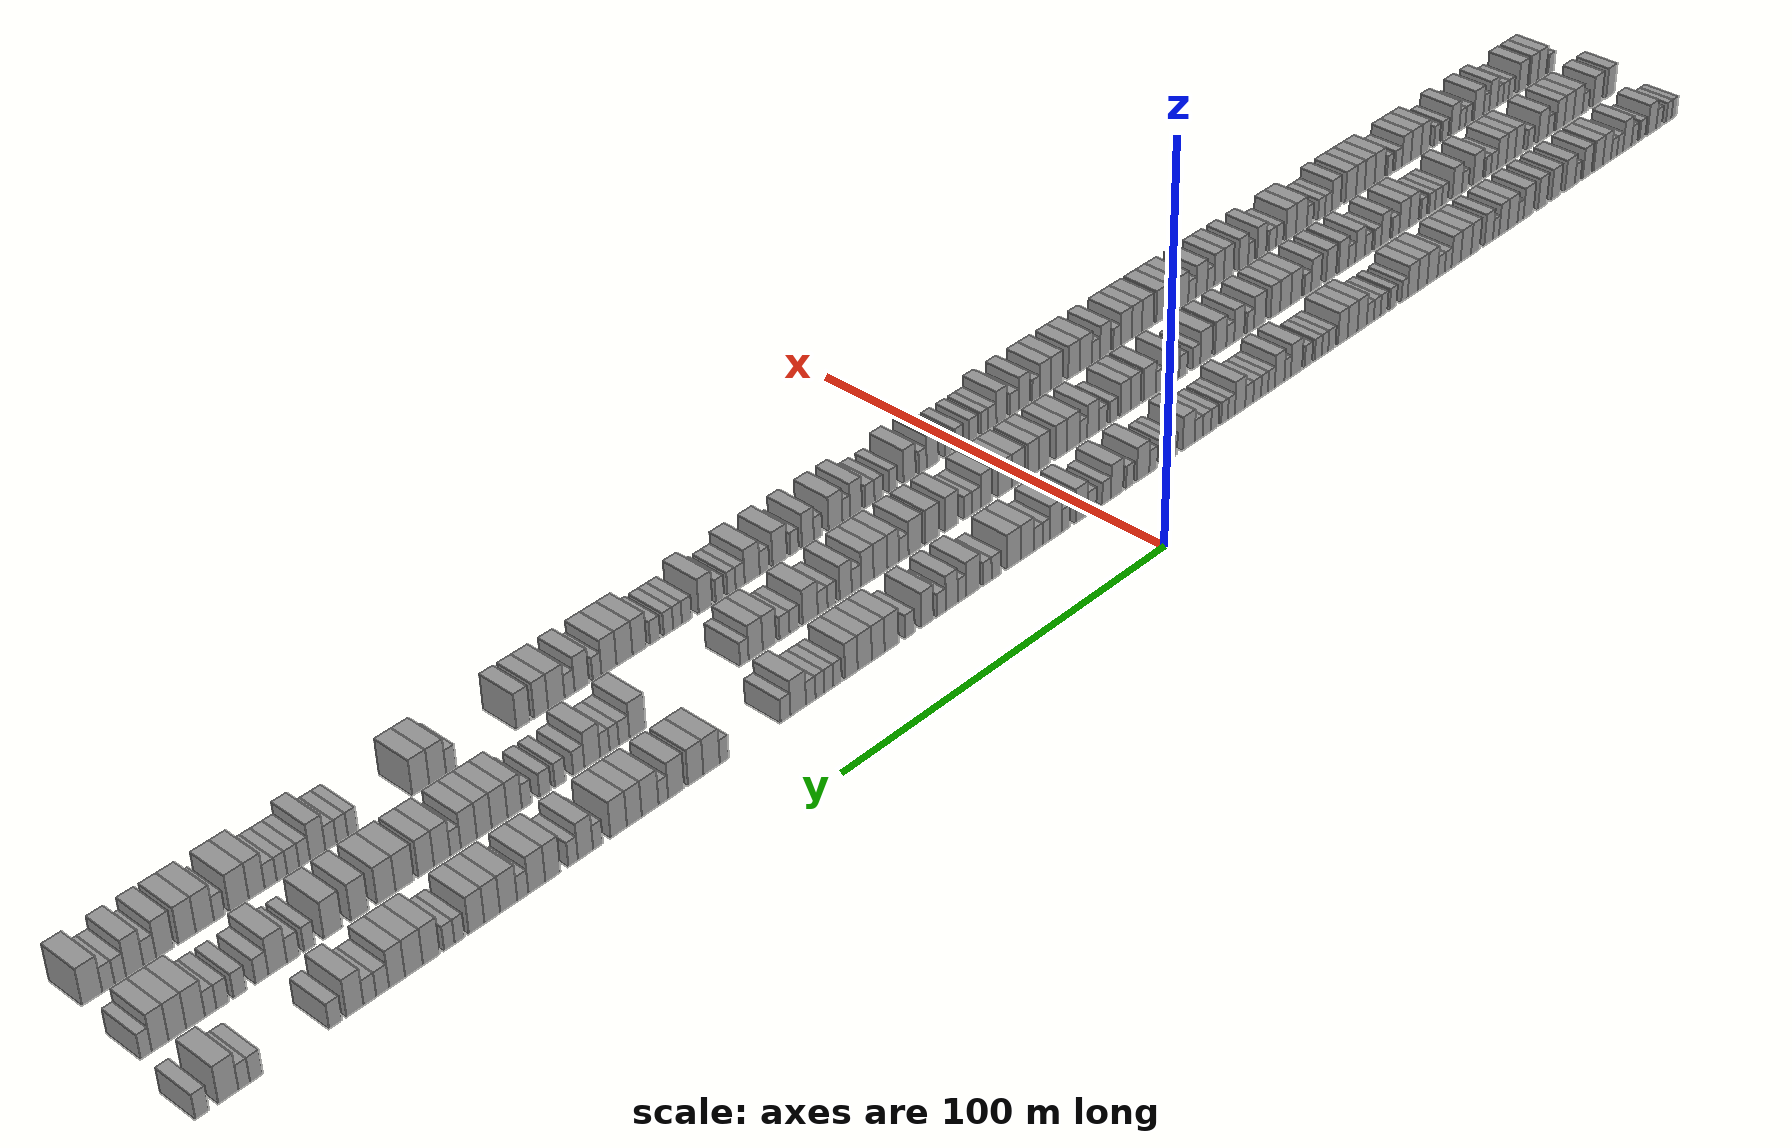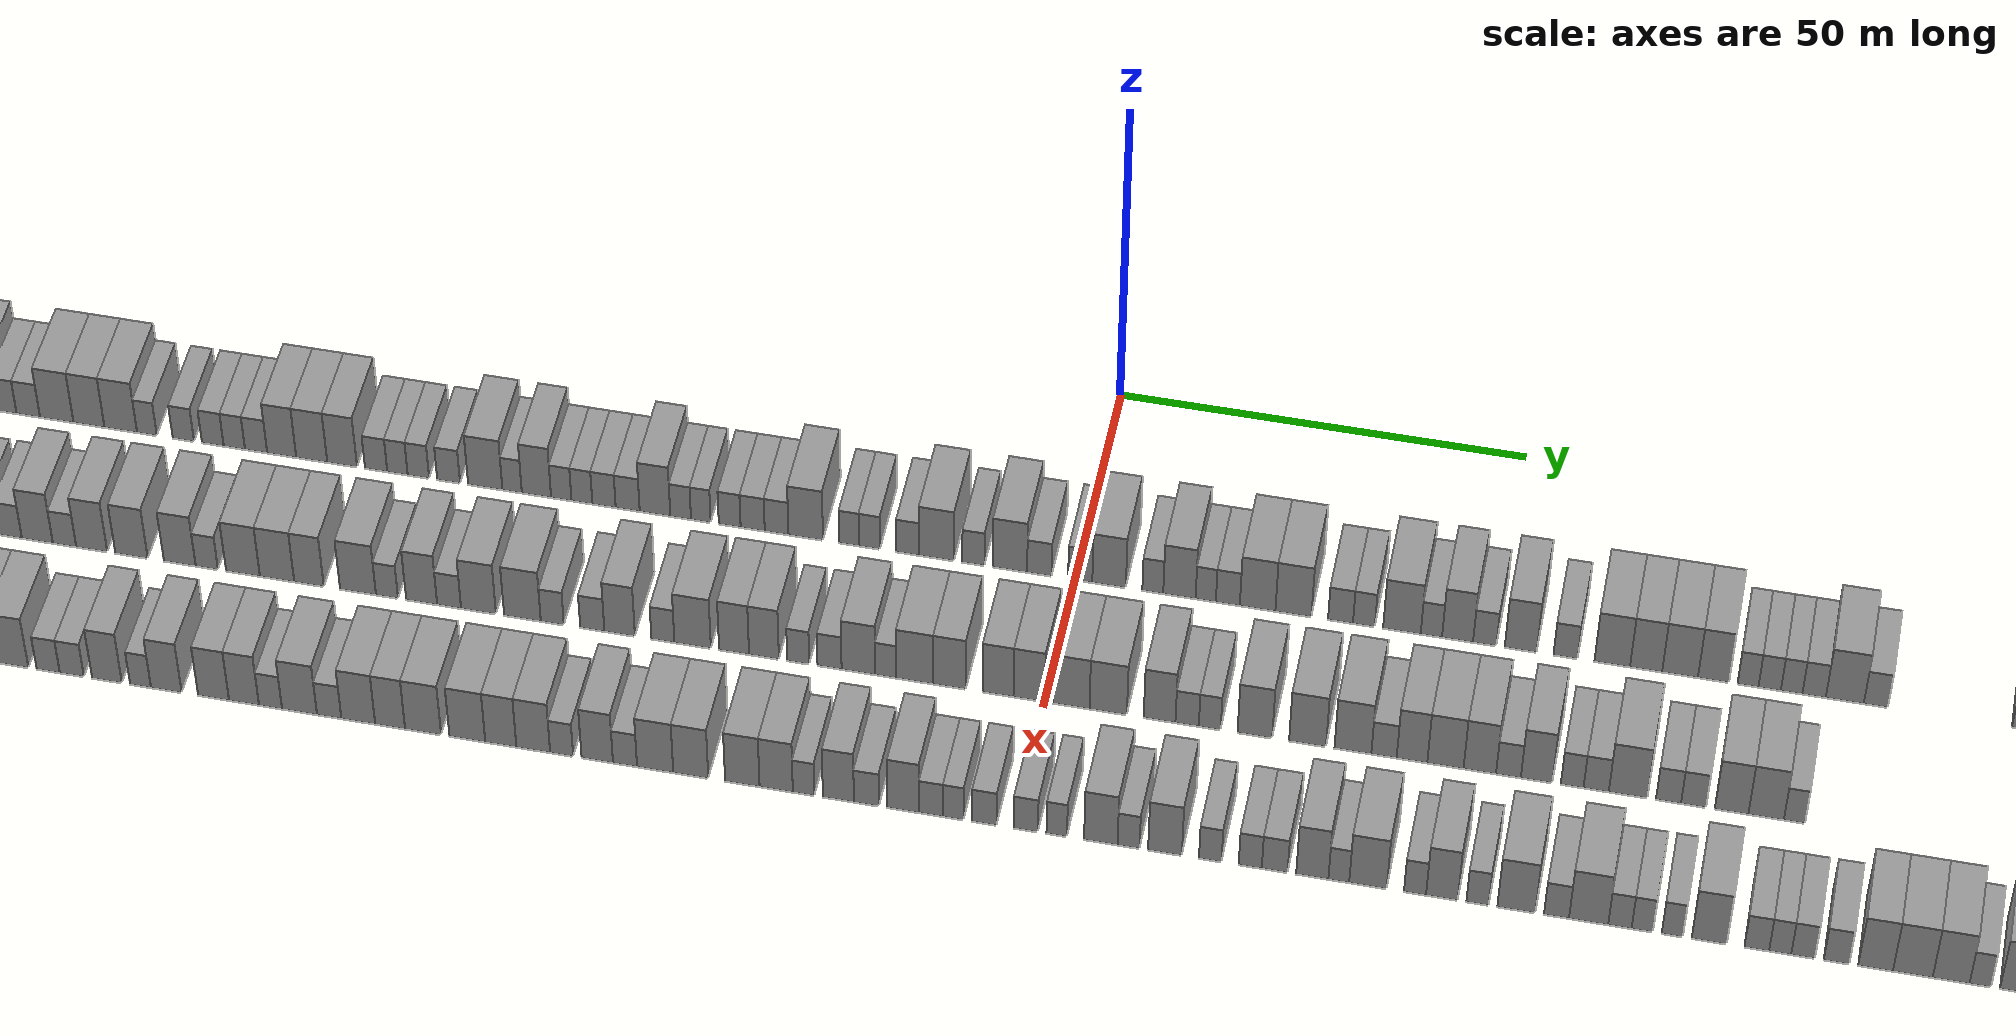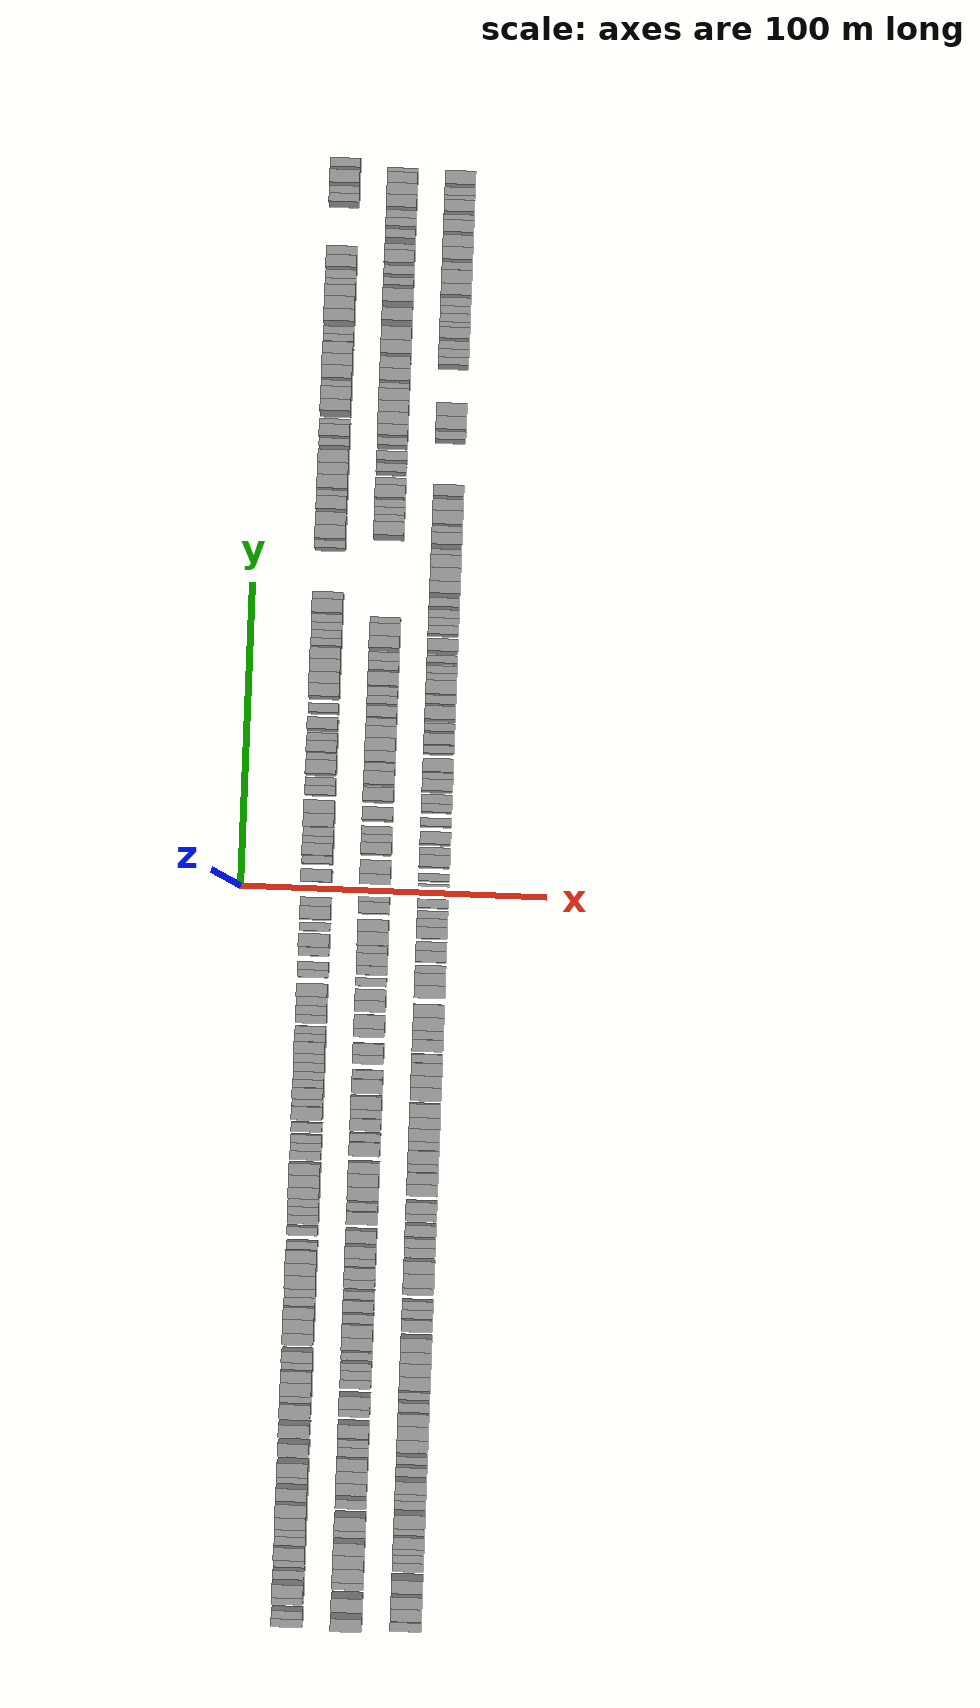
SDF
<sdf version="1.6">
 <world name="default">
  <scene>
   <sky><clouds><speed>12</speed></clouds></sky>
   <ambient>0.4 0.4 0.4 1</ambient>
   <background>0.7 0.7 0.7 1</background>
   <shadows>1</shadows>
  </scene>
  <gravity>0 0 -9.8066</gravity>
  <magnetic_field>6e-06 2.3e-05 -4.2e-05</magnetic_field>
  <physics default="0" name="default_physics" type="ode">
   <ode>
    <solver>
     <type>quick</type>
     <iters>10</iters>
     <sor>1.0</sor>
     <use_dynamic_moi_rescaling>0</use_dynamic_moi_rescaling>
    </solver>
    <constraints>
     <cfm>0</cfm>
     <erp>0.2</erp>
     <contact_max_correcting_vel>100</contact_max_correcting_vel>
     <contact_surface_layer>0.001</contact_surface_layer>
    </constraints>
   </ode>
   <max_step_size>0.004</max_step_size>
   <real_time_factor>1</real_time_factor>
   <real_time_update_rate>250</real_time_update_rate>
  </physics>
  <light name="sun" type="directional">
   <pose>0 0 10 0 0 0</pose>
   <diffuse>0.8 0.8 0.8 1</diffuse>
   <specular>0.2 0.2 0.2 1</specular>
   <attenuation>
    <range>1000</range>
    <constant>0.9</constant>
    <linear>0.01</linear>
    <quadratic>0.001</quadratic>
   </attenuation>
   <direction>-0.5 0.1 -0.9</direction>
  </light>
  <model name="building_1">
   <static>1</static>
   <pose>25.0000 -234.7384 0 0.000000 0.000000 0.000000</pose>
   <link name="link">
    <pose>0 0 3.00 0 0 0</pose>
    <collision name="collision"><geometry><box><size>10.0000 2.5231 6.0000</size></box></geometry></collision>
    <visual name="visual">
     <cast_shadows>0</cast_shadows>
     <geometry><box><size>10.0000 2.5231 6.0000</size></box></geometry>
     <material>
      <script>
       <uri>model://grey_wall/materials/scripts</uri>
       <uri>model://grey_wall/materials/textures</uri>
       <name>vrc/grey_wall</name>
      </script>
     </material>
    </visual>
   </link>
  </model>
  <model name="building_2">
   <static>1</static>
   <pose>25.0000 -232.1970 0 0.000000 0.000000 0.000000</pose>
   <link name="link">
    <pose>0 0 3.00 0 0 0</pose>
    <collision name="collision"><geometry><box><size>10.0000 2.5597 6.0000</size></box></geometry></collision>
    <visual name="visual">
     <cast_shadows>0</cast_shadows>
     <geometry><box><size>10.0000 2.5597 6.0000</size></box></geometry>
     <material>
      <script>
       <uri>model://grey_wall/materials/scripts</uri>
       <uri>model://grey_wall/materials/textures</uri>
       <name>vrc/grey_wall</name>
      </script>
     </material>
    </visual>
   </link>
  </model>
  <model name="building_3">
   <static>1</static>
   <pose>25.0000 -227.5355 0 0.000000 0.000000 0.000000</pose>
   <link name="link">
    <pose>0 0 3.00 0 0 0</pose>
    <collision name="collision"><geometry><box><size>10.0000 2.7634 6.0000</size></box></geometry></collision>
    <visual name="visual">
     <cast_shadows>0</cast_shadows>
     <geometry><box><size>10.0000 2.7634 6.0000</size></box></geometry>
     <material>
      <script>
       <uri>model://grey_wall/materials/scripts</uri>
       <uri>model://grey_wall/materials/textures</uri>
       <name>vrc/grey_wall</name>
      </script>
     </material>
    </visual>
   </link>
  </model>
  <model name="building_4">
   <static>1</static>
   <pose>25.0000 -224.0733 0 0.000000 0.000000 0.000000</pose>
   <link name="link">
    <pose>0 0 4.50 0 0 0</pose>
    <collision name="collision"><geometry><box><size>10.0000 4.1609 9.0000</size></box></geometry></collision>
    <visual name="visual">
     <cast_shadows>0</cast_shadows>
     <geometry><box><size>10.0000 4.1609 9.0000</size></box></geometry>
     <material>
      <script>
       <uri>model://grey_wall/materials/scripts</uri>
       <uri>model://grey_wall/materials/textures</uri>
       <name>vrc/grey_wall</name>
      </script>
     </material>
    </visual>
   </link>
  </model>
  <model name="building_5">
   <static>1</static>
   <pose>25.0000 -219.5914 0 0.000000 0.000000 0.000000</pose>
   <link name="link">
    <pose>0 0 3.00 0 0 0</pose>
    <collision name="collision"><geometry><box><size>10.0000 2.8029 6.0000</size></box></geometry></collision>
    <visual name="visual">
     <cast_shadows>0</cast_shadows>
     <geometry><box><size>10.0000 2.8029 6.0000</size></box></geometry>
     <material>
      <script>
       <uri>model://grey_wall/materials/scripts</uri>
       <uri>model://grey_wall/materials/textures</uri>
       <name>vrc/grey_wall</name>
      </script>
     </material>
    </visual>
   </link>
  </model>
  <model name="building_6">
   <static>1</static>
   <pose>25.0000 -215.7897 0 0.000000 0.000000 0.000000</pose>
   <link name="link">
    <pose>0 0 3.00 0 0 0</pose>
    <collision name="collision"><geometry><box><size>10.0000 2.8006 6.0000</size></box></geometry></collision>
    <visual name="visual">
     <cast_shadows>0</cast_shadows>
     <geometry><box><size>10.0000 2.8006 6.0000</size></box></geometry>
     <material>
      <script>
       <uri>model://grey_wall/materials/scripts</uri>
       <uri>model://grey_wall/materials/textures</uri>
       <name>vrc/grey_wall</name>
      </script>
     </material>
    </visual>
   </link>
  </model>
  <model name="building_7">
   <static>1</static>
   <pose>25.0000 -212.3828 0 0.000000 0.000000 0.000000</pose>
   <link name="link">
    <pose>0 0 4.50 0 0 0</pose>
    <collision name="collision"><geometry><box><size>10.0000 4.0132 9.0000</size></box></geometry></collision>
    <visual name="visual">
     <cast_shadows>0</cast_shadows>
     <geometry><box><size>10.0000 4.0132 9.0000</size></box></geometry>
     <material>
      <script>
       <uri>model://grey_wall/materials/scripts</uri>
       <uri>model://grey_wall/materials/textures</uri>
       <name>vrc/grey_wall</name>
      </script>
     </material>
    </visual>
   </link>
  </model>
  <model name="building_8">
   <static>1</static>
   <pose>25.0000 -208.9875 0 0.000000 0.000000 0.000000</pose>
   <link name="link">
    <pose>0 0 3.00 0 0 0</pose>
    <collision name="collision"><geometry><box><size>10.0000 2.7774 6.0000</size></box></geometry></collision>
    <visual name="visual">
     <cast_shadows>0</cast_shadows>
     <geometry><box><size>10.0000 2.7774 6.0000</size></box></geometry>
     <material>
      <script>
       <uri>model://grey_wall/materials/scripts</uri>
       <uri>model://grey_wall/materials/textures</uri>
       <name>vrc/grey_wall</name>
      </script>
     </material>
    </visual>
   </link>
  </model>
  <model name="building_9">
   <static>1</static>
   <pose>25.0000 -206.1806 0 0.000000 0.000000 0.000000</pose>
   <link name="link">
    <pose>0 0 3.00 0 0 0</pose>
    <collision name="collision"><geometry><box><size>10.0000 2.8366 6.0000</size></box></geometry></collision>
    <visual name="visual">
     <cast_shadows>0</cast_shadows>
     <geometry><box><size>10.0000 2.8366 6.0000</size></box></geometry>
     <material>
      <script>
       <uri>model://grey_wall/materials/scripts</uri>
       <uri>model://grey_wall/materials/textures</uri>
       <name>vrc/grey_wall</name>
      </script>
     </material>
    </visual>
   </link>
  </model>
  <model name="building_10">
   <static>1</static>
   <pose>25.0000 -202.8915 0 0.000000 0.000000 0.000000</pose>
   <link name="link">
    <pose>0 0 4.50 0 0 0</pose>
    <collision name="collision"><geometry><box><size>10.0000 3.7415 9.0000</size></box></geometry></collision>
    <visual name="visual">
     <cast_shadows>0</cast_shadows>
     <geometry><box><size>10.0000 3.7415 9.0000</size></box></geometry>
     <material>
      <script>
       <uri>model://grey_wall/materials/scripts</uri>
       <uri>model://grey_wall/materials/textures</uri>
       <name>vrc/grey_wall</name>
      </script>
     </material>
    </visual>
   </link>
  </model>
  <model name="building_11">
   <static>1</static>
   <pose>25.0000 -198.9121 0 0.000000 0.000000 0.000000</pose>
   <link name="link">
    <pose>0 0 4.50 0 0 0</pose>
    <collision name="collision"><geometry><box><size>10.0000 4.2174 9.0000</size></box></geometry></collision>
    <visual name="visual">
     <cast_shadows>0</cast_shadows>
     <geometry><box><size>10.0000 4.2174 9.0000</size></box></geometry>
     <material>
      <script>
       <uri>model://grey_wall/materials/scripts</uri>
       <uri>model://grey_wall/materials/textures</uri>
       <name>vrc/grey_wall</name>
      </script>
     </material>
    </visual>
   </link>
  </model>
  <model name="building_12">
   <static>1</static>
   <pose>25.0000 -193.8007 0 0.000000 0.000000 0.000000</pose>
   <link name="link">
    <pose>0 0 4.50 0 0 0</pose>
    <collision name="collision"><geometry><box><size>10.0000 4.0055 9.0000</size></box></geometry></collision>
    <visual name="visual">
     <cast_shadows>0</cast_shadows>
     <geometry><box><size>10.0000 4.0055 9.0000</size></box></geometry>
     <material>
      <script>
       <uri>model://grey_wall/materials/scripts</uri>
       <uri>model://grey_wall/materials/textures</uri>
       <name>vrc/grey_wall</name>
      </script>
     </material>
    </visual>
   </link>
  </model>
  <model name="building_13">
   <static>1</static>
   <pose>25.0000 -189.5023 0 0.000000 0.000000 0.000000</pose>
   <link name="link">
    <pose>0 0 3.00 0 0 0</pose>
    <collision name="collision"><geometry><box><size>10.0000 2.5913 6.0000</size></box></geometry></collision>
    <visual name="visual">
     <cast_shadows>0</cast_shadows>
     <geometry><box><size>10.0000 2.5913 6.0000</size></box></geometry>
     <material>
      <script>
       <uri>model://grey_wall/materials/scripts</uri>
       <uri>model://grey_wall/materials/textures</uri>
       <name>vrc/grey_wall</name>
      </script>
     </material>
    </visual>
   </link>
  </model>
  <model name="building_14">
   <static>1</static>
   <pose>25.0000 -185.9713 0 0.000000 0.000000 0.000000</pose>
   <link name="link">
    <pose>0 0 4.50 0 0 0</pose>
    <collision name="collision"><geometry><box><size>10.0000 4.4707 9.0000</size></box></geometry></collision>
    <visual name="visual">
     <cast_shadows>0</cast_shadows>
     <geometry><box><size>10.0000 4.4707 9.0000</size></box></geometry>
     <material>
      <script>
       <uri>model://grey_wall/materials/scripts</uri>
       <uri>model://grey_wall/materials/textures</uri>
       <name>vrc/grey_wall</name>
      </script>
     </material>
    </visual>
   </link>
  </model>
  <model name="building_15">
   <static>1</static>
   <pose>25.0000 -179.6854 0 0.000000 0.000000 0.000000</pose>
   <link name="link">
    <pose>0 0 4.50 0 0 0</pose>
    <collision name="collision"><geometry><box><size>10.0000 4.1010 9.0000</size></box></geometry></collision>
    <visual name="visual">
     <cast_shadows>0</cast_shadows>
     <geometry><box><size>10.0000 4.1010 9.0000</size></box></geometry>
     <material>
      <script>
       <uri>model://grey_wall/materials/scripts</uri>
       <uri>model://grey_wall/materials/textures</uri>
       <name>vrc/grey_wall</name>
      </script>
     </material>
    </visual>
   </link>
  </model>
  <model name="building_16">
   <static>1</static>
   <pose>25.0000 -173.6761 0 0.000000 0.000000 0.000000</pose>
   <link name="link">
    <pose>0 0 4.50 0 0 0</pose>
    <collision name="collision"><geometry><box><size>10.0000 3.9175 9.0000</size></box></geometry></collision>
    <visual name="visual">
     <cast_shadows>0</cast_shadows>
     <geometry><box><size>10.0000 3.9175 9.0000</size></box></geometry>
     <material>
      <script>
       <uri>model://grey_wall/materials/scripts</uri>
       <uri>model://grey_wall/materials/textures</uri>
       <name>vrc/grey_wall</name>
      </script>
     </material>
    </visual>
   </link>
  </model>
  <model name="building_17">
   <static>1</static>
   <pose>25.0000 -167.4812 0 0.000000 0.000000 0.000000</pose>
   <link name="link">
    <pose>0 0 4.50 0 0 0</pose>
    <collision name="collision"><geometry><box><size>10.0000 4.4723 9.0000</size></box></geometry></collision>
    <visual name="visual">
     <cast_shadows>0</cast_shadows>
     <geometry><box><size>10.0000 4.4723 9.0000</size></box></geometry>
     <material>
      <script>
       <uri>model://grey_wall/materials/scripts</uri>
       <uri>model://grey_wall/materials/textures</uri>
       <name>vrc/grey_wall</name>
      </script>
     </material>
    </visual>
   </link>
  </model>
  <model name="building_18">
   <static>1</static>
   <pose>25.0000 -163.9544 0 0.000000 0.000000 0.000000</pose>
   <link name="link">
    <pose>0 0 3.00 0 0 0</pose>
    <collision name="collision"><geometry><box><size>10.0000 2.5814 6.0000</size></box></geometry></collision>
    <visual name="visual">
     <cast_shadows>0</cast_shadows>
     <geometry><box><size>10.0000 2.5814 6.0000</size></box></geometry>
     <material>
      <script>
       <uri>model://grey_wall/materials/scripts</uri>
       <uri>model://grey_wall/materials/textures</uri>
       <name>vrc/grey_wall</name>
      </script>
     </material>
    </visual>
   </link>
  </model>
  <model name="building_19">
   <static>1</static>
   <pose>25.0000 -160.5230 0 0.000000 0.000000 0.000000</pose>
   <link name="link">
    <pose>0 0 4.50 0 0 0</pose>
    <collision name="collision"><geometry><box><size>10.0000 4.2813 9.0000</size></box></geometry></collision>
    <visual name="visual">
     <cast_shadows>0</cast_shadows>
     <geometry><box><size>10.0000 4.2813 9.0000</size></box></geometry>
     <material>
      <script>
       <uri>model://grey_wall/materials/scripts</uri>
       <uri>model://grey_wall/materials/textures</uri>
       <name>vrc/grey_wall</name>
      </script>
     </material>
    </visual>
   </link>
  </model>
  <model name="building_20">
   <static>1</static>
   <pose>25.0000 -156.5342 0 0.000000 0.000000 0.000000</pose>
   <link name="link">
    <pose>0 0 4.50 0 0 0</pose>
    <collision name="collision"><geometry><box><size>10.0000 3.6963 9.0000</size></box></geometry></collision>
    <visual name="visual">
     <cast_shadows>0</cast_shadows>
     <geometry><box><size>10.0000 3.6963 9.0000</size></box></geometry>
     <material>
      <script>
       <uri>model://grey_wall/materials/scripts</uri>
       <uri>model://grey_wall/materials/textures</uri>
       <name>vrc/grey_wall</name>
      </script>
     </material>
    </visual>
   </link>
  </model>
  <model name="building_21">
   <static>1</static>
   <pose>25.0000 -153.3508 0 0.000000 0.000000 0.000000</pose>
   <link name="link">
    <pose>0 0 3.00 0 0 0</pose>
    <collision name="collision"><geometry><box><size>10.0000 2.6704 6.0000</size></box></geometry></collision>
    <visual name="visual">
     <cast_shadows>0</cast_shadows>
     <geometry><box><size>10.0000 2.6704 6.0000</size></box></geometry>
     <material>
      <script>
       <uri>model://grey_wall/materials/scripts</uri>
       <uri>model://grey_wall/materials/textures</uri>
       <name>vrc/grey_wall</name>
      </script>
     </material>
    </visual>
   </link>
  </model>
  <model name="building_22">
   <static>1</static>
   <pose>25.0000 -150.2124 0 0.000000 0.000000 0.000000</pose>
   <link name="link">
    <pose>0 0 4.50 0 0 0</pose>
    <collision name="collision"><geometry><box><size>10.0000 3.6064 9.0000</size></box></geometry></collision>
    <visual name="visual">
     <cast_shadows>0</cast_shadows>
     <geometry><box><size>10.0000 3.6064 9.0000</size></box></geometry>
     <material>
      <script>
       <uri>model://grey_wall/materials/scripts</uri>
       <uri>model://grey_wall/materials/textures</uri>
       <name>vrc/grey_wall</name>
      </script>
     </material>
    </visual>
   </link>
  </model>
  <model name="building_23">
   <static>1</static>
   <pose>25.0000 -144.5589 0 0.000000 0.000000 0.000000</pose>
   <link name="link">
    <pose>0 0 4.50 0 0 0</pose>
    <collision name="collision"><geometry><box><size>10.0000 3.7007 9.0000</size></box></geometry></collision>
    <visual name="visual">
     <cast_shadows>0</cast_shadows>
     <geometry><box><size>10.0000 3.7007 9.0000</size></box></geometry>
     <material>
      <script>
       <uri>model://grey_wall/materials/scripts</uri>
       <uri>model://grey_wall/materials/textures</uri>
       <name>vrc/grey_wall</name>
      </script>
     </material>
    </visual>
   </link>
  </model>
  <model name="building_24">
   <static>1</static>
   <pose>25.0000 -140.4997 0 0.000000 0.000000 0.000000</pose>
   <link name="link">
    <pose>0 0 4.50 0 0 0</pose>
    <collision name="collision"><geometry><box><size>10.0000 4.4178 9.0000</size></box></geometry></collision>
    <visual name="visual">
     <cast_shadows>0</cast_shadows>
     <geometry><box><size>10.0000 4.4178 9.0000</size></box></geometry>
     <material>
      <script>
       <uri>model://grey_wall/materials/scripts</uri>
       <uri>model://grey_wall/materials/textures</uri>
       <name>vrc/grey_wall</name>
      </script>
     </material>
    </visual>
   </link>
  </model>
  <model name="building_25">
   <static>1</static>
   <pose>25.0000 -136.3482 0 0.000000 0.000000 0.000000</pose>
   <link name="link">
    <pose>0 0 4.50 0 0 0</pose>
    <collision name="collision"><geometry><box><size>10.0000 3.8852 9.0000</size></box></geometry></collision>
    <visual name="visual">
     <cast_shadows>0</cast_shadows>
     <geometry><box><size>10.0000 3.8852 9.0000</size></box></geometry>
     <material>
      <script>
       <uri>model://grey_wall/materials/scripts</uri>
       <uri>model://grey_wall/materials/textures</uri>
       <name>vrc/grey_wall</name>
      </script>
     </material>
    </visual>
   </link>
  </model>
  <model name="building_26">
   <static>1</static>
   <pose>25.0000 -132.9980 0 0.000000 0.000000 0.000000</pose>
   <link name="link">
    <pose>0 0 3.00 0 0 0</pose>
    <collision name="collision"><geometry><box><size>10.0000 2.8153 6.0000</size></box></geometry></collision>
    <visual name="visual">
     <cast_shadows>0</cast_shadows>
     <geometry><box><size>10.0000 2.8153 6.0000</size></box></geometry>
     <material>
      <script>
       <uri>model://grey_wall/materials/scripts</uri>
       <uri>model://grey_wall/materials/textures</uri>
       <name>vrc/grey_wall</name>
      </script>
     </material>
    </visual>
   </link>
  </model>
  <model name="building_27">
   <static>1</static>
   <pose>25.0000 -130.0991 0 0.000000 0.000000 0.000000</pose>
   <link name="link">
    <pose>0 0 3.00 0 0 0</pose>
    <collision name="collision"><geometry><box><size>10.0000 2.9823 6.0000</size></box></geometry></collision>
    <visual name="visual">
     <cast_shadows>0</cast_shadows>
     <geometry><box><size>10.0000 2.9823 6.0000</size></box></geometry>
     <material>
      <script>
       <uri>model://grey_wall/materials/scripts</uri>
       <uri>model://grey_wall/materials/textures</uri>
       <name>vrc/grey_wall</name>
      </script>
     </material>
    </visual>
   </link>
  </model>
  <model name="building_28">
   <static>1</static>
   <pose>25.0000 -126.4854 0 0.000000 0.000000 0.000000</pose>
   <link name="link">
    <pose>0 0 4.50 0 0 0</pose>
    <collision name="collision"><geometry><box><size>10.0000 4.2451 9.0000</size></box></geometry></collision>
    <visual name="visual">
     <cast_shadows>0</cast_shadows>
     <geometry><box><size>10.0000 4.2451 9.0000</size></box></geometry>
     <material>
      <script>
       <uri>model://grey_wall/materials/scripts</uri>
       <uri>model://grey_wall/materials/textures</uri>
       <name>vrc/grey_wall</name>
      </script>
     </material>
    </visual>
   </link>
  </model>
  <model name="building_29">
   <static>1</static>
   <pose>25.0000 -122.3952 0 0.000000 0.000000 0.000000</pose>
   <link name="link">
    <pose>0 0 4.50 0 0 0</pose>
    <collision name="collision"><geometry><box><size>10.0000 3.9354 9.0000</size></box></geometry></collision>
    <visual name="visual">
     <cast_shadows>0</cast_shadows>
     <geometry><box><size>10.0000 3.9354 9.0000</size></box></geometry>
     <material>
      <script>
       <uri>model://grey_wall/materials/scripts</uri>
       <uri>model://grey_wall/materials/textures</uri>
       <name>vrc/grey_wall</name>
      </script>
     </material>
    </visual>
   </link>
  </model>
  <model name="building_30">
   <static>1</static>
   <pose>25.0000 -118.3647 0 0.000000 0.000000 0.000000</pose>
   <link name="link">
    <pose>0 0 4.50 0 0 0</pose>
    <collision name="collision"><geometry><box><size>10.0000 4.1256 9.0000</size></box></geometry></collision>
    <visual name="visual">
     <cast_shadows>0</cast_shadows>
     <geometry><box><size>10.0000 4.1256 9.0000</size></box></geometry>
     <material>
      <script>
       <uri>model://grey_wall/materials/scripts</uri>
       <uri>model://grey_wall/materials/textures</uri>
       <name>vrc/grey_wall</name>
      </script>
     </material>
    </visual>
   </link>
  </model>
  <model name="building_31">
   <static>1</static>
   <pose>25.0000 -115.0467 0 0.000000 0.000000 0.000000</pose>
   <link name="link">
    <pose>0 0 3.00 0 0 0</pose>
    <collision name="collision"><geometry><box><size>10.0000 2.5103 6.0000</size></box></geometry></collision>
    <visual name="visual">
     <cast_shadows>0</cast_shadows>
     <geometry><box><size>10.0000 2.5103 6.0000</size></box></geometry>
     <material>
      <script>
       <uri>model://grey_wall/materials/scripts</uri>
       <uri>model://grey_wall/materials/textures</uri>
       <name>vrc/grey_wall</name>
      </script>
     </material>
    </visual>
   </link>
  </model>
  <model name="building_32">
   <static>1</static>
   <pose>25.0000 -110.4434 0 0.000000 0.000000 0.000000</pose>
   <link name="link">
    <pose>0 0 3.00 0 0 0</pose>
    <collision name="collision"><geometry><box><size>10.0000 2.6963 6.0000</size></box></geometry></collision>
    <visual name="visual">
     <cast_shadows>0</cast_shadows>
     <geometry><box><size>10.0000 2.6963 6.0000</size></box></geometry>
     <material>
      <script>
       <uri>model://grey_wall/materials/scripts</uri>
       <uri>model://grey_wall/materials/textures</uri>
       <name>vrc/grey_wall</name>
      </script>
     </material>
    </visual>
   </link>
  </model>
  <model name="building_33">
   <static>1</static>
   <pose>25.0000 -106.7267 0 0.000000 0.000000 0.000000</pose>
   <link name="link">
    <pose>0 0 3.00 0 0 0</pose>
    <collision name="collision"><geometry><box><size>10.0000 2.7371 6.0000</size></box></geometry></collision>
    <visual name="visual">
     <cast_shadows>0</cast_shadows>
     <geometry><box><size>10.0000 2.7371 6.0000</size></box></geometry>
     <material>
      <script>
       <uri>model://grey_wall/materials/scripts</uri>
       <uri>model://grey_wall/materials/textures</uri>
       <name>vrc/grey_wall</name>
      </script>
     </material>
    </visual>
   </link>
  </model>
  <model name="building_34">
   <static>1</static>
   <pose>25.0000 -104.0174 0 0.000000 0.000000 0.000000</pose>
   <link name="link">
    <pose>0 0 3.00 0 0 0</pose>
    <collision name="collision"><geometry><box><size>10.0000 2.6816 6.0000</size></box></geometry></collision>
    <visual name="visual">
     <cast_shadows>0</cast_shadows>
     <geometry><box><size>10.0000 2.6816 6.0000</size></box></geometry>
     <material>
      <script>
       <uri>model://grey_wall/materials/scripts</uri>
       <uri>model://grey_wall/materials/textures</uri>
       <name>vrc/grey_wall</name>
      </script>
     </material>
    </visual>
   </link>
  </model>
  <model name="building_35">
   <static>1</static>
   <pose>25.0000 -101.2738 0 0.000000 0.000000 0.000000</pose>
   <link name="link">
    <pose>0 0 3.00 0 0 0</pose>
    <collision name="collision"><geometry><box><size>10.0000 2.8056 6.0000</size></box></geometry></collision>
    <visual name="visual">
     <cast_shadows>0</cast_shadows>
     <geometry><box><size>10.0000 2.8056 6.0000</size></box></geometry>
     <material>
      <script>
       <uri>model://grey_wall/materials/scripts</uri>
       <uri>model://grey_wall/materials/textures</uri>
       <name>vrc/grey_wall</name>
      </script>
     </material>
    </visual>
   </link>
  </model>
  <model name="building_36">
   <static>1</static>
   <pose>25.0000 -98.0478 0 0.000000 0.000000 0.000000</pose>
   <link name="link">
    <pose>0 0 4.50 0 0 0</pose>
    <collision name="collision"><geometry><box><size>10.0000 3.6464 9.0000</size></box></geometry></collision>
    <visual name="visual">
     <cast_shadows>0</cast_shadows>
     <geometry><box><size>10.0000 3.6464 9.0000</size></box></geometry>
     <material>
      <script>
       <uri>model://grey_wall/materials/scripts</uri>
       <uri>model://grey_wall/materials/textures</uri>
       <name>vrc/grey_wall</name>
      </script>
     </material>
    </visual>
   </link>
  </model>
  <model name="building_37">
   <static>1</static>
   <pose>25.0000 -94.2791 0 0.000000 0.000000 0.000000</pose>
   <link name="link">
    <pose>0 0 4.50 0 0 0</pose>
    <collision name="collision"><geometry><box><size>10.0000 3.8909 9.0000</size></box></geometry></collision>
    <visual name="visual">
     <cast_shadows>0</cast_shadows>
     <geometry><box><size>10.0000 3.8909 9.0000</size></box></geometry>
     <material>
      <script>
       <uri>model://grey_wall/materials/scripts</uri>
       <uri>model://grey_wall/materials/textures</uri>
       <name>vrc/grey_wall</name>
      </script>
     </material>
    </visual>
   </link>
  </model>
  <model name="building_38">
   <static>1</static>
   <pose>25.0000 -90.4630 0 0.000000 0.000000 0.000000</pose>
   <link name="link">
    <pose>0 0 4.50 0 0 0</pose>
    <collision name="collision"><geometry><box><size>10.0000 3.7415 9.0000</size></box></geometry></collision>
    <visual name="visual">
     <cast_shadows>0</cast_shadows>
     <geometry><box><size>10.0000 3.7415 9.0000</size></box></geometry>
     <material>
      <script>
       <uri>model://grey_wall/materials/scripts</uri>
       <uri>model://grey_wall/materials/textures</uri>
       <name>vrc/grey_wall</name>
      </script>
     </material>
    </visual>
   </link>
  </model>
  <model name="building_39">
   <static>1</static>
   <pose>25.0000 -86.2016 0 0.000000 0.000000 0.000000</pose>
   <link name="link">
    <pose>0 0 3.00 0 0 0</pose>
    <collision name="collision"><geometry><box><size>10.0000 2.7812 6.0000</size></box></geometry></collision>
    <visual name="visual">
     <cast_shadows>0</cast_shadows>
     <geometry><box><size>10.0000 2.7812 6.0000</size></box></geometry>
     <material>
      <script>
       <uri>model://grey_wall/materials/scripts</uri>
       <uri>model://grey_wall/materials/textures</uri>
       <name>vrc/grey_wall</name>
      </script>
     </material>
    </visual>
   </link>
  </model>
  <model name="building_40">
   <static>1</static>
   <pose>25.0000 -83.5370 0 0.000000 0.000000 0.000000</pose>
   <link name="link">
    <pose>0 0 3.00 0 0 0</pose>
    <collision name="collision"><geometry><box><size>10.0000 2.5480 6.0000</size></box></geometry></collision>
    <visual name="visual">
     <cast_shadows>0</cast_shadows>
     <geometry><box><size>10.0000 2.5480 6.0000</size></box></geometry>
     <material>
      <script>
       <uri>model://grey_wall/materials/scripts</uri>
       <uri>model://grey_wall/materials/textures</uri>
       <name>vrc/grey_wall</name>
      </script>
     </material>
    </visual>
   </link>
  </model>
  <model name="building_41">
   <static>1</static>
   <pose>25.0000 -80.9181 0 0.000000 0.000000 0.000000</pose>
   <link name="link">
    <pose>0 0 3.00 0 0 0</pose>
    <collision name="collision"><geometry><box><size>10.0000 2.6897 6.0000</size></box></geometry></collision>
    <visual name="visual">
     <cast_shadows>0</cast_shadows>
     <geometry><box><size>10.0000 2.6897 6.0000</size></box></geometry>
     <material>
      <script>
       <uri>model://grey_wall/materials/scripts</uri>
       <uri>model://grey_wall/materials/textures</uri>
       <name>vrc/grey_wall</name>
      </script>
     </material>
    </visual>
   </link>
  </model>
  <model name="building_42">
   <static>1</static>
   <pose>25.0000 -77.1449 0 0.000000 0.000000 0.000000</pose>
   <link name="link">
    <pose>0 0 3.00 0 0 0</pose>
    <collision name="collision"><geometry><box><size>10.0000 2.8566 6.0000</size></box></geometry></collision>
    <visual name="visual">
     <cast_shadows>0</cast_shadows>
     <geometry><box><size>10.0000 2.8566 6.0000</size></box></geometry>
     <material>
      <script>
       <uri>model://grey_wall/materials/scripts</uri>
       <uri>model://grey_wall/materials/textures</uri>
       <name>vrc/grey_wall</name>
      </script>
     </material>
    </visual>
   </link>
  </model>
  <model name="building_43">
   <static>1</static>
   <pose>25.0000 -72.5755 0 0.000000 0.000000 0.000000</pose>
   <link name="link">
    <pose>0 0 4.50 0 0 0</pose>
    <collision name="collision"><geometry><box><size>10.0000 4.2822 9.0000</size></box></geometry></collision>
    <visual name="visual">
     <cast_shadows>0</cast_shadows>
     <geometry><box><size>10.0000 4.2822 9.0000</size></box></geometry>
     <material>
      <script>
       <uri>model://grey_wall/materials/scripts</uri>
       <uri>model://grey_wall/materials/textures</uri>
       <name>vrc/grey_wall</name>
      </script>
     </material>
    </visual>
   </link>
  </model>
  <model name="building_44">
   <static>1</static>
   <pose>25.0000 -69.2297 0 0.000000 0.000000 0.000000</pose>
   <link name="link">
    <pose>0 0 3.00 0 0 0</pose>
    <collision name="collision"><geometry><box><size>10.0000 2.4093 6.0000</size></box></geometry></collision>
    <visual name="visual">
     <cast_shadows>0</cast_shadows>
     <geometry><box><size>10.0000 2.4093 6.0000</size></box></geometry>
     <material>
      <script>
       <uri>model://grey_wall/materials/scripts</uri>
       <uri>model://grey_wall/materials/textures</uri>
       <name>vrc/grey_wall</name>
      </script>
     </material>
    </visual>
   </link>
  </model>
  <model name="building_45">
   <static>1</static>
   <pose>25.0000 -66.2051 0 0.000000 0.000000 0.000000</pose>
   <link name="link">
    <pose>0 0 4.50 0 0 0</pose>
    <collision name="collision"><geometry><box><size>10.0000 3.6398 9.0000</size></box></geometry></collision>
    <visual name="visual">
     <cast_shadows>0</cast_shadows>
     <geometry><box><size>10.0000 3.6398 9.0000</size></box></geometry>
     <material>
      <script>
       <uri>model://grey_wall/materials/scripts</uri>
       <uri>model://grey_wall/materials/textures</uri>
       <name>vrc/grey_wall</name>
      </script>
     </material>
    </visual>
   </link>
  </model>
  <model name="building_46">
   <static>1</static>
   <pose>25.0000 -63.1187 0 0.000000 0.000000 0.000000</pose>
   <link name="link">
    <pose>0 0 3.00 0 0 0</pose>
    <collision name="collision"><geometry><box><size>10.0000 2.5330 6.0000</size></box></geometry></collision>
    <visual name="visual">
     <cast_shadows>0</cast_shadows>
     <geometry><box><size>10.0000 2.5330 6.0000</size></box></geometry>
     <material>
      <script>
       <uri>model://grey_wall/materials/scripts</uri>
       <uri>model://grey_wall/materials/textures</uri>
       <name>vrc/grey_wall</name>
      </script>
     </material>
    </visual>
   </link>
  </model>
  <model name="building_47">
   <static>1</static>
   <pose>25.0000 -60.5588 0 0.000000 0.000000 0.000000</pose>
   <link name="link">
    <pose>0 0 3.00 0 0 0</pose>
    <collision name="collision"><geometry><box><size>10.0000 2.5867 6.0000</size></box></geometry></collision>
    <visual name="visual">
     <cast_shadows>0</cast_shadows>
     <geometry><box><size>10.0000 2.5867 6.0000</size></box></geometry>
     <material>
      <script>
       <uri>model://grey_wall/materials/scripts</uri>
       <uri>model://grey_wall/materials/textures</uri>
       <name>vrc/grey_wall</name>
      </script>
     </material>
    </visual>
   </link>
  </model>
  <model name="building_48">
   <static>1</static>
   <pose>25.0000 -57.8193 0 0.000000 0.000000 0.000000</pose>
   <link name="link">
    <pose>0 0 3.00 0 0 0</pose>
    <collision name="collision"><geometry><box><size>10.0000 2.8924 6.0000</size></box></geometry></collision>
    <visual name="visual">
     <cast_shadows>0</cast_shadows>
     <geometry><box><size>10.0000 2.8924 6.0000</size></box></geometry>
     <material>
      <script>
       <uri>model://grey_wall/materials/scripts</uri>
       <uri>model://grey_wall/materials/textures</uri>
       <name>vrc/grey_wall</name>
      </script>
     </material>
    </visual>
   </link>
  </model>
  <model name="building_49">
   <static>1</static>
   <pose>25.0000 -54.8866 0 0.000000 0.000000 0.000000</pose>
   <link name="link">
    <pose>0 0 3.00 0 0 0</pose>
    <collision name="collision"><geometry><box><size>10.0000 2.9731 6.0000</size></box></geometry></collision>
    <visual name="visual">
     <cast_shadows>0</cast_shadows>
     <geometry><box><size>10.0000 2.9731 6.0000</size></box></geometry>
     <material>
      <script>
       <uri>model://grey_wall/materials/scripts</uri>
       <uri>model://grey_wall/materials/textures</uri>
       <name>vrc/grey_wall</name>
      </script>
     </material>
    </visual>
   </link>
  </model>
  <model name="building_50">
   <static>1</static>
   <pose>25.0000 -51.5060 0 0.000000 0.000000 0.000000</pose>
   <link name="link">
    <pose>0 0 4.50 0 0 0</pose>
    <collision name="collision"><geometry><box><size>10.0000 3.7880 9.0000</size></box></geometry></collision>
    <visual name="visual">
     <cast_shadows>0</cast_shadows>
     <geometry><box><size>10.0000 3.7880 9.0000</size></box></geometry>
     <material>
      <script>
       <uri>model://grey_wall/materials/scripts</uri>
       <uri>model://grey_wall/materials/textures</uri>
       <name>vrc/grey_wall</name>
      </script>
     </material>
    </visual>
   </link>
  </model>
  <model name="building_51">
   <static>1</static>
   <pose>25.0000 -48.3364 0 0.000000 0.000000 0.000000</pose>
   <link name="link">
    <pose>0 0 3.00 0 0 0</pose>
    <collision name="collision"><geometry><box><size>10.0000 2.5512 6.0000</size></box></geometry></collision>
    <visual name="visual">
     <cast_shadows>0</cast_shadows>
     <geometry><box><size>10.0000 2.5512 6.0000</size></box></geometry>
     <material>
      <script>
       <uri>model://grey_wall/materials/scripts</uri>
       <uri>model://grey_wall/materials/textures</uri>
       <name>vrc/grey_wall</name>
      </script>
     </material>
    </visual>
   </link>
  </model>
  <model name="building_52">
   <static>1</static>
   <pose>25.0000 -45.8467 0 0.000000 0.000000 0.000000</pose>
   <link name="link">
    <pose>0 0 3.00 0 0 0</pose>
    <collision name="collision"><geometry><box><size>10.0000 2.4283 6.0000</size></box></geometry></collision>
    <visual name="visual">
     <cast_shadows>0</cast_shadows>
     <geometry><box><size>10.0000 2.4283 6.0000</size></box></geometry>
     <material>
      <script>
       <uri>model://grey_wall/materials/scripts</uri>
       <uri>model://grey_wall/materials/textures</uri>
       <name>vrc/grey_wall</name>
      </script>
     </material>
    </visual>
   </link>
  </model>
  <model name="building_53">
   <static>1</static>
   <pose>25.0000 -42.2886 0 0.000000 0.000000 0.000000</pose>
   <link name="link">
    <pose>0 0 3.00 0 0 0</pose>
    <collision name="collision"><geometry><box><size>10.0000 2.6879 6.0000</size></box></geometry></collision>
    <visual name="visual">
     <cast_shadows>0</cast_shadows>
     <geometry><box><size>10.0000 2.6879 6.0000</size></box></geometry>
     <material>
      <script>
       <uri>model://grey_wall/materials/scripts</uri>
       <uri>model://grey_wall/materials/textures</uri>
       <name>vrc/grey_wall</name>
      </script>
     </material>
    </visual>
   </link>
  </model>
  <model name="building_54">
   <static>1</static>
   <pose>25.0000 -39.4594 0 0.000000 0.000000 0.000000</pose>
   <link name="link">
    <pose>0 0 3.00 0 0 0</pose>
    <collision name="collision"><geometry><box><size>10.0000 2.9706 6.0000</size></box></geometry></collision>
    <visual name="visual">
     <cast_shadows>0</cast_shadows>
     <geometry><box><size>10.0000 2.9706 6.0000</size></box></geometry>
     <material>
      <script>
       <uri>model://grey_wall/materials/scripts</uri>
       <uri>model://grey_wall/materials/textures</uri>
       <name>vrc/grey_wall</name>
      </script>
     </material>
    </visual>
   </link>
  </model>
  <model name="building_55">
   <static>1</static>
   <pose>25.0000 -36.5137 0 0.000000 0.000000 0.000000</pose>
   <link name="link">
    <pose>0 0 3.00 0 0 0</pose>
    <collision name="collision"><geometry><box><size>10.0000 2.9208 6.0000</size></box></geometry></collision>
    <visual name="visual">
     <cast_shadows>0</cast_shadows>
     <geometry><box><size>10.0000 2.9208 6.0000</size></box></geometry>
     <material>
      <script>
       <uri>model://grey_wall/materials/scripts</uri>
       <uri>model://grey_wall/materials/textures</uri>
       <name>vrc/grey_wall</name>
      </script>
     </material>
    </visual>
   </link>
  </model>
  <model name="building_56">
   <static>1</static>
   <pose>25.0000 -32.9342 0 0.000000 0.000000 0.000000</pose>
   <link name="link">
    <pose>0 0 4.50 0 0 0</pose>
    <collision name="collision"><geometry><box><size>10.0000 4.2382 9.0000</size></box></geometry></collision>
    <visual name="visual">
     <cast_shadows>0</cast_shadows>
     <geometry><box><size>10.0000 4.2382 9.0000</size></box></geometry>
     <material>
      <script>
       <uri>model://grey_wall/materials/scripts</uri>
       <uri>model://grey_wall/materials/textures</uri>
       <name>vrc/grey_wall</name>
      </script>
     </material>
    </visual>
   </link>
  </model>
  <model name="building_57">
   <static>1</static>
   <pose>25.0000 -27.6060 0 0.000000 0.000000 0.000000</pose>
   <link name="link">
    <pose>0 0 3.00 0 0 0</pose>
    <collision name="collision"><geometry><box><size>10.0000 2.4181 6.0000</size></box></geometry></collision>
    <visual name="visual">
     <cast_shadows>0</cast_shadows>
     <geometry><box><size>10.0000 2.4181 6.0000</size></box></geometry>
     <material>
      <script>
       <uri>model://grey_wall/materials/scripts</uri>
       <uri>model://grey_wall/materials/textures</uri>
       <name>vrc/grey_wall</name>
      </script>
     </material>
    </visual>
   </link>
  </model>
  <model name="building_58">
   <static>1</static>
   <pose>25.0000 -25.1099 0 0.000000 0.000000 0.000000</pose>
   <link name="link">
    <pose>0 0 3.00 0 0 0</pose>
    <collision name="collision"><geometry><box><size>10.0000 2.5742 6.0000</size></box></geometry></collision>
    <visual name="visual">
     <cast_shadows>0</cast_shadows>
     <geometry><box><size>10.0000 2.5742 6.0000</size></box></geometry>
     <material>
      <script>
       <uri>model://grey_wall/materials/scripts</uri>
       <uri>model://grey_wall/materials/textures</uri>
       <name>vrc/grey_wall</name>
      </script>
     </material>
    </visual>
   </link>
  </model>
  <model name="building_59">
   <static>1</static>
   <pose>25.0000 -20.4448 0 0.000000 0.000000 0.000000</pose>
   <link name="link">
    <pose>0 0 3.00 0 0 0</pose>
    <collision name="collision"><geometry><box><size>10.0000 2.7560 6.0000</size></box></geometry></collision>
    <visual name="visual">
     <cast_shadows>0</cast_shadows>
     <geometry><box><size>10.0000 2.7560 6.0000</size></box></geometry>
     <material>
      <script>
       <uri>model://grey_wall/materials/scripts</uri>
       <uri>model://grey_wall/materials/textures</uri>
       <name>vrc/grey_wall</name>
      </script>
     </material>
    </visual>
   </link>
  </model>
  <model name="building_60">
   <static>1</static>
   <pose>25.0000 -16.9158 0 0.000000 0.000000 0.000000</pose>
   <link name="link">
    <pose>0 0 4.50 0 0 0</pose>
    <collision name="collision"><geometry><box><size>10.0000 4.3020 9.0000</size></box></geometry></collision>
    <visual name="visual">
     <cast_shadows>0</cast_shadows>
     <geometry><box><size>10.0000 4.3020 9.0000</size></box></geometry>
     <material>
      <script>
       <uri>model://grey_wall/materials/scripts</uri>
       <uri>model://grey_wall/materials/textures</uri>
       <name>vrc/grey_wall</name>
      </script>
     </material>
    </visual>
   </link>
  </model>
  <model name="building_61">
   <static>1</static>
   <pose>25.0000 -12.4176 0 0.000000 0.000000 0.000000</pose>
   <link name="link">
    <pose>0 0 3.00 0 0 0</pose>
    <collision name="collision"><geometry><box><size>10.0000 2.6945 6.0000</size></box></geometry></collision>
    <visual name="visual">
     <cast_shadows>0</cast_shadows>
     <geometry><box><size>10.0000 2.6945 6.0000</size></box></geometry>
     <material>
      <script>
       <uri>model://grey_wall/materials/scripts</uri>
       <uri>model://grey_wall/materials/textures</uri>
       <name>vrc/grey_wall</name>
      </script>
     </material>
    </visual>
   </link>
  </model>
  <model name="building_62">
   <static>1</static>
   <pose>25.0000 -7.9751 0 0.000000 0.000000 0.000000</pose>
   <link name="link">
    <pose>0 0 4.50 0 0 0</pose>
    <collision name="collision"><geometry><box><size>10.0000 4.1903 9.0000</size></box></geometry></collision>
    <visual name="visual">
     <cast_shadows>0</cast_shadows>
     <geometry><box><size>10.0000 4.1903 9.0000</size></box></geometry>
     <material>
      <script>
       <uri>model://grey_wall/materials/scripts</uri>
       <uri>model://grey_wall/materials/textures</uri>
       <name>vrc/grey_wall</name>
      </script>
     </material>
    </visual>
   </link>
  </model>
  <model name="building_63">
   <static>1</static>
   <pose>25.0000 -4.3876 0 0.000000 0.000000 0.000000</pose>
   <link name="link">
    <pose>0 0 3.00 0 0 0</pose>
    <collision name="collision"><geometry><box><size>10.0000 2.9849 6.0000</size></box></geometry></collision>
    <visual name="visual">
     <cast_shadows>0</cast_shadows>
     <geometry><box><size>10.0000 2.9849 6.0000</size></box></geometry>
     <material>
      <script>
       <uri>model://grey_wall/materials/scripts</uri>
       <uri>model://grey_wall/materials/textures</uri>
       <name>vrc/grey_wall</name>
      </script>
     </material>
    </visual>
   </link>
  </model>
  <model name="building_64">
   <static>1</static>
   <pose>25.0000 0.5690 0 0.000000 0.000000 0.000000</pose>
   <link name="link">
    <pose>0 0 3.00 0 0 0</pose>
    <collision name="collision"><geometry><box><size>10.0000 2.9282 6.0000</size></box></geometry></collision>
    <visual name="visual">
     <cast_shadows>0</cast_shadows>
     <geometry><box><size>10.0000 2.9282 6.0000</size></box></geometry>
     <material>
      <script>
       <uri>model://grey_wall/materials/scripts</uri>
       <uri>model://grey_wall/materials/textures</uri>
       <name>vrc/grey_wall</name>
      </script>
     </material>
    </visual>
   </link>
  </model>
  <model name="building_65">
   <static>1</static>
   <pose>25.0000 4.0655 0 0.000000 0.000000 0.000000</pose>
   <link name="link">
    <pose>0 0 4.50 0 0 0</pose>
    <collision name="collision"><geometry><box><size>10.0000 4.0648 9.0000</size></box></geometry></collision>
    <visual name="visual">
     <cast_shadows>0</cast_shadows>
     <geometry><box><size>10.0000 4.0648 9.0000</size></box></geometry>
     <material>
      <script>
       <uri>model://grey_wall/materials/scripts</uri>
       <uri>model://grey_wall/materials/textures</uri>
       <name>vrc/grey_wall</name>
      </script>
     </material>
    </visual>
   </link>
  </model>
  <model name="building_66">
   <static>1</static>
   <pose>25.0000 9.3608 0 0.000000 0.000000 0.000000</pose>
   <link name="link">
    <pose>0 0 3.00 0 0 0</pose>
    <collision name="collision"><geometry><box><size>10.0000 2.5258 6.0000</size></box></geometry></collision>
    <visual name="visual">
     <cast_shadows>0</cast_shadows>
     <geometry><box><size>10.0000 2.5258 6.0000</size></box></geometry>
     <material>
      <script>
       <uri>model://grey_wall/materials/scripts</uri>
       <uri>model://grey_wall/materials/textures</uri>
       <name>vrc/grey_wall</name>
      </script>
     </material>
    </visual>
   </link>
  </model>
  <model name="building_67">
   <static>1</static>
   <pose>25.0000 12.5763 0 0.000000 0.000000 0.000000</pose>
   <link name="link">
    <pose>0 0 4.50 0 0 0</pose>
    <collision name="collision"><geometry><box><size>10.0000 3.9051 9.0000</size></box></geometry></collision>
    <visual name="visual">
     <cast_shadows>0</cast_shadows>
     <geometry><box><size>10.0000 3.9051 9.0000</size></box></geometry>
     <material>
      <script>
       <uri>model://grey_wall/materials/scripts</uri>
       <uri>model://grey_wall/materials/textures</uri>
       <name>vrc/grey_wall</name>
      </script>
     </material>
    </visual>
   </link>
  </model>
  <model name="building_68">
   <static>1</static>
   <pose>25.0000 15.7561 0 0.000000 0.000000 0.000000</pose>
   <link name="link">
    <pose>0 0 3.00 0 0 0</pose>
    <collision name="collision"><geometry><box><size>10.0000 2.4546 6.0000</size></box></geometry></collision>
    <visual name="visual">
     <cast_shadows>0</cast_shadows>
     <geometry><box><size>10.0000 2.4546 6.0000</size></box></geometry>
     <material>
      <script>
       <uri>model://grey_wall/materials/scripts</uri>
       <uri>model://grey_wall/materials/textures</uri>
       <name>vrc/grey_wall</name>
      </script>
     </material>
    </visual>
   </link>
  </model>
  <model name="building_69">
   <static>1</static>
   <pose>25.0000 18.4261 0 0.000000 0.000000 0.000000</pose>
   <link name="link">
    <pose>0 0 3.00 0 0 0</pose>
    <collision name="collision"><geometry><box><size>10.0000 2.8855 6.0000</size></box></geometry></collision>
    <visual name="visual">
     <cast_shadows>0</cast_shadows>
     <geometry><box><size>10.0000 2.8855 6.0000</size></box></geometry>
     <material>
      <script>
       <uri>model://grey_wall/materials/scripts</uri>
       <uri>model://grey_wall/materials/textures</uri>
       <name>vrc/grey_wall</name>
      </script>
     </material>
    </visual>
   </link>
  </model>
  <model name="building_70">
   <static>1</static>
   <pose>25.0000 22.0129 0 0.000000 0.000000 0.000000</pose>
   <link name="link">
    <pose>0 0 4.50 0 0 0</pose>
    <collision name="collision"><geometry><box><size>10.0000 4.2880 9.0000</size></box></geometry></collision>
    <visual name="visual">
     <cast_shadows>0</cast_shadows>
     <geometry><box><size>10.0000 4.2880 9.0000</size></box></geometry>
     <material>
      <script>
       <uri>model://grey_wall/materials/scripts</uri>
       <uri>model://grey_wall/materials/textures</uri>
       <name>vrc/grey_wall</name>
      </script>
     </material>
    </visual>
   </link>
  </model>
  <model name="building_71">
   <static>1</static>
   <pose>25.0000 26.3187 0 0.000000 0.000000 0.000000</pose>
   <link name="link">
    <pose>0 0 4.50 0 0 0</pose>
    <collision name="collision"><geometry><box><size>10.0000 4.3237 9.0000</size></box></geometry></collision>
    <visual name="visual">
     <cast_shadows>0</cast_shadows>
     <geometry><box><size>10.0000 4.3237 9.0000</size></box></geometry>
     <material>
      <script>
       <uri>model://grey_wall/materials/scripts</uri>
       <uri>model://grey_wall/materials/textures</uri>
       <name>vrc/grey_wall</name>
      </script>
     </material>
    </visual>
   </link>
  </model>
  <model name="building_72">
   <static>1</static>
   <pose>25.0000 31.9745 0 0.000000 0.000000 0.000000</pose>
   <link name="link">
    <pose>0 0 3.00 0 0 0</pose>
    <collision name="collision"><geometry><box><size>10.0000 2.9878 6.0000</size></box></geometry></collision>
    <visual name="visual">
     <cast_shadows>0</cast_shadows>
     <geometry><box><size>10.0000 2.9878 6.0000</size></box></geometry>
     <material>
      <script>
       <uri>model://grey_wall/materials/scripts</uri>
       <uri>model://grey_wall/materials/textures</uri>
       <name>vrc/grey_wall</name>
      </script>
     </material>
    </visual>
   </link>
  </model>
  <model name="building_73">
   <static>1</static>
   <pose>25.0000 34.7764 0 0.000000 0.000000 0.000000</pose>
   <link name="link">
    <pose>0 0 3.00 0 0 0</pose>
    <collision name="collision"><geometry><box><size>10.0000 2.6159 6.0000</size></box></geometry></collision>
    <visual name="visual">
     <cast_shadows>0</cast_shadows>
     <geometry><box><size>10.0000 2.6159 6.0000</size></box></geometry>
     <material>
      <script>
       <uri>model://grey_wall/materials/scripts</uri>
       <uri>model://grey_wall/materials/textures</uri>
       <name>vrc/grey_wall</name>
      </script>
     </material>
    </visual>
   </link>
  </model>
  <model name="building_74">
   <static>1</static>
   <pose>25.0000 39.3322 0 0.000000 0.000000 0.000000</pose>
   <link name="link">
    <pose>0 0 4.50 0 0 0</pose>
    <collision name="collision"><geometry><box><size>10.0000 4.4958 9.0000</size></box></geometry></collision>
    <visual name="visual">
     <cast_shadows>0</cast_shadows>
     <geometry><box><size>10.0000 4.4958 9.0000</size></box></geometry>
     <material>
      <script>
       <uri>model://grey_wall/materials/scripts</uri>
       <uri>model://grey_wall/materials/textures</uri>
       <name>vrc/grey_wall</name>
      </script>
     </material>
    </visual>
   </link>
  </model>
  <model name="building_75">
   <static>1</static>
   <pose>25.0000 42.8555 0 0.000000 0.000000 0.000000</pose>
   <link name="link">
    <pose>0 0 3.00 0 0 0</pose>
    <collision name="collision"><geometry><box><size>10.0000 2.5508 6.0000</size></box></geometry></collision>
    <visual name="visual">
     <cast_shadows>0</cast_shadows>
     <geometry><box><size>10.0000 2.5508 6.0000</size></box></geometry>
     <material>
      <script>
       <uri>model://grey_wall/materials/scripts</uri>
       <uri>model://grey_wall/materials/textures</uri>
       <name>vrc/grey_wall</name>
      </script>
     </material>
    </visual>
   </link>
  </model>
  <model name="building_76">
   <static>1</static>
   <pose>25.0000 45.9827 0 0.000000 0.000000 0.000000</pose>
   <link name="link">
    <pose>0 0 4.50 0 0 0</pose>
    <collision name="collision"><geometry><box><size>10.0000 3.7036 9.0000</size></box></geometry></collision>
    <visual name="visual">
     <cast_shadows>0</cast_shadows>
     <geometry><box><size>10.0000 3.7036 9.0000</size></box></geometry>
     <material>
      <script>
       <uri>model://grey_wall/materials/scripts</uri>
       <uri>model://grey_wall/materials/textures</uri>
       <name>vrc/grey_wall</name>
      </script>
     </material>
    </visual>
   </link>
  </model>
  <model name="building_77">
   <static>1</static>
   <pose>25.0000 49.2227 0 0.000000 0.000000 0.000000</pose>
   <link name="link">
    <pose>0 0 3.00 0 0 0</pose>
    <collision name="collision"><geometry><box><size>10.0000 2.7763 6.0000</size></box></geometry></collision>
    <visual name="visual">
     <cast_shadows>0</cast_shadows>
     <geometry><box><size>10.0000 2.7763 6.0000</size></box></geometry>
     <material>
      <script>
       <uri>model://grey_wall/materials/scripts</uri>
       <uri>model://grey_wall/materials/textures</uri>
       <name>vrc/grey_wall</name>
      </script>
     </material>
    </visual>
   </link>
  </model>
  <model name="building_78">
   <static>1</static>
   <pose>25.0000 53.5101 0 0.000000 0.000000 0.000000</pose>
   <link name="link">
    <pose>0 0 4.50 0 0 0</pose>
    <collision name="collision"><geometry><box><size>10.0000 3.7986 9.0000</size></box></geometry></collision>
    <visual name="visual">
     <cast_shadows>0</cast_shadows>
     <geometry><box><size>10.0000 3.7986 9.0000</size></box></geometry>
     <material>
      <script>
       <uri>model://grey_wall/materials/scripts</uri>
       <uri>model://grey_wall/materials/textures</uri>
       <name>vrc/grey_wall</name>
      </script>
     </material>
    </visual>
   </link>
  </model>
  <model name="building_79">
   <static>1</static>
   <pose>25.0000 58.8426 0 0.000000 0.000000 0.000000</pose>
   <link name="link">
    <pose>0 0 3.00 0 0 0</pose>
    <collision name="collision"><geometry><box><size>10.0000 2.8663 6.0000</size></box></geometry></collision>
    <visual name="visual">
     <cast_shadows>0</cast_shadows>
     <geometry><box><size>10.0000 2.8663 6.0000</size></box></geometry>
     <material>
      <script>
       <uri>model://grey_wall/materials/scripts</uri>
       <uri>model://grey_wall/materials/textures</uri>
       <name>vrc/grey_wall</name>
      </script>
     </material>
    </visual>
   </link>
  </model>
  <model name="building_80">
   <static>1</static>
   <pose>25.0000 64.3835 0 0.000000 0.000000 0.000000</pose>
   <link name="link">
    <pose>0 0 4.50 0 0 0</pose>
    <collision name="collision"><geometry><box><size>10.0000 4.2156 9.0000</size></box></geometry></collision>
    <visual name="visual">
     <cast_shadows>0</cast_shadows>
     <geometry><box><size>10.0000 4.2156 9.0000</size></box></geometry>
     <material>
      <script>
       <uri>model://grey_wall/materials/scripts</uri>
       <uri>model://grey_wall/materials/textures</uri>
       <name>vrc/grey_wall</name>
      </script>
     </material>
    </visual>
   </link>
  </model>
  <model name="building_81">
   <static>1</static>
   <pose>25.0000 68.3920 0 0.000000 0.000000 0.000000</pose>
   <link name="link">
    <pose>0 0 4.50 0 0 0</pose>
    <collision name="collision"><geometry><box><size>10.0000 3.8014 9.0000</size></box></geometry></collision>
    <visual name="visual">
     <cast_shadows>0</cast_shadows>
     <geometry><box><size>10.0000 3.8014 9.0000</size></box></geometry>
     <material>
      <script>
       <uri>model://grey_wall/materials/scripts</uri>
       <uri>model://grey_wall/materials/textures</uri>
       <name>vrc/grey_wall</name>
      </script>
     </material>
    </visual>
   </link>
  </model>
  <model name="building_82">
   <static>1</static>
   <pose>25.0000 72.4098 0 0.000000 0.000000 0.000000</pose>
   <link name="link">
    <pose>0 0 4.50 0 0 0</pose>
    <collision name="collision"><geometry><box><size>10.0000 4.2342 9.0000</size></box></geometry></collision>
    <visual name="visual">
     <cast_shadows>0</cast_shadows>
     <geometry><box><size>10.0000 4.2342 9.0000</size></box></geometry>
     <material>
      <script>
       <uri>model://grey_wall/materials/scripts</uri>
       <uri>model://grey_wall/materials/textures</uri>
       <name>vrc/grey_wall</name>
      </script>
     </material>
    </visual>
   </link>
  </model>
  <model name="building_83">
   <static>1</static>
   <pose>25.0000 76.3684 0 0.000000 0.000000 0.000000</pose>
   <link name="link">
    <pose>0 0 4.50 0 0 0</pose>
    <collision name="collision"><geometry><box><size>10.0000 3.6831 9.0000</size></box></geometry></collision>
    <visual name="visual">
     <cast_shadows>0</cast_shadows>
     <geometry><box><size>10.0000 3.6831 9.0000</size></box></geometry>
     <material>
      <script>
       <uri>model://grey_wall/materials/scripts</uri>
       <uri>model://grey_wall/materials/textures</uri>
       <name>vrc/grey_wall</name>
      </script>
     </material>
    </visual>
   </link>
  </model>
  <model name="building_84">
   <static>1</static>
   <pose>25.0000 80.4334 0 0.000000 0.000000 0.000000</pose>
   <link name="link">
    <pose>0 0 3.00 0 0 0</pose>
    <collision name="collision"><geometry><box><size>10.0000 2.4469 6.0000</size></box></geometry></collision>
    <visual name="visual">
     <cast_shadows>0</cast_shadows>
     <geometry><box><size>10.0000 2.4469 6.0000</size></box></geometry>
     <material>
      <script>
       <uri>model://grey_wall/materials/scripts</uri>
       <uri>model://grey_wall/materials/textures</uri>
       <name>vrc/grey_wall</name>
      </script>
     </material>
    </visual>
   </link>
  </model>
  <model name="building_85">
   <static>1</static>
   <pose>25.0000 82.9787 0 0.000000 0.000000 0.000000</pose>
   <link name="link">
    <pose>0 0 3.00 0 0 0</pose>
    <collision name="collision"><geometry><box><size>10.0000 2.6435 6.0000</size></box></geometry></collision>
    <visual name="visual">
     <cast_shadows>0</cast_shadows>
     <geometry><box><size>10.0000 2.6435 6.0000</size></box></geometry>
     <material>
      <script>
       <uri>model://grey_wall/materials/scripts</uri>
       <uri>model://grey_wall/materials/textures</uri>
       <name>vrc/grey_wall</name>
      </script>
     </material>
    </visual>
   </link>
  </model>
  <model name="building_86">
   <static>1</static>
   <pose>25.0000 85.5653 0 0.000000 0.000000 0.000000</pose>
   <link name="link">
    <pose>0 0 3.00 0 0 0</pose>
    <collision name="collision"><geometry><box><size>10.0000 2.5298 6.0000</size></box></geometry></collision>
    <visual name="visual">
     <cast_shadows>0</cast_shadows>
     <geometry><box><size>10.0000 2.5298 6.0000</size></box></geometry>
     <material>
      <script>
       <uri>model://grey_wall/materials/scripts</uri>
       <uri>model://grey_wall/materials/textures</uri>
       <name>vrc/grey_wall</name>
      </script>
     </material>
    </visual>
   </link>
  </model>
  <model name="building_87">
   <static>1</static>
   <pose>25.0000 88.2062 0 0.000000 0.000000 0.000000</pose>
   <link name="link">
    <pose>0 0 3.00 0 0 0</pose>
    <collision name="collision"><geometry><box><size>10.0000 2.7520 6.0000</size></box></geometry></collision>
    <visual name="visual">
     <cast_shadows>0</cast_shadows>
     <geometry><box><size>10.0000 2.7520 6.0000</size></box></geometry>
     <material>
      <script>
       <uri>model://grey_wall/materials/scripts</uri>
       <uri>model://grey_wall/materials/textures</uri>
       <name>vrc/grey_wall</name>
      </script>
     </material>
    </visual>
   </link>
  </model>
  <model name="building_88">
   <static>1</static>
   <pose>25.0000 91.8163 0 0.000000 0.000000 0.000000</pose>
   <link name="link">
    <pose>0 0 4.50 0 0 0</pose>
    <collision name="collision"><geometry><box><size>10.0000 4.4682 9.0000</size></box></geometry></collision>
    <visual name="visual">
     <cast_shadows>0</cast_shadows>
     <geometry><box><size>10.0000 4.4682 9.0000</size></box></geometry>
     <material>
      <script>
       <uri>model://grey_wall/materials/scripts</uri>
       <uri>model://grey_wall/materials/textures</uri>
       <name>vrc/grey_wall</name>
      </script>
     </material>
    </visual>
   </link>
  </model>
  <model name="building_89">
   <static>1</static>
   <pose>25.0000 95.4685 0 0.000000 0.000000 0.000000</pose>
   <link name="link">
    <pose>0 0 3.00 0 0 0</pose>
    <collision name="collision"><geometry><box><size>10.0000 2.8363 6.0000</size></box></geometry></collision>
    <visual name="visual">
     <cast_shadows>0</cast_shadows>
     <geometry><box><size>10.0000 2.8363 6.0000</size></box></geometry>
     <material>
      <script>
       <uri>model://grey_wall/materials/scripts</uri>
       <uri>model://grey_wall/materials/textures</uri>
       <name>vrc/grey_wall</name>
      </script>
     </material>
    </visual>
   </link>
  </model>
  <model name="building_90">
   <static>1</static>
   <pose>25.0000 112.6101 0 0.000000 0.000000 0.000000</pose>
   <link name="link">
    <pose>0 0 3.00 0 0 0</pose>
    <collision name="collision"><geometry><box><size>10.0000 2.4823 6.0000</size></box></geometry></collision>
    <visual name="visual">
     <cast_shadows>0</cast_shadows>
     <geometry><box><size>10.0000 2.4823 6.0000</size></box></geometry>
     <material>
      <script>
       <uri>model://grey_wall/materials/scripts</uri>
       <uri>model://grey_wall/materials/textures</uri>
       <name>vrc/grey_wall</name>
      </script>
     </material>
    </visual>
   </link>
  </model>
  <model name="building_91">
   <static>1</static>
   <pose>25.0000 116.0946 0 0.000000 0.000000 0.000000</pose>
   <link name="link">
    <pose>0 0 4.50 0 0 0</pose>
    <collision name="collision"><geometry><box><size>10.0000 4.4867 9.0000</size></box></geometry></collision>
    <visual name="visual">
     <cast_shadows>0</cast_shadows>
     <geometry><box><size>10.0000 4.4867 9.0000</size></box></geometry>
     <material>
      <script>
       <uri>model://grey_wall/materials/scripts</uri>
       <uri>model://grey_wall/materials/textures</uri>
       <name>vrc/grey_wall</name>
      </script>
     </material>
    </visual>
   </link>
  </model>
  <model name="building_92">
   <static>1</static>
   <pose>25.0000 120.4470 0 0.000000 0.000000 0.000000</pose>
   <link name="link">
    <pose>0 0 4.50 0 0 0</pose>
    <collision name="collision"><geometry><box><size>10.0000 4.2181 9.0000</size></box></geometry></collision>
    <visual name="visual">
     <cast_shadows>0</cast_shadows>
     <geometry><box><size>10.0000 4.2181 9.0000</size></box></geometry>
     <material>
      <script>
       <uri>model://grey_wall/materials/scripts</uri>
       <uri>model://grey_wall/materials/textures</uri>
       <name>vrc/grey_wall</name>
      </script>
     </material>
    </visual>
   </link>
  </model>
  <model name="building_93">
   <static>1</static>
   <pose>25.0000 125.7085 0 0.000000 0.000000 0.000000</pose>
   <link name="link">
    <pose>0 0 4.50 0 0 0</pose>
    <collision name="collision"><geometry><box><size>10.0000 4.3049 9.0000</size></box></geometry></collision>
    <visual name="visual">
     <cast_shadows>0</cast_shadows>
     <geometry><box><size>10.0000 4.3049 9.0000</size></box></geometry>
     <material>
      <script>
       <uri>model://grey_wall/materials/scripts</uri>
       <uri>model://grey_wall/materials/textures</uri>
       <name>vrc/grey_wall</name>
      </script>
     </material>
    </visual>
   </link>
  </model>
  <model name="building_94">
   <static>1</static>
   <pose>25.0000 129.1371 0 0.000000 0.000000 0.000000</pose>
   <link name="link">
    <pose>0 0 3.00 0 0 0</pose>
    <collision name="collision"><geometry><box><size>10.0000 2.5523 6.0000</size></box></geometry></collision>
    <visual name="visual">
     <cast_shadows>0</cast_shadows>
     <geometry><box><size>10.0000 2.5523 6.0000</size></box></geometry>
     <material>
      <script>
       <uri>model://grey_wall/materials/scripts</uri>
       <uri>model://grey_wall/materials/textures</uri>
       <name>vrc/grey_wall</name>
      </script>
     </material>
    </visual>
   </link>
  </model>
  <model name="building_95">
   <static>1</static>
   <pose>25.0000 132.6453 0 0.000000 0.000000 0.000000</pose>
   <link name="link">
    <pose>0 0 4.50 0 0 0</pose>
    <collision name="collision"><geometry><box><size>10.0000 4.4640 9.0000</size></box></geometry></collision>
    <visual name="visual">
     <cast_shadows>0</cast_shadows>
     <geometry><box><size>10.0000 4.4640 9.0000</size></box></geometry>
     <material>
      <script>
       <uri>model://grey_wall/materials/scripts</uri>
       <uri>model://grey_wall/materials/textures</uri>
       <name>vrc/grey_wall</name>
      </script>
     </material>
    </visual>
   </link>
  </model>
  <model name="building_96">
   <static>1</static>
   <pose>25.0000 136.8360 0 0.000000 0.000000 0.000000</pose>
   <link name="link">
    <pose>0 0 4.50 0 0 0</pose>
    <collision name="collision"><geometry><box><size>10.0000 3.9174 9.0000</size></box></geometry></collision>
    <visual name="visual">
     <cast_shadows>0</cast_shadows>
     <geometry><box><size>10.0000 3.9174 9.0000</size></box></geometry>
     <material>
      <script>
       <uri>model://grey_wall/materials/scripts</uri>
       <uri>model://grey_wall/materials/textures</uri>
       <name>vrc/grey_wall</name>
      </script>
     </material>
    </visual>
   </link>
  </model>
  <model name="building_97">
   <static>1</static>
   <pose>25.0000 140.9379 0 0.000000 0.000000 0.000000</pose>
   <link name="link">
    <pose>0 0 4.50 0 0 0</pose>
    <collision name="collision"><geometry><box><size>10.0000 4.2865 9.0000</size></box></geometry></collision>
    <visual name="visual">
     <cast_shadows>0</cast_shadows>
     <geometry><box><size>10.0000 4.2865 9.0000</size></box></geometry>
     <material>
      <script>
       <uri>model://grey_wall/materials/scripts</uri>
       <uri>model://grey_wall/materials/textures</uri>
       <name>vrc/grey_wall</name>
      </script>
     </material>
    </visual>
   </link>
  </model>
  <model name="building_98">
   <static>1</static>
   <pose>25.0000 146.3305 0 0.000000 0.000000 0.000000</pose>
   <link name="link">
    <pose>0 0 3.00 0 0 0</pose>
    <collision name="collision"><geometry><box><size>10.0000 2.4988 6.0000</size></box></geometry></collision>
    <visual name="visual">
     <cast_shadows>0</cast_shadows>
     <geometry><box><size>10.0000 2.4988 6.0000</size></box></geometry>
     <material>
      <script>
       <uri>model://grey_wall/materials/scripts</uri>
       <uri>model://grey_wall/materials/textures</uri>
       <name>vrc/grey_wall</name>
      </script>
     </material>
    </visual>
   </link>
  </model>
  <model name="building_99">
   <static>1</static>
   <pose>25.0000 149.5298 0 0.000000 0.000000 0.000000</pose>
   <link name="link">
    <pose>0 0 4.50 0 0 0</pose>
    <collision name="collision"><geometry><box><size>10.0000 3.8998 9.0000</size></box></geometry></collision>
    <visual name="visual">
     <cast_shadows>0</cast_shadows>
     <geometry><box><size>10.0000 3.8998 9.0000</size></box></geometry>
     <material>
      <script>
       <uri>model://grey_wall/materials/scripts</uri>
       <uri>model://grey_wall/materials/textures</uri>
       <name>vrc/grey_wall</name>
      </script>
     </material>
    </visual>
   </link>
  </model>
  <model name="building_100">
   <static>1</static>
   <pose>25.0000 152.7077 0 0.000000 0.000000 0.000000</pose>
   <link name="link">
    <pose>0 0 3.00 0 0 0</pose>
    <collision name="collision"><geometry><box><size>10.0000 2.4560 6.0000</size></box></geometry></collision>
    <visual name="visual">
     <cast_shadows>0</cast_shadows>
     <geometry><box><size>10.0000 2.4560 6.0000</size></box></geometry>
     <material>
      <script>
       <uri>model://grey_wall/materials/scripts</uri>
       <uri>model://grey_wall/materials/textures</uri>
       <name>vrc/grey_wall</name>
      </script>
     </material>
    </visual>
   </link>
  </model>
  <model name="building_101">
   <static>1</static>
   <pose>25.0000 157.8451 0 0.000000 0.000000 0.000000</pose>
   <link name="link">
    <pose>0 0 4.50 0 0 0</pose>
    <collision name="collision"><geometry><box><size>10.0000 3.8187 9.0000</size></box></geometry></collision>
    <visual name="visual">
     <cast_shadows>0</cast_shadows>
     <geometry><box><size>10.0000 3.8187 9.0000</size></box></geometry>
     <material>
      <script>
       <uri>model://grey_wall/materials/scripts</uri>
       <uri>model://grey_wall/materials/textures</uri>
       <name>vrc/grey_wall</name>
      </script>
     </material>
    </visual>
   </link>
  </model>
  <model name="building_102">
   <static>1</static>
   <pose>25.0000 161.8650 0 0.000000 0.000000 0.000000</pose>
   <link name="link">
    <pose>0 0 4.50 0 0 0</pose>
    <collision name="collision"><geometry><box><size>10.0000 4.2212 9.0000</size></box></geometry></collision>
    <visual name="visual">
     <cast_shadows>0</cast_shadows>
     <geometry><box><size>10.0000 4.2212 9.0000</size></box></geometry>
     <material>
      <script>
       <uri>model://grey_wall/materials/scripts</uri>
       <uri>model://grey_wall/materials/textures</uri>
       <name>vrc/grey_wall</name>
      </script>
     </material>
    </visual>
   </link>
  </model>
  <model name="building_103">
   <static>1</static>
   <pose>25.0000 165.3634 0 0.000000 0.000000 0.000000</pose>
   <link name="link">
    <pose>0 0 3.00 0 0 0</pose>
    <collision name="collision"><geometry><box><size>10.0000 2.7756 6.0000</size></box></geometry></collision>
    <visual name="visual">
     <cast_shadows>0</cast_shadows>
     <geometry><box><size>10.0000 2.7756 6.0000</size></box></geometry>
     <material>
      <script>
       <uri>model://grey_wall/materials/scripts</uri>
       <uri>model://grey_wall/materials/textures</uri>
       <name>vrc/grey_wall</name>
      </script>
     </material>
    </visual>
   </link>
  </model>
  <model name="building_104">
   <static>1</static>
   <pose>25.0000 168.8842 0 0.000000 0.000000 0.000000</pose>
   <link name="link">
    <pose>0 0 4.50 0 0 0</pose>
    <collision name="collision"><geometry><box><size>10.0000 4.2661 9.0000</size></box></geometry></collision>
    <visual name="visual">
     <cast_shadows>0</cast_shadows>
     <geometry><box><size>10.0000 4.2661 9.0000</size></box></geometry>
     <material>
      <script>
       <uri>model://grey_wall/materials/scripts</uri>
       <uri>model://grey_wall/materials/textures</uri>
       <name>vrc/grey_wall</name>
      </script>
     </material>
    </visual>
   </link>
  </model>
  <model name="building_105">
   <static>1</static>
   <pose>25.0000 172.9350 0 0.000000 0.000000 0.000000</pose>
   <link name="link">
    <pose>0 0 4.50 0 0 0</pose>
    <collision name="collision"><geometry><box><size>10.0000 3.8354 9.0000</size></box></geometry></collision>
    <visual name="visual">
     <cast_shadows>0</cast_shadows>
     <geometry><box><size>10.0000 3.8354 9.0000</size></box></geometry>
     <material>
      <script>
       <uri>model://grey_wall/materials/scripts</uri>
       <uri>model://grey_wall/materials/textures</uri>
       <name>vrc/grey_wall</name>
      </script>
     </material>
    </visual>
   </link>
  </model>
  <model name="building_106">
   <static>1</static>
   <pose>25.0000 176.7645 0 0.000000 0.000000 0.000000</pose>
   <link name="link">
    <pose>0 0 4.50 0 0 0</pose>
    <collision name="collision"><geometry><box><size>10.0000 3.8237 9.0000</size></box></geometry></collision>
    <visual name="visual">
     <cast_shadows>0</cast_shadows>
     <geometry><box><size>10.0000 3.8237 9.0000</size></box></geometry>
     <material>
      <script>
       <uri>model://grey_wall/materials/scripts</uri>
       <uri>model://grey_wall/materials/textures</uri>
       <name>vrc/grey_wall</name>
      </script>
     </material>
    </visual>
   </link>
  </model>
  <model name="building_107">
   <static>1</static>
   <pose>25.0000 180.8817 0 0.000000 0.000000 0.000000</pose>
   <link name="link">
    <pose>0 0 3.00 0 0 0</pose>
    <collision name="collision"><geometry><box><size>10.0000 2.4106 6.0000</size></box></geometry></collision>
    <visual name="visual">
     <cast_shadows>0</cast_shadows>
     <geometry><box><size>10.0000 2.4106 6.0000</size></box></geometry>
     <material>
      <script>
       <uri>model://grey_wall/materials/scripts</uri>
       <uri>model://grey_wall/materials/textures</uri>
       <name>vrc/grey_wall</name>
      </script>
     </material>
    </visual>
   </link>
  </model>
  <model name="building_108">
   <static>1</static>
   <pose>25.0000 183.3602 0 0.000000 0.000000 0.000000</pose>
   <link name="link">
    <pose>0 0 3.00 0 0 0</pose>
    <collision name="collision"><geometry><box><size>10.0000 2.5465 6.0000</size></box></geometry></collision>
    <visual name="visual">
     <cast_shadows>0</cast_shadows>
     <geometry><box><size>10.0000 2.5465 6.0000</size></box></geometry>
     <material>
      <script>
       <uri>model://grey_wall/materials/scripts</uri>
       <uri>model://grey_wall/materials/textures</uri>
       <name>vrc/grey_wall</name>
      </script>
     </material>
    </visual>
   </link>
  </model>
  <model name="building_109">
   <static>1</static>
   <pose>25.0000 187.6360 0 0.000000 0.000000 0.000000</pose>
   <link name="link">
    <pose>0 0 4.50 0 0 0</pose>
    <collision name="collision"><geometry><box><size>10.0000 4.0050 9.0000</size></box></geometry></collision>
    <visual name="visual">
     <cast_shadows>0</cast_shadows>
     <geometry><box><size>10.0000 4.0050 9.0000</size></box></geometry>
     <material>
      <script>
       <uri>model://grey_wall/materials/scripts</uri>
       <uri>model://grey_wall/materials/textures</uri>
       <name>vrc/grey_wall</name>
      </script>
     </material>
    </visual>
   </link>
  </model>
  <model name="building_110">
   <static>1</static>
   <pose>25.0000 191.7517 0 0.000000 0.000000 0.000000</pose>
   <link name="link">
    <pose>0 0 4.50 0 0 0</pose>
    <collision name="collision"><geometry><box><size>10.0000 4.2263 9.0000</size></box></geometry></collision>
    <visual name="visual">
     <cast_shadows>0</cast_shadows>
     <geometry><box><size>10.0000 4.2263 9.0000</size></box></geometry>
     <material>
      <script>
       <uri>model://grey_wall/materials/scripts</uri>
       <uri>model://grey_wall/materials/textures</uri>
       <name>vrc/grey_wall</name>
      </script>
     </material>
    </visual>
   </link>
  </model>
  <model name="building_111">
   <static>1</static>
   <pose>25.0000 195.7429 0 0.000000 0.000000 0.000000</pose>
   <link name="link">
    <pose>0 0 4.50 0 0 0</pose>
    <collision name="collision"><geometry><box><size>10.0000 3.7561 9.0000</size></box></geometry></collision>
    <visual name="visual">
     <cast_shadows>0</cast_shadows>
     <geometry><box><size>10.0000 3.7561 9.0000</size></box></geometry>
     <material>
      <script>
       <uri>model://grey_wall/materials/scripts</uri>
       <uri>model://grey_wall/materials/textures</uri>
       <name>vrc/grey_wall</name>
      </script>
     </material>
    </visual>
   </link>
  </model>
  <model name="building_112">
   <static>1</static>
   <pose>25.0000 199.1114 0 0.000000 0.000000 0.000000</pose>
   <link name="link">
    <pose>0 0 3.00 0 0 0</pose>
    <collision name="collision"><geometry><box><size>10.0000 2.9809 6.0000</size></box></geometry></collision>
    <visual name="visual">
     <cast_shadows>0</cast_shadows>
     <geometry><box><size>10.0000 2.9809 6.0000</size></box></geometry>
     <material>
      <script>
       <uri>model://grey_wall/materials/scripts</uri>
       <uri>model://grey_wall/materials/textures</uri>
       <name>vrc/grey_wall</name>
      </script>
     </material>
    </visual>
   </link>
  </model>
  <model name="building_113">
   <static>1</static>
   <pose>25.0000 202.0716 0 0.000000 0.000000 0.000000</pose>
   <link name="link">
    <pose>0 0 3.00 0 0 0</pose>
    <collision name="collision"><geometry><box><size>10.0000 2.9397 6.0000</size></box></geometry></collision>
    <visual name="visual">
     <cast_shadows>0</cast_shadows>
     <geometry><box><size>10.0000 2.9397 6.0000</size></box></geometry>
     <material>
      <script>
       <uri>model://grey_wall/materials/scripts</uri>
       <uri>model://grey_wall/materials/textures</uri>
       <name>vrc/grey_wall</name>
      </script>
     </material>
    </visual>
   </link>
  </model>
  <model name="building_114">
   <static>1</static>
   <pose>25.0000 205.5209 0 0.000000 0.000000 0.000000</pose>
   <link name="link">
    <pose>0 0 4.50 0 0 0</pose>
    <collision name="collision"><geometry><box><size>10.0000 3.9589 9.0000</size></box></geometry></collision>
    <visual name="visual">
     <cast_shadows>0</cast_shadows>
     <geometry><box><size>10.0000 3.9589 9.0000</size></box></geometry>
     <material>
      <script>
       <uri>model://grey_wall/materials/scripts</uri>
       <uri>model://grey_wall/materials/textures</uri>
       <name>vrc/grey_wall</name>
      </script>
     </material>
    </visual>
   </link>
  </model>
  <model name="building_115">
   <static>1</static>
   <pose>25.0000 209.9768 0 0.000000 0.000000 0.000000</pose>
   <link name="link">
    <pose>0 0 3.00 0 0 0</pose>
    <collision name="collision"><geometry><box><size>10.0000 2.9528 6.0000</size></box></geometry></collision>
    <visual name="visual">
     <cast_shadows>0</cast_shadows>
     <geometry><box><size>10.0000 2.9528 6.0000</size></box></geometry>
     <material>
      <script>
       <uri>model://grey_wall/materials/scripts</uri>
       <uri>model://grey_wall/materials/textures</uri>
       <name>vrc/grey_wall</name>
      </script>
     </material>
    </visual>
   </link>
  </model>
  <model name="building_116">
   <static>1</static>
   <pose>25.0000 227.6392 0 0.000000 0.000000 0.000000</pose>
   <link name="link">
    <pose>0 0 3.00 0 0 0</pose>
    <collision name="collision"><geometry><box><size>10.0000 2.7907 6.0000</size></box></geometry></collision>
    <visual name="visual">
     <cast_shadows>0</cast_shadows>
     <geometry><box><size>10.0000 2.7907 6.0000</size></box></geometry>
     <material>
      <script>
       <uri>model://grey_wall/materials/scripts</uri>
       <uri>model://grey_wall/materials/textures</uri>
       <name>vrc/grey_wall</name>
      </script>
     </material>
    </visual>
   </link>
  </model>
  <model name="building_117">
   <static>1</static>
   <pose>25.0000 230.2897 0 0.000000 0.000000 0.000000</pose>
   <link name="link">
    <pose>0 0 3.00 0 0 0</pose>
    <collision name="collision"><geometry><box><size>10.0000 2.5103 6.0000</size></box></geometry></collision>
    <visual name="visual">
     <cast_shadows>0</cast_shadows>
     <geometry><box><size>10.0000 2.5103 6.0000</size></box></geometry>
     <material>
      <script>
       <uri>model://grey_wall/materials/scripts</uri>
       <uri>model://grey_wall/materials/textures</uri>
       <name>vrc/grey_wall</name>
      </script>
     </material>
    </visual>
   </link>
  </model>
  <model name="building_118">
   <static>1</static>
   <pose>25.0000 233.7332 0 0.000000 0.000000 0.000000</pose>
   <link name="link">
    <pose>0 0 4.50 0 0 0</pose>
    <collision name="collision"><geometry><box><size>10.0000 4.3766 9.0000</size></box></geometry></collision>
    <visual name="visual">
     <cast_shadows>0</cast_shadows>
     <geometry><box><size>10.0000 4.3766 9.0000</size></box></geometry>
     <material>
      <script>
       <uri>model://grey_wall/materials/scripts</uri>
       <uri>model://grey_wall/materials/textures</uri>
       <name>vrc/grey_wall</name>
      </script>
     </material>
    </visual>
   </link>
  </model>
  <model name="building_119">
   <static>1</static>
   <pose>25.0000 239.3888 0 0.000000 0.000000 0.000000</pose>
   <link name="link">
    <pose>0 0 3.00 0 0 0</pose>
    <collision name="collision"><geometry><box><size>10.0000 2.9348 6.0000</size></box></geometry></collision>
    <visual name="visual">
     <cast_shadows>0</cast_shadows>
     <geometry><box><size>10.0000 2.9348 6.0000</size></box></geometry>
     <material>
      <script>
       <uri>model://grey_wall/materials/scripts</uri>
       <uri>model://grey_wall/materials/textures</uri>
       <name>vrc/grey_wall</name>
      </script>
     </material>
    </visual>
   </link>
  </model>
  <model name="building_120">
   <static>1</static>
   <pose>44.0000 -233.9958 0 0.000000 0.000000 0.000000</pose>
   <link name="link">
    <pose>0 0 4.50 0 0 0</pose>
    <collision name="collision"><geometry><box><size>10.0000 4.0084 9.0000</size></box></geometry></collision>
    <visual name="visual">
     <cast_shadows>0</cast_shadows>
     <geometry><box><size>10.0000 4.0084 9.0000</size></box></geometry>
     <material>
      <script>
       <uri>model://grey_wall/materials/scripts</uri>
       <uri>model://grey_wall/materials/textures</uri>
       <name>vrc/grey_wall</name>
      </script>
     </material>
    </visual>
   </link>
  </model>
  <model name="building_121">
   <static>1</static>
   <pose>44.0000 -227.7845 0 0.000000 0.000000 0.000000</pose>
   <link name="link">
    <pose>0 0 4.50 0 0 0</pose>
    <collision name="collision"><geometry><box><size>10.0000 4.4141 9.0000</size></box></geometry></collision>
    <visual name="visual">
     <cast_shadows>0</cast_shadows>
     <geometry><box><size>10.0000 4.4141 9.0000</size></box></geometry>
     <material>
      <script>
       <uri>model://grey_wall/materials/scripts</uri>
       <uri>model://grey_wall/materials/textures</uri>
       <name>vrc/grey_wall</name>
      </script>
     </material>
    </visual>
   </link>
  </model>
  <model name="building_122">
   <static>1</static>
   <pose>44.0000 -222.1283 0 0.000000 0.000000 0.000000</pose>
   <link name="link">
    <pose>0 0 3.00 0 0 0</pose>
    <collision name="collision"><geometry><box><size>10.0000 2.8984 6.0000</size></box></geometry></collision>
    <visual name="visual">
     <cast_shadows>0</cast_shadows>
     <geometry><box><size>10.0000 2.8984 6.0000</size></box></geometry>
     <material>
      <script>
       <uri>model://grey_wall/materials/scripts</uri>
       <uri>model://grey_wall/materials/textures</uri>
       <name>vrc/grey_wall</name>
      </script>
     </material>
    </visual>
   </link>
  </model>
  <model name="building_123">
   <static>1</static>
   <pose>44.0000 -218.5198 0 0.000000 0.000000 0.000000</pose>
   <link name="link">
    <pose>0 0 4.50 0 0 0</pose>
    <collision name="collision"><geometry><box><size>10.0000 4.3186 9.0000</size></box></geometry></collision>
    <visual name="visual">
     <cast_shadows>0</cast_shadows>
     <geometry><box><size>10.0000 4.3186 9.0000</size></box></geometry>
     <material>
      <script>
       <uri>model://grey_wall/materials/scripts</uri>
       <uri>model://grey_wall/materials/textures</uri>
       <name>vrc/grey_wall</name>
      </script>
     </material>
    </visual>
   </link>
  </model>
  <model name="building_124">
   <static>1</static>
   <pose>44.0000 -214.2563 0 0.000000 0.000000 0.000000</pose>
   <link name="link">
    <pose>0 0 4.50 0 0 0</pose>
    <collision name="collision"><geometry><box><size>10.0000 4.2084 9.0000</size></box></geometry></collision>
    <visual name="visual">
     <cast_shadows>0</cast_shadows>
     <geometry><box><size>10.0000 4.2084 9.0000</size></box></geometry>
     <material>
      <script>
       <uri>model://grey_wall/materials/scripts</uri>
       <uri>model://grey_wall/materials/textures</uri>
       <name>vrc/grey_wall</name>
      </script>
     </material>
    </visual>
   </link>
  </model>
  <model name="building_125">
   <static>1</static>
   <pose>44.0000 -210.2001 0 0.000000 0.000000 0.000000</pose>
   <link name="link">
    <pose>0 0 4.50 0 0 0</pose>
    <collision name="collision"><geometry><box><size>10.0000 3.9039 9.0000</size></box></geometry></collision>
    <visual name="visual">
     <cast_shadows>0</cast_shadows>
     <geometry><box><size>10.0000 3.9039 9.0000</size></box></geometry>
     <material>
      <script>
       <uri>model://grey_wall/materials/scripts</uri>
       <uri>model://grey_wall/materials/textures</uri>
       <name>vrc/grey_wall</name>
      </script>
     </material>
    </visual>
   </link>
  </model>
  <model name="building_126">
   <static>1</static>
   <pose>44.0000 -205.8171 0 0.000000 0.000000 0.000000</pose>
   <link name="link">
    <pose>0 0 3.00 0 0 0</pose>
    <collision name="collision"><geometry><box><size>10.0000 2.8621 6.0000</size></box></geometry></collision>
    <visual name="visual">
     <cast_shadows>0</cast_shadows>
     <geometry><box><size>10.0000 2.8621 6.0000</size></box></geometry>
     <material>
      <script>
       <uri>model://grey_wall/materials/scripts</uri>
       <uri>model://grey_wall/materials/textures</uri>
       <name>vrc/grey_wall</name>
      </script>
     </material>
    </visual>
   </link>
  </model>
  <model name="building_127">
   <static>1</static>
   <pose>44.0000 -202.2098 0 0.000000 0.000000 0.000000</pose>
   <link name="link">
    <pose>0 0 4.50 0 0 0</pose>
    <collision name="collision"><geometry><box><size>10.0000 4.3526 9.0000</size></box></geometry></collision>
    <visual name="visual">
     <cast_shadows>0</cast_shadows>
     <geometry><box><size>10.0000 4.3526 9.0000</size></box></geometry>
     <material>
      <script>
       <uri>model://grey_wall/materials/scripts</uri>
       <uri>model://grey_wall/materials/textures</uri>
       <name>vrc/grey_wall</name>
      </script>
     </material>
    </visual>
   </link>
  </model>
  <model name="building_128">
   <static>1</static>
   <pose>44.0000 -196.6104 0 0.000000 0.000000 0.000000</pose>
   <link name="link">
    <pose>0 0 3.00 0 0 0</pose>
    <collision name="collision"><geometry><box><size>10.0000 2.8463 6.0000</size></box></geometry></collision>
    <visual name="visual">
     <cast_shadows>0</cast_shadows>
     <geometry><box><size>10.0000 2.8463 6.0000</size></box></geometry>
     <material>
      <script>
       <uri>model://grey_wall/materials/scripts</uri>
       <uri>model://grey_wall/materials/textures</uri>
       <name>vrc/grey_wall</name>
      </script>
     </material>
    </visual>
   </link>
  </model>
  <model name="building_129">
   <static>1</static>
   <pose>44.0000 -191.3060 0 0.000000 0.000000 0.000000</pose>
   <link name="link">
    <pose>0 0 4.50 0 0 0</pose>
    <collision name="collision"><geometry><box><size>10.0000 3.7624 9.0000</size></box></geometry></collision>
    <visual name="visual">
     <cast_shadows>0</cast_shadows>
     <geometry><box><size>10.0000 3.7624 9.0000</size></box></geometry>
     <material>
      <script>
       <uri>model://grey_wall/materials/scripts</uri>
       <uri>model://grey_wall/materials/textures</uri>
       <name>vrc/grey_wall</name>
      </script>
     </material>
    </visual>
   </link>
  </model>
  <model name="building_130">
   <static>1</static>
   <pose>44.0000 -187.5455 0 0.000000 0.000000 0.000000</pose>
   <link name="link">
    <pose>0 0 4.50 0 0 0</pose>
    <collision name="collision"><geometry><box><size>10.0000 3.7586 9.0000</size></box></geometry></collision>
    <visual name="visual">
     <cast_shadows>0</cast_shadows>
     <geometry><box><size>10.0000 3.7586 9.0000</size></box></geometry>
     <material>
      <script>
       <uri>model://grey_wall/materials/scripts</uri>
       <uri>model://grey_wall/materials/textures</uri>
       <name>vrc/grey_wall</name>
      </script>
     </material>
    </visual>
   </link>
  </model>
  <model name="building_131">
   <static>1</static>
   <pose>44.0000 -183.6457 0 0.000000 0.000000 0.000000</pose>
   <link name="link">
    <pose>0 0 4.50 0 0 0</pose>
    <collision name="collision"><geometry><box><size>10.0000 4.0411 9.0000</size></box></geometry></collision>
    <visual name="visual">
     <cast_shadows>0</cast_shadows>
     <geometry><box><size>10.0000 4.0411 9.0000</size></box></geometry>
     <material>
      <script>
       <uri>model://grey_wall/materials/scripts</uri>
       <uri>model://grey_wall/materials/textures</uri>
       <name>vrc/grey_wall</name>
      </script>
     </material>
    </visual>
   </link>
  </model>
  <model name="building_132">
   <static>1</static>
   <pose>44.0000 -180.1648 0 0.000000 0.000000 0.000000</pose>
   <link name="link">
    <pose>0 0 3.00 0 0 0</pose>
    <collision name="collision"><geometry><box><size>10.0000 2.9207 6.0000</size></box></geometry></collision>
    <visual name="visual">
     <cast_shadows>0</cast_shadows>
     <geometry><box><size>10.0000 2.9207 6.0000</size></box></geometry>
     <material>
      <script>
       <uri>model://grey_wall/materials/scripts</uri>
       <uri>model://grey_wall/materials/textures</uri>
       <name>vrc/grey_wall</name>
      </script>
     </material>
    </visual>
   </link>
  </model>
  <model name="building_133">
   <static>1</static>
   <pose>44.0000 -177.4719 0 0.000000 0.000000 0.000000</pose>
   <link name="link">
    <pose>0 0 3.00 0 0 0</pose>
    <collision name="collision"><geometry><box><size>10.0000 2.4650 6.0000</size></box></geometry></collision>
    <visual name="visual">
     <cast_shadows>0</cast_shadows>
     <geometry><box><size>10.0000 2.4650 6.0000</size></box></geometry>
     <material>
      <script>
       <uri>model://grey_wall/materials/scripts</uri>
       <uri>model://grey_wall/materials/textures</uri>
       <name>vrc/grey_wall</name>
      </script>
     </material>
    </visual>
   </link>
  </model>
  <model name="building_134">
   <static>1</static>
   <pose>44.0000 -173.0725 0 0.000000 0.000000 0.000000</pose>
   <link name="link">
    <pose>0 0 4.50 0 0 0</pose>
    <collision name="collision"><geometry><box><size>10.0000 4.3337 9.0000</size></box></geometry></collision>
    <visual name="visual">
     <cast_shadows>0</cast_shadows>
     <geometry><box><size>10.0000 4.3337 9.0000</size></box></geometry>
     <material>
      <script>
       <uri>model://grey_wall/materials/scripts</uri>
       <uri>model://grey_wall/materials/textures</uri>
       <name>vrc/grey_wall</name>
      </script>
     </material>
    </visual>
   </link>
  </model>
  <model name="building_135">
   <static>1</static>
   <pose>44.0000 -167.4686 0 0.000000 0.000000 0.000000</pose>
   <link name="link">
    <pose>0 0 3.00 0 0 0</pose>
    <collision name="collision"><geometry><box><size>10.0000 2.8742 6.0000</size></box></geometry></collision>
    <visual name="visual">
     <cast_shadows>0</cast_shadows>
     <geometry><box><size>10.0000 2.8742 6.0000</size></box></geometry>
     <material>
      <script>
       <uri>model://grey_wall/materials/scripts</uri>
       <uri>model://grey_wall/materials/textures</uri>
       <name>vrc/grey_wall</name>
      </script>
     </material>
    </visual>
   </link>
  </model>
  <model name="building_136">
   <static>1</static>
   <pose>44.0000 -163.9742 0 0.000000 0.000000 0.000000</pose>
   <link name="link">
    <pose>0 0 4.50 0 0 0</pose>
    <collision name="collision"><geometry><box><size>10.0000 4.1145 9.0000</size></box></geometry></collision>
    <visual name="visual">
     <cast_shadows>0</cast_shadows>
     <geometry><box><size>10.0000 4.1145 9.0000</size></box></geometry>
     <material>
      <script>
       <uri>model://grey_wall/materials/scripts</uri>
       <uri>model://grey_wall/materials/textures</uri>
       <name>vrc/grey_wall</name>
      </script>
     </material>
    </visual>
   </link>
  </model>
  <model name="building_137">
   <static>1</static>
   <pose>44.0000 -158.5891 0 0.000000 0.000000 0.000000</pose>
   <link name="link">
    <pose>0 0 3.00 0 0 0</pose>
    <collision name="collision"><geometry><box><size>10.0000 2.6557 6.0000</size></box></geometry></collision>
    <visual name="visual">
     <cast_shadows>0</cast_shadows>
     <geometry><box><size>10.0000 2.6557 6.0000</size></box></geometry>
     <material>
      <script>
       <uri>model://grey_wall/materials/scripts</uri>
       <uri>model://grey_wall/materials/textures</uri>
       <name>vrc/grey_wall</name>
      </script>
     </material>
    </visual>
   </link>
  </model>
  <model name="building_138">
   <static>1</static>
   <pose>44.0000 -155.7991 0 0.000000 0.000000 0.000000</pose>
   <link name="link">
    <pose>0 0 3.00 0 0 0</pose>
    <collision name="collision"><geometry><box><size>10.0000 2.9244 6.0000</size></box></geometry></collision>
    <visual name="visual">
     <cast_shadows>0</cast_shadows>
     <geometry><box><size>10.0000 2.9244 6.0000</size></box></geometry>
     <material>
      <script>
       <uri>model://grey_wall/materials/scripts</uri>
       <uri>model://grey_wall/materials/textures</uri>
       <name>vrc/grey_wall</name>
      </script>
     </material>
    </visual>
   </link>
  </model>
  <model name="building_139">
   <static>1</static>
   <pose>44.0000 -153.1100 0 0.000000 0.000000 0.000000</pose>
   <link name="link">
    <pose>0 0 3.00 0 0 0</pose>
    <collision name="collision"><geometry><box><size>10.0000 2.4538 6.0000</size></box></geometry></collision>
    <visual name="visual">
     <cast_shadows>0</cast_shadows>
     <geometry><box><size>10.0000 2.4538 6.0000</size></box></geometry>
     <material>
      <script>
       <uri>model://grey_wall/materials/scripts</uri>
       <uri>model://grey_wall/materials/textures</uri>
       <name>vrc/grey_wall</name>
      </script>
     </material>
    </visual>
   </link>
  </model>
  <model name="building_140">
   <static>1</static>
   <pose>44.0000 -149.6361 0 0.000000 0.000000 0.000000</pose>
   <link name="link">
    <pose>0 0 3.00 0 0 0</pose>
    <collision name="collision"><geometry><box><size>10.0000 2.4939 6.0000</size></box></geometry></collision>
    <visual name="visual">
     <cast_shadows>0</cast_shadows>
     <geometry><box><size>10.0000 2.4939 6.0000</size></box></geometry>
     <material>
      <script>
       <uri>model://grey_wall/materials/scripts</uri>
       <uri>model://grey_wall/materials/textures</uri>
       <name>vrc/grey_wall</name>
      </script>
     </material>
    </visual>
   </link>
  </model>
  <model name="building_141">
   <static>1</static>
   <pose>44.0000 -145.3982 0 0.000000 0.000000 0.000000</pose>
   <link name="link">
    <pose>0 0 4.50 0 0 0</pose>
    <collision name="collision"><geometry><box><size>10.0000 3.9820 9.0000</size></box></geometry></collision>
    <visual name="visual">
     <cast_shadows>0</cast_shadows>
     <geometry><box><size>10.0000 3.9820 9.0000</size></box></geometry>
     <material>
      <script>
       <uri>model://grey_wall/materials/scripts</uri>
       <uri>model://grey_wall/materials/textures</uri>
       <name>vrc/grey_wall</name>
      </script>
     </material>
    </visual>
   </link>
  </model>
  <model name="building_142">
   <static>1</static>
   <pose>44.0000 -141.3396 0 0.000000 0.000000 0.000000</pose>
   <link name="link">
    <pose>0 0 4.50 0 0 0</pose>
    <collision name="collision"><geometry><box><size>10.0000 4.1353 9.0000</size></box></geometry></collision>
    <visual name="visual">
     <cast_shadows>0</cast_shadows>
     <geometry><box><size>10.0000 4.1353 9.0000</size></box></geometry>
     <material>
      <script>
       <uri>model://grey_wall/materials/scripts</uri>
       <uri>model://grey_wall/materials/textures</uri>
       <name>vrc/grey_wall</name>
      </script>
     </material>
    </visual>
   </link>
  </model>
  <model name="building_143">
   <static>1</static>
   <pose>44.0000 -137.7977 0 0.000000 0.000000 0.000000</pose>
   <link name="link">
    <pose>0 0 3.00 0 0 0</pose>
    <collision name="collision"><geometry><box><size>10.0000 2.9484 6.0000</size></box></geometry></collision>
    <visual name="visual">
     <cast_shadows>0</cast_shadows>
     <geometry><box><size>10.0000 2.9484 6.0000</size></box></geometry>
     <material>
      <script>
       <uri>model://grey_wall/materials/scripts</uri>
       <uri>model://grey_wall/materials/textures</uri>
       <name>vrc/grey_wall</name>
      </script>
     </material>
    </visual>
   </link>
  </model>
  <model name="building_144">
   <static>1</static>
   <pose>44.0000 -133.4770 0 0.000000 0.000000 0.000000</pose>
   <link name="link">
    <pose>0 0 4.50 0 0 0</pose>
    <collision name="collision"><geometry><box><size>10.0000 3.6932 9.0000</size></box></geometry></collision>
    <visual name="visual">
     <cast_shadows>0</cast_shadows>
     <geometry><box><size>10.0000 3.6932 9.0000</size></box></geometry>
     <material>
      <script>
       <uri>model://grey_wall/materials/scripts</uri>
       <uri>model://grey_wall/materials/textures</uri>
       <name>vrc/grey_wall</name>
      </script>
     </material>
    </visual>
   </link>
  </model>
  <model name="building_145">
   <static>1</static>
   <pose>44.0000 -130.2833 0 0.000000 0.000000 0.000000</pose>
   <link name="link">
    <pose>0 0 3.00 0 0 0</pose>
    <collision name="collision"><geometry><box><size>10.0000 2.6942 6.0000</size></box></geometry></collision>
    <visual name="visual">
     <cast_shadows>0</cast_shadows>
     <geometry><box><size>10.0000 2.6942 6.0000</size></box></geometry>
     <material>
      <script>
       <uri>model://grey_wall/materials/scripts</uri>
       <uri>model://grey_wall/materials/textures</uri>
       <name>vrc/grey_wall</name>
      </script>
     </material>
    </visual>
   </link>
  </model>
  <model name="building_146">
   <static>1</static>
   <pose>44.0000 -126.4742 0 0.000000 0.000000 0.000000</pose>
   <link name="link">
    <pose>0 0 3.00 0 0 0</pose>
    <collision name="collision"><geometry><box><size>10.0000 2.9239 6.0000</size></box></geometry></collision>
    <visual name="visual">
     <cast_shadows>0</cast_shadows>
     <geometry><box><size>10.0000 2.9239 6.0000</size></box></geometry>
     <material>
      <script>
       <uri>model://grey_wall/materials/scripts</uri>
       <uri>model://grey_wall/materials/textures</uri>
       <name>vrc/grey_wall</name>
      </script>
     </material>
    </visual>
   </link>
  </model>
  <model name="building_147">
   <static>1</static>
   <pose>44.0000 -123.0789 0 0.000000 0.000000 0.000000</pose>
   <link name="link">
    <pose>0 0 4.50 0 0 0</pose>
    <collision name="collision"><geometry><box><size>10.0000 3.8668 9.0000</size></box></geometry></collision>
    <visual name="visual">
     <cast_shadows>0</cast_shadows>
     <geometry><box><size>10.0000 3.8668 9.0000</size></box></geometry>
     <material>
      <script>
       <uri>model://grey_wall/materials/scripts</uri>
       <uri>model://grey_wall/materials/textures</uri>
       <name>vrc/grey_wall</name>
      </script>
     </material>
    </visual>
   </link>
  </model>
  <model name="building_148">
   <static>1</static>
   <pose>44.0000 -119.6869 0 0.000000 0.000000 0.000000</pose>
   <link name="link">
    <pose>0 0 3.00 0 0 0</pose>
    <collision name="collision"><geometry><box><size>10.0000 2.9173 6.0000</size></box></geometry></collision>
    <visual name="visual">
     <cast_shadows>0</cast_shadows>
     <geometry><box><size>10.0000 2.9173 6.0000</size></box></geometry>
     <material>
      <script>
       <uri>model://grey_wall/materials/scripts</uri>
       <uri>model://grey_wall/materials/textures</uri>
       <name>vrc/grey_wall</name>
      </script>
     </material>
    </visual>
   </link>
  </model>
  <model name="building_149">
   <static>1</static>
   <pose>44.0000 -116.2940 0 0.000000 0.000000 0.000000</pose>
   <link name="link">
    <pose>0 0 4.50 0 0 0</pose>
    <collision name="collision"><geometry><box><size>10.0000 3.8684 9.0000</size></box></geometry></collision>
    <visual name="visual">
     <cast_shadows>0</cast_shadows>
     <geometry><box><size>10.0000 3.8684 9.0000</size></box></geometry>
     <material>
      <script>
       <uri>model://grey_wall/materials/scripts</uri>
       <uri>model://grey_wall/materials/textures</uri>
       <name>vrc/grey_wall</name>
      </script>
     </material>
    </visual>
   </link>
  </model>
  <model name="building_150">
   <static>1</static>
   <pose>44.0000 -111.3414 0 0.000000 0.000000 0.000000</pose>
   <link name="link">
    <pose>0 0 4.50 0 0 0</pose>
    <collision name="collision"><geometry><box><size>10.0000 4.0368 9.0000</size></box></geometry></collision>
    <visual name="visual">
     <cast_shadows>0</cast_shadows>
     <geometry><box><size>10.0000 4.0368 9.0000</size></box></geometry>
     <material>
      <script>
       <uri>model://grey_wall/materials/scripts</uri>
       <uri>model://grey_wall/materials/textures</uri>
       <name>vrc/grey_wall</name>
      </script>
     </material>
    </visual>
   </link>
  </model>
  <model name="building_151">
   <static>1</static>
   <pose>44.0000 -105.3486 0 0.000000 0.000000 0.000000</pose>
   <link name="link">
    <pose>0 0 4.50 0 0 0</pose>
    <collision name="collision"><geometry><box><size>10.0000 3.9489 9.0000</size></box></geometry></collision>
    <visual name="visual">
     <cast_shadows>0</cast_shadows>
     <geometry><box><size>10.0000 3.9489 9.0000</size></box></geometry>
     <material>
      <script>
       <uri>model://grey_wall/materials/scripts</uri>
       <uri>model://grey_wall/materials/textures</uri>
       <name>vrc/grey_wall</name>
      </script>
     </material>
    </visual>
   </link>
  </model>
  <model name="building_152">
   <static>1</static>
   <pose>44.0000 -101.9927 0 0.000000 0.000000 0.000000</pose>
   <link name="link">
    <pose>0 0 3.00 0 0 0</pose>
    <collision name="collision"><geometry><box><size>10.0000 2.7629 6.0000</size></box></geometry></collision>
    <visual name="visual">
     <cast_shadows>0</cast_shadows>
     <geometry><box><size>10.0000 2.7629 6.0000</size></box></geometry>
     <material>
      <script>
       <uri>model://grey_wall/materials/scripts</uri>
       <uri>model://grey_wall/materials/textures</uri>
       <name>vrc/grey_wall</name>
      </script>
     </material>
    </visual>
   </link>
  </model>
  <model name="building_153">
   <static>1</static>
   <pose>44.0000 -97.5168 0 0.000000 0.000000 0.000000</pose>
   <link name="link">
    <pose>0 0 4.50 0 0 0</pose>
    <collision name="collision"><geometry><box><size>10.0000 4.1889 9.0000</size></box></geometry></collision>
    <visual name="visual">
     <cast_shadows>0</cast_shadows>
     <geometry><box><size>10.0000 4.1889 9.0000</size></box></geometry>
     <material>
      <script>
       <uri>model://grey_wall/materials/scripts</uri>
       <uri>model://grey_wall/materials/textures</uri>
       <name>vrc/grey_wall</name>
      </script>
     </material>
    </visual>
   </link>
  </model>
  <model name="building_154">
   <static>1</static>
   <pose>44.0000 -93.3029 0 0.000000 0.000000 0.000000</pose>
   <link name="link">
    <pose>0 0 4.50 0 0 0</pose>
    <collision name="collision"><geometry><box><size>10.0000 4.2390 9.0000</size></box></geometry></collision>
    <visual name="visual">
     <cast_shadows>0</cast_shadows>
     <geometry><box><size>10.0000 4.2390 9.0000</size></box></geometry>
     <material>
      <script>
       <uri>model://grey_wall/materials/scripts</uri>
       <uri>model://grey_wall/materials/textures</uri>
       <name>vrc/grey_wall</name>
      </script>
     </material>
    </visual>
   </link>
  </model>
  <model name="building_155">
   <static>1</static>
   <pose>44.0000 -89.3568 0 0.000000 0.000000 0.000000</pose>
   <link name="link">
    <pose>0 0 4.50 0 0 0</pose>
    <collision name="collision"><geometry><box><size>10.0000 3.6531 9.0000</size></box></geometry></collision>
    <visual name="visual">
     <cast_shadows>0</cast_shadows>
     <geometry><box><size>10.0000 3.6531 9.0000</size></box></geometry>
     <material>
      <script>
       <uri>model://grey_wall/materials/scripts</uri>
       <uri>model://grey_wall/materials/textures</uri>
       <name>vrc/grey_wall</name>
      </script>
     </material>
    </visual>
   </link>
  </model>
  <model name="building_156">
   <static>1</static>
   <pose>44.0000 -83.3207 0 0.000000 0.000000 0.000000</pose>
   <link name="link">
    <pose>0 0 4.50 0 0 0</pose>
    <collision name="collision"><geometry><box><size>10.0000 4.4190 9.0000</size></box></geometry></collision>
    <visual name="visual">
     <cast_shadows>0</cast_shadows>
     <geometry><box><size>10.0000 4.4190 9.0000</size></box></geometry>
     <material>
      <script>
       <uri>model://grey_wall/materials/scripts</uri>
       <uri>model://grey_wall/materials/textures</uri>
       <name>vrc/grey_wall</name>
      </script>
     </material>
    </visual>
   </link>
  </model>
  <model name="building_157">
   <static>1</static>
   <pose>44.0000 -79.7532 0 0.000000 0.000000 0.000000</pose>
   <link name="link">
    <pose>0 0 3.00 0 0 0</pose>
    <collision name="collision"><geometry><box><size>10.0000 2.7160 6.0000</size></box></geometry></collision>
    <visual name="visual">
     <cast_shadows>0</cast_shadows>
     <geometry><box><size>10.0000 2.7160 6.0000</size></box></geometry>
     <material>
      <script>
       <uri>model://grey_wall/materials/scripts</uri>
       <uri>model://grey_wall/materials/textures</uri>
       <name>vrc/grey_wall</name>
      </script>
     </material>
    </visual>
   </link>
  </model>
  <model name="building_158">
   <static>1</static>
   <pose>44.0000 -75.4937 0 0.000000 0.000000 0.000000</pose>
   <link name="link">
    <pose>0 0 4.50 0 0 0</pose>
    <collision name="collision"><geometry><box><size>10.0000 3.8029 9.0000</size></box></geometry></collision>
    <visual name="visual">
     <cast_shadows>0</cast_shadows>
     <geometry><box><size>10.0000 3.8029 9.0000</size></box></geometry>
     <material>
      <script>
       <uri>model://grey_wall/materials/scripts</uri>
       <uri>model://grey_wall/materials/textures</uri>
       <name>vrc/grey_wall</name>
      </script>
     </material>
    </visual>
   </link>
  </model>
  <model name="building_159">
   <static>1</static>
   <pose>44.0000 -72.1260 0 0.000000 0.000000 0.000000</pose>
   <link name="link">
    <pose>0 0 3.00 0 0 0</pose>
    <collision name="collision"><geometry><box><size>10.0000 2.9324 6.0000</size></box></geometry></collision>
    <visual name="visual">
     <cast_shadows>0</cast_shadows>
     <geometry><box><size>10.0000 2.9324 6.0000</size></box></geometry>
     <material>
      <script>
       <uri>model://grey_wall/materials/scripts</uri>
       <uri>model://grey_wall/materials/textures</uri>
       <name>vrc/grey_wall</name>
      </script>
     </material>
    </visual>
   </link>
  </model>
  <model name="building_160">
   <static>1</static>
   <pose>44.0000 -68.5255 0 0.000000 0.000000 0.000000</pose>
   <link name="link">
    <pose>0 0 4.50 0 0 0</pose>
    <collision name="collision"><geometry><box><size>10.0000 4.2687 9.0000</size></box></geometry></collision>
    <visual name="visual">
     <cast_shadows>0</cast_shadows>
     <geometry><box><size>10.0000 4.2687 9.0000</size></box></geometry>
     <material>
      <script>
       <uri>model://grey_wall/materials/scripts</uri>
       <uri>model://grey_wall/materials/textures</uri>
       <name>vrc/grey_wall</name>
      </script>
     </material>
    </visual>
   </link>
  </model>
  <model name="building_161">
   <static>1</static>
   <pose>44.0000 -63.1510 0 0.000000 0.000000 0.000000</pose>
   <link name="link">
    <pose>0 0 4.50 0 0 0</pose>
    <collision name="collision"><geometry><box><size>10.0000 4.4802 9.0000</size></box></geometry></collision>
    <visual name="visual">
     <cast_shadows>0</cast_shadows>
     <geometry><box><size>10.0000 4.4802 9.0000</size></box></geometry>
     <material>
      <script>
       <uri>model://grey_wall/materials/scripts</uri>
       <uri>model://grey_wall/materials/textures</uri>
       <name>vrc/grey_wall</name>
      </script>
     </material>
    </visual>
   </link>
  </model>
  <model name="building_162">
   <static>1</static>
   <pose>44.0000 -59.5054 0 0.000000 0.000000 0.000000</pose>
   <link name="link">
    <pose>0 0 3.00 0 0 0</pose>
    <collision name="collision"><geometry><box><size>10.0000 2.8110 6.0000</size></box></geometry></collision>
    <visual name="visual">
     <cast_shadows>0</cast_shadows>
     <geometry><box><size>10.0000 2.8110 6.0000</size></box></geometry>
     <material>
      <script>
       <uri>model://grey_wall/materials/scripts</uri>
       <uri>model://grey_wall/materials/textures</uri>
       <name>vrc/grey_wall</name>
      </script>
     </material>
    </visual>
   </link>
  </model>
  <model name="building_163">
   <static>1</static>
   <pose>44.0000 -54.6286 0 0.000000 0.000000 0.000000</pose>
   <link name="link">
    <pose>0 0 3.00 0 0 0</pose>
    <collision name="collision"><geometry><box><size>10.0000 2.9427 6.0000</size></box></geometry></collision>
    <visual name="visual">
     <cast_shadows>0</cast_shadows>
     <geometry><box><size>10.0000 2.9427 6.0000</size></box></geometry>
     <material>
      <script>
       <uri>model://grey_wall/materials/scripts</uri>
       <uri>model://grey_wall/materials/textures</uri>
       <name>vrc/grey_wall</name>
      </script>
     </material>
    </visual>
   </link>
  </model>
  <model name="building_164">
   <static>1</static>
   <pose>44.0000 -51.2977 0 0.000000 0.000000 0.000000</pose>
   <link name="link">
    <pose>0 0 4.50 0 0 0</pose>
    <collision name="collision"><geometry><box><size>10.0000 3.7189 9.0000</size></box></geometry></collision>
    <visual name="visual">
     <cast_shadows>0</cast_shadows>
     <geometry><box><size>10.0000 3.7189 9.0000</size></box></geometry>
     <material>
      <script>
       <uri>model://grey_wall/materials/scripts</uri>
       <uri>model://grey_wall/materials/textures</uri>
       <name>vrc/grey_wall</name>
      </script>
     </material>
    </visual>
   </link>
  </model>
  <model name="building_165">
   <static>1</static>
   <pose>44.0000 -46.0404 0 0.000000 0.000000 0.000000</pose>
   <link name="link">
    <pose>0 0 3.00 0 0 0</pose>
    <collision name="collision"><geometry><box><size>10.0000 2.7958 6.0000</size></box></geometry></collision>
    <visual name="visual">
     <cast_shadows>0</cast_shadows>
     <geometry><box><size>10.0000 2.7958 6.0000</size></box></geometry>
     <material>
      <script>
       <uri>model://grey_wall/materials/scripts</uri>
       <uri>model://grey_wall/materials/textures</uri>
       <name>vrc/grey_wall</name>
      </script>
     </material>
    </visual>
   </link>
  </model>
  <model name="building_166">
   <static>1</static>
   <pose>44.0000 -42.4334 0 0.000000 0.000000 0.000000</pose>
   <link name="link">
    <pose>0 0 4.50 0 0 0</pose>
    <collision name="collision"><geometry><box><size>10.0000 4.4182 9.0000</size></box></geometry></collision>
    <visual name="visual">
     <cast_shadows>0</cast_shadows>
     <geometry><box><size>10.0000 4.4182 9.0000</size></box></geometry>
     <material>
      <script>
       <uri>model://grey_wall/materials/scripts</uri>
       <uri>model://grey_wall/materials/textures</uri>
       <name>vrc/grey_wall</name>
      </script>
     </material>
    </visual>
   </link>
  </model>
  <model name="building_167">
   <static>1</static>
   <pose>44.0000 -37.4123 0 0.000000 0.000000 0.000000</pose>
   <link name="link">
    <pose>0 0 4.50 0 0 0</pose>
    <collision name="collision"><geometry><box><size>10.0000 3.6241 9.0000</size></box></geometry></collision>
    <visual name="visual">
     <cast_shadows>0</cast_shadows>
     <geometry><box><size>10.0000 3.6241 9.0000</size></box></geometry>
     <material>
      <script>
       <uri>model://grey_wall/materials/scripts</uri>
       <uri>model://grey_wall/materials/textures</uri>
       <name>vrc/grey_wall</name>
      </script>
     </material>
    </visual>
   </link>
  </model>
  <model name="building_168">
   <static>1</static>
   <pose>44.0000 -33.7954 0 0.000000 0.000000 0.000000</pose>
   <link name="link">
    <pose>0 0 4.50 0 0 0</pose>
    <collision name="collision"><geometry><box><size>10.0000 3.6096 9.0000</size></box></geometry></collision>
    <visual name="visual">
     <cast_shadows>0</cast_shadows>
     <geometry><box><size>10.0000 3.6096 9.0000</size></box></geometry>
     <material>
      <script>
       <uri>model://grey_wall/materials/scripts</uri>
       <uri>model://grey_wall/materials/textures</uri>
       <name>vrc/grey_wall</name>
      </script>
     </material>
    </visual>
   </link>
  </model>
  <model name="building_169">
   <static>1</static>
   <pose>44.0000 -29.6615 0 0.000000 0.000000 0.000000</pose>
   <link name="link">
    <pose>0 0 3.00 0 0 0</pose>
    <collision name="collision"><geometry><box><size>10.0000 2.6582 6.0000</size></box></geometry></collision>
    <visual name="visual">
     <cast_shadows>0</cast_shadows>
     <geometry><box><size>10.0000 2.6582 6.0000</size></box></geometry>
     <material>
      <script>
       <uri>model://grey_wall/materials/scripts</uri>
       <uri>model://grey_wall/materials/textures</uri>
       <name>vrc/grey_wall</name>
      </script>
     </material>
    </visual>
   </link>
  </model>
  <model name="building_170">
   <static>1</static>
   <pose>44.0000 -25.8807 0 0.000000 0.000000 0.000000</pose>
   <link name="link">
    <pose>0 0 3.00 0 0 0</pose>
    <collision name="collision"><geometry><box><size>10.0000 2.9034 6.0000</size></box></geometry></collision>
    <visual name="visual">
     <cast_shadows>0</cast_shadows>
     <geometry><box><size>10.0000 2.9034 6.0000</size></box></geometry>
     <material>
      <script>
       <uri>model://grey_wall/materials/scripts</uri>
       <uri>model://grey_wall/materials/textures</uri>
       <name>vrc/grey_wall</name>
      </script>
     </material>
    </visual>
   </link>
  </model>
  <model name="building_171">
   <static>1</static>
   <pose>44.0000 -22.3987 0 0.000000 0.000000 0.000000</pose>
   <link name="link">
    <pose>0 0 4.50 0 0 0</pose>
    <collision name="collision"><geometry><box><size>10.0000 4.0605 9.0000</size></box></geometry></collision>
    <visual name="visual">
     <cast_shadows>0</cast_shadows>
     <geometry><box><size>10.0000 4.0605 9.0000</size></box></geometry>
     <material>
      <script>
       <uri>model://grey_wall/materials/scripts</uri>
       <uri>model://grey_wall/materials/textures</uri>
       <name>vrc/grey_wall</name>
      </script>
     </material>
    </visual>
   </link>
  </model>
  <model name="building_172">
   <static>1</static>
   <pose>44.0000 -19.1092 0 0.000000 0.000000 0.000000</pose>
   <link name="link">
    <pose>0 0 3.00 0 0 0</pose>
    <collision name="collision"><geometry><box><size>10.0000 2.5185 6.0000</size></box></geometry></collision>
    <visual name="visual">
     <cast_shadows>0</cast_shadows>
     <geometry><box><size>10.0000 2.5185 6.0000</size></box></geometry>
     <material>
      <script>
       <uri>model://grey_wall/materials/scripts</uri>
       <uri>model://grey_wall/materials/textures</uri>
       <name>vrc/grey_wall</name>
      </script>
     </material>
    </visual>
   </link>
  </model>
  <model name="building_173">
   <static>1</static>
   <pose>44.0000 -15.6314 0 0.000000 0.000000 0.000000</pose>
   <link name="link">
    <pose>0 0 4.50 0 0 0</pose>
    <collision name="collision"><geometry><box><size>10.0000 4.4371 9.0000</size></box></geometry></collision>
    <visual name="visual">
     <cast_shadows>0</cast_shadows>
     <geometry><box><size>10.0000 4.4371 9.0000</size></box></geometry>
     <material>
      <script>
       <uri>model://grey_wall/materials/scripts</uri>
       <uri>model://grey_wall/materials/textures</uri>
       <name>vrc/grey_wall</name>
      </script>
     </material>
    </visual>
   </link>
  </model>
  <model name="building_174">
   <static>1</static>
   <pose>44.0000 -11.4533 0 0.000000 0.000000 0.000000</pose>
   <link name="link">
    <pose>0 0 4.50 0 0 0</pose>
    <collision name="collision"><geometry><box><size>10.0000 3.9190 9.0000</size></box></geometry></collision>
    <visual name="visual">
     <cast_shadows>0</cast_shadows>
     <geometry><box><size>10.0000 3.9190 9.0000</size></box></geometry>
     <material>
      <script>
       <uri>model://grey_wall/materials/scripts</uri>
       <uri>model://grey_wall/materials/textures</uri>
       <name>vrc/grey_wall</name>
      </script>
     </material>
    </visual>
   </link>
  </model>
  <model name="building_175">
   <static>1</static>
   <pose>44.0000 -5.6472 0 0.000000 0.000000 0.000000</pose>
   <link name="link">
    <pose>0 0 4.50 0 0 0</pose>
    <collision name="collision"><geometry><box><size>10.0000 3.6932 9.0000</size></box></geometry></collision>
    <visual name="visual">
     <cast_shadows>0</cast_shadows>
     <geometry><box><size>10.0000 3.6932 9.0000</size></box></geometry>
     <material>
      <script>
       <uri>model://grey_wall/materials/scripts</uri>
       <uri>model://grey_wall/materials/textures</uri>
       <name>vrc/grey_wall</name>
      </script>
     </material>
    </visual>
   </link>
  </model>
  <model name="building_176">
   <static>1</static>
   <pose>44.0000 -1.9342 0 0.000000 0.000000 0.000000</pose>
   <link name="link">
    <pose>0 0 4.50 0 0 0</pose>
    <collision name="collision"><geometry><box><size>10.0000 3.7329 9.0000</size></box></geometry></collision>
    <visual name="visual">
     <cast_shadows>0</cast_shadows>
     <geometry><box><size>10.0000 3.7329 9.0000</size></box></geometry>
     <material>
      <script>
       <uri>model://grey_wall/materials/scripts</uri>
       <uri>model://grey_wall/materials/textures</uri>
       <name>vrc/grey_wall</name>
      </script>
     </material>
    </visual>
   </link>
  </model>
  <model name="building_177">
   <static>1</static>
   <pose>44.0000 3.1020 0 0.000000 0.000000 0.000000</pose>
   <link name="link">
    <pose>0 0 4.50 0 0 0</pose>
    <collision name="collision"><geometry><box><size>10.0000 4.3395 9.0000</size></box></geometry></collision>
    <visual name="visual">
     <cast_shadows>0</cast_shadows>
     <geometry><box><size>10.0000 4.3395 9.0000</size></box></geometry>
     <material>
      <script>
       <uri>model://grey_wall/materials/scripts</uri>
       <uri>model://grey_wall/materials/textures</uri>
       <name>vrc/grey_wall</name>
      </script>
     </material>
    </visual>
   </link>
  </model>
  <model name="building_178">
   <static>1</static>
   <pose>44.0000 7.4973 0 0.000000 0.000000 0.000000</pose>
   <link name="link">
    <pose>0 0 4.50 0 0 0</pose>
    <collision name="collision"><geometry><box><size>10.0000 4.4511 9.0000</size></box></geometry></collision>
    <visual name="visual">
     <cast_shadows>0</cast_shadows>
     <geometry><box><size>10.0000 4.4511 9.0000</size></box></geometry>
     <material>
      <script>
       <uri>model://grey_wall/materials/scripts</uri>
       <uri>model://grey_wall/materials/textures</uri>
       <name>vrc/grey_wall</name>
      </script>
     </material>
    </visual>
   </link>
  </model>
  <model name="building_179">
   <static>1</static>
   <pose>44.0000 13.6088 0 0.000000 0.000000 0.000000</pose>
   <link name="link">
    <pose>0 0 4.50 0 0 0</pose>
    <collision name="collision"><geometry><box><size>10.0000 3.7719 9.0000</size></box></geometry></collision>
    <visual name="visual">
     <cast_shadows>0</cast_shadows>
     <geometry><box><size>10.0000 3.7719 9.0000</size></box></geometry>
     <material>
      <script>
       <uri>model://grey_wall/materials/scripts</uri>
       <uri>model://grey_wall/materials/textures</uri>
       <name>vrc/grey_wall</name>
      </script>
     </material>
    </visual>
   </link>
  </model>
  <model name="building_180">
   <static>1</static>
   <pose>44.0000 16.8803 0 0.000000 0.000000 0.000000</pose>
   <link name="link">
    <pose>0 0 3.00 0 0 0</pose>
    <collision name="collision"><geometry><box><size>10.0000 2.7710 6.0000</size></box></geometry></collision>
    <visual name="visual">
     <cast_shadows>0</cast_shadows>
     <geometry><box><size>10.0000 2.7710 6.0000</size></box></geometry>
     <material>
      <script>
       <uri>model://grey_wall/materials/scripts</uri>
       <uri>model://grey_wall/materials/textures</uri>
       <name>vrc/grey_wall</name>
      </script>
     </material>
    </visual>
   </link>
  </model>
  <model name="building_181">
   <static>1</static>
   <pose>44.0000 19.5615 0 0.000000 0.000000 0.000000</pose>
   <link name="link">
    <pose>0 0 3.00 0 0 0</pose>
    <collision name="collision"><geometry><box><size>10.0000 2.5913 6.0000</size></box></geometry></collision>
    <visual name="visual">
     <cast_shadows>0</cast_shadows>
     <geometry><box><size>10.0000 2.5913 6.0000</size></box></geometry>
     <material>
      <script>
       <uri>model://grey_wall/materials/scripts</uri>
       <uri>model://grey_wall/materials/textures</uri>
       <name>vrc/grey_wall</name>
      </script>
     </material>
    </visual>
   </link>
  </model>
  <model name="building_182">
   <static>1</static>
   <pose>44.0000 24.9078 0 0.000000 0.000000 0.000000</pose>
   <link name="link">
    <pose>0 0 4.50 0 0 0</pose>
    <collision name="collision"><geometry><box><size>10.0000 4.1014 9.0000</size></box></geometry></collision>
    <visual name="visual">
     <cast_shadows>0</cast_shadows>
     <geometry><box><size>10.0000 4.1014 9.0000</size></box></geometry>
     <material>
      <script>
       <uri>model://grey_wall/materials/scripts</uri>
       <uri>model://grey_wall/materials/textures</uri>
       <name>vrc/grey_wall</name>
      </script>
     </material>
    </visual>
   </link>
  </model>
  <model name="building_183">
   <static>1</static>
   <pose>44.0000 31.1353 0 0.000000 0.000000 0.000000</pose>
   <link name="link">
    <pose>0 0 4.50 0 0 0</pose>
    <collision name="collision"><geometry><box><size>10.0000 4.3536 9.0000</size></box></geometry></collision>
    <visual name="visual">
     <cast_shadows>0</cast_shadows>
     <geometry><box><size>10.0000 4.3536 9.0000</size></box></geometry>
     <material>
      <script>
       <uri>model://grey_wall/materials/scripts</uri>
       <uri>model://grey_wall/materials/textures</uri>
       <name>vrc/grey_wall</name>
      </script>
     </material>
    </visual>
   </link>
  </model>
  <model name="building_184">
   <static>1</static>
   <pose>44.0000 36.4819 0 0.000000 0.000000 0.000000</pose>
   <link name="link">
    <pose>0 0 4.50 0 0 0</pose>
    <collision name="collision"><geometry><box><size>10.0000 4.3396 9.0000</size></box></geometry></collision>
    <visual name="visual">
     <cast_shadows>0</cast_shadows>
     <geometry><box><size>10.0000 4.3396 9.0000</size></box></geometry>
     <material>
      <script>
       <uri>model://grey_wall/materials/scripts</uri>
       <uri>model://grey_wall/materials/textures</uri>
       <name>vrc/grey_wall</name>
      </script>
     </material>
    </visual>
   </link>
  </model>
  <model name="building_185">
   <static>1</static>
   <pose>44.0000 40.1431 0 0.000000 0.000000 0.000000</pose>
   <link name="link">
    <pose>0 0 3.00 0 0 0</pose>
    <collision name="collision"><geometry><box><size>10.0000 2.9829 6.0000</size></box></geometry></collision>
    <visual name="visual">
     <cast_shadows>0</cast_shadows>
     <geometry><box><size>10.0000 2.9829 6.0000</size></box></geometry>
     <material>
      <script>
       <uri>model://grey_wall/materials/scripts</uri>
       <uri>model://grey_wall/materials/textures</uri>
       <name>vrc/grey_wall</name>
      </script>
     </material>
    </visual>
   </link>
  </model>
  <model name="building_186">
   <static>1</static>
   <pose>44.0000 43.4349 0 0.000000 0.000000 0.000000</pose>
   <link name="link">
    <pose>0 0 4.50 0 0 0</pose>
    <collision name="collision"><geometry><box><size>10.0000 3.6007 9.0000</size></box></geometry></collision>
    <visual name="visual">
     <cast_shadows>0</cast_shadows>
     <geometry><box><size>10.0000 3.6007 9.0000</size></box></geometry>
     <material>
      <script>
       <uri>model://grey_wall/materials/scripts</uri>
       <uri>model://grey_wall/materials/textures</uri>
       <name>vrc/grey_wall</name>
      </script>
     </material>
    </visual>
   </link>
  </model>
  <model name="building_187">
   <static>1</static>
   <pose>44.0000 47.3639 0 0.000000 0.000000 0.000000</pose>
   <link name="link">
    <pose>0 0 4.50 0 0 0</pose>
    <collision name="collision"><geometry><box><size>10.0000 4.2572 9.0000</size></box></geometry></collision>
    <visual name="visual">
     <cast_shadows>0</cast_shadows>
     <geometry><box><size>10.0000 4.2572 9.0000</size></box></geometry>
     <material>
      <script>
       <uri>model://grey_wall/materials/scripts</uri>
       <uri>model://grey_wall/materials/textures</uri>
       <name>vrc/grey_wall</name>
      </script>
     </material>
    </visual>
   </link>
  </model>
  <model name="building_188">
   <static>1</static>
   <pose>44.0000 51.3937 0 0.000000 0.000000 0.000000</pose>
   <link name="link">
    <pose>0 0 4.50 0 0 0</pose>
    <collision name="collision"><geometry><box><size>10.0000 3.8025 9.0000</size></box></geometry></collision>
    <visual name="visual">
     <cast_shadows>0</cast_shadows>
     <geometry><box><size>10.0000 3.8025 9.0000</size></box></geometry>
     <material>
      <script>
       <uri>model://grey_wall/materials/scripts</uri>
       <uri>model://grey_wall/materials/textures</uri>
       <name>vrc/grey_wall</name>
      </script>
     </material>
    </visual>
   </link>
  </model>
  <model name="building_189">
   <static>1</static>
   <pose>44.0000 54.7465 0 0.000000 0.000000 0.000000</pose>
   <link name="link">
    <pose>0 0 3.00 0 0 0</pose>
    <collision name="collision"><geometry><box><size>10.0000 2.9029 6.0000</size></box></geometry></collision>
    <visual name="visual">
     <cast_shadows>0</cast_shadows>
     <geometry><box><size>10.0000 2.9029 6.0000</size></box></geometry>
     <material>
      <script>
       <uri>model://grey_wall/materials/scripts</uri>
       <uri>model://grey_wall/materials/textures</uri>
       <name>vrc/grey_wall</name>
      </script>
     </material>
    </visual>
   </link>
  </model>
  <model name="building_190">
   <static>1</static>
   <pose>44.0000 58.0348 0 0.000000 0.000000 0.000000</pose>
   <link name="link">
    <pose>0 0 4.50 0 0 0</pose>
    <collision name="collision"><geometry><box><size>10.0000 3.6737 9.0000</size></box></geometry></collision>
    <visual name="visual">
     <cast_shadows>0</cast_shadows>
     <geometry><box><size>10.0000 3.6737 9.0000</size></box></geometry>
     <material>
      <script>
       <uri>model://grey_wall/materials/scripts</uri>
       <uri>model://grey_wall/materials/textures</uri>
       <name>vrc/grey_wall</name>
      </script>
     </material>
    </visual>
   </link>
  </model>
  <model name="building_191">
   <static>1</static>
   <pose>44.0000 62.1975 0 0.000000 0.000000 0.000000</pose>
   <link name="link">
    <pose>0 0 3.00 0 0 0</pose>
    <collision name="collision"><geometry><box><size>10.0000 2.6518 6.0000</size></box></geometry></collision>
    <visual name="visual">
     <cast_shadows>0</cast_shadows>
     <geometry><box><size>10.0000 2.6518 6.0000</size></box></geometry>
     <material>
      <script>
       <uri>model://grey_wall/materials/scripts</uri>
       <uri>model://grey_wall/materials/textures</uri>
       <name>vrc/grey_wall</name>
      </script>
     </material>
    </visual>
   </link>
  </model>
  <model name="building_192">
   <static>1</static>
   <pose>44.0000 64.9943 0 0.000000 0.000000 0.000000</pose>
   <link name="link">
    <pose>0 0 3.00 0 0 0</pose>
    <collision name="collision"><geometry><box><size>10.0000 2.9417 6.0000</size></box></geometry></collision>
    <visual name="visual">
     <cast_shadows>0</cast_shadows>
     <geometry><box><size>10.0000 2.9417 6.0000</size></box></geometry>
     <material>
      <script>
       <uri>model://grey_wall/materials/scripts</uri>
       <uri>model://grey_wall/materials/textures</uri>
       <name>vrc/grey_wall</name>
      </script>
     </material>
    </visual>
   </link>
  </model>
  <model name="building_193">
   <static>1</static>
   <pose>44.0000 68.7101 0 0.000000 0.000000 0.000000</pose>
   <link name="link">
    <pose>0 0 4.50 0 0 0</pose>
    <collision name="collision"><geometry><box><size>10.0000 4.4899 9.0000</size></box></geometry></collision>
    <visual name="visual">
     <cast_shadows>0</cast_shadows>
     <geometry><box><size>10.0000 4.4899 9.0000</size></box></geometry>
     <material>
      <script>
       <uri>model://grey_wall/materials/scripts</uri>
       <uri>model://grey_wall/materials/textures</uri>
       <name>vrc/grey_wall</name>
      </script>
     </material>
    </visual>
   </link>
  </model>
  <model name="building_194">
   <static>1</static>
   <pose>44.0000 73.4121 0 0.000000 0.000000 0.000000</pose>
   <link name="link">
    <pose>0 0 3.00 0 0 0</pose>
    <collision name="collision"><geometry><box><size>10.0000 2.9141 6.0000</size></box></geometry></collision>
    <visual name="visual">
     <cast_shadows>0</cast_shadows>
     <geometry><box><size>10.0000 2.9141 6.0000</size></box></geometry>
     <material>
      <script>
       <uri>model://grey_wall/materials/scripts</uri>
       <uri>model://grey_wall/materials/textures</uri>
       <name>vrc/grey_wall</name>
      </script>
     </material>
    </visual>
   </link>
  </model>
  <model name="building_195">
   <static>1</static>
   <pose>44.0000 76.3291 0 0.000000 0.000000 0.000000</pose>
   <link name="link">
    <pose>0 0 3.00 0 0 0</pose>
    <collision name="collision"><geometry><box><size>10.0000 2.9200 6.0000</size></box></geometry></collision>
    <visual name="visual">
     <cast_shadows>0</cast_shadows>
     <geometry><box><size>10.0000 2.9200 6.0000</size></box></geometry>
     <material>
      <script>
       <uri>model://grey_wall/materials/scripts</uri>
       <uri>model://grey_wall/materials/textures</uri>
       <name>vrc/grey_wall</name>
      </script>
     </material>
    </visual>
   </link>
  </model>
  <model name="building_196">
   <static>1</static>
   <pose>44.0000 80.7308 0 0.000000 0.000000 0.000000</pose>
   <link name="link">
    <pose>0 0 4.50 0 0 0</pose>
    <collision name="collision"><geometry><box><size>10.0000 3.8834 9.0000</size></box></geometry></collision>
    <visual name="visual">
     <cast_shadows>0</cast_shadows>
     <geometry><box><size>10.0000 3.8834 9.0000</size></box></geometry>
     <material>
      <script>
       <uri>model://grey_wall/materials/scripts</uri>
       <uri>model://grey_wall/materials/textures</uri>
       <name>vrc/grey_wall</name>
      </script>
     </material>
    </visual>
   </link>
  </model>
  <model name="building_197">
   <static>1</static>
   <pose>44.0000 84.7281 0 0.000000 0.000000 0.000000</pose>
   <link name="link">
    <pose>0 0 4.50 0 0 0</pose>
    <collision name="collision"><geometry><box><size>10.0000 4.1111 9.0000</size></box></geometry></collision>
    <visual name="visual">
     <cast_shadows>0</cast_shadows>
     <geometry><box><size>10.0000 4.1111 9.0000</size></box></geometry>
     <material>
      <script>
       <uri>model://grey_wall/materials/scripts</uri>
       <uri>model://grey_wall/materials/textures</uri>
       <name>vrc/grey_wall</name>
      </script>
     </material>
    </visual>
   </link>
  </model>
  <model name="building_198">
   <static>1</static>
   <pose>44.0000 88.0117 0 0.000000 0.000000 0.000000</pose>
   <link name="link">
    <pose>0 0 3.00 0 0 0</pose>
    <collision name="collision"><geometry><box><size>10.0000 2.4561 6.0000</size></box></geometry></collision>
    <visual name="visual">
     <cast_shadows>0</cast_shadows>
     <geometry><box><size>10.0000 2.4561 6.0000</size></box></geometry>
     <material>
      <script>
       <uri>model://grey_wall/materials/scripts</uri>
       <uri>model://grey_wall/materials/textures</uri>
       <name>vrc/grey_wall</name>
      </script>
     </material>
    </visual>
   </link>
  </model>
  <model name="building_199">
   <static>1</static>
   <pose>44.0000 117.9008 0 0.000000 0.000000 0.000000</pose>
   <link name="link">
    <pose>0 0 4.50 0 0 0</pose>
    <collision name="collision"><geometry><box><size>10.0000 4.4407 9.0000</size></box></geometry></collision>
    <visual name="visual">
     <cast_shadows>0</cast_shadows>
     <geometry><box><size>10.0000 4.4407 9.0000</size></box></geometry>
     <material>
      <script>
       <uri>model://grey_wall/materials/scripts</uri>
       <uri>model://grey_wall/materials/textures</uri>
       <name>vrc/grey_wall</name>
      </script>
     </material>
    </visual>
   </link>
  </model>
  <model name="building_200">
   <static>1</static>
   <pose>44.0000 121.5549 0 0.000000 0.000000 0.000000</pose>
   <link name="link">
    <pose>0 0 3.00 0 0 0</pose>
    <collision name="collision"><geometry><box><size>10.0000 2.8676 6.0000</size></box></geometry></collision>
    <visual name="visual">
     <cast_shadows>0</cast_shadows>
     <geometry><box><size>10.0000 2.8676 6.0000</size></box></geometry>
     <material>
      <script>
       <uri>model://grey_wall/materials/scripts</uri>
       <uri>model://grey_wall/materials/textures</uri>
       <name>vrc/grey_wall</name>
      </script>
     </material>
    </visual>
   </link>
  </model>
  <model name="building_201">
   <static>1</static>
   <pose>44.0000 124.2289 0 0.000000 0.000000 0.000000</pose>
   <link name="link">
    <pose>0 0 3.00 0 0 0</pose>
    <collision name="collision"><geometry><box><size>10.0000 2.4803 6.0000</size></box></geometry></collision>
    <visual name="visual">
     <cast_shadows>0</cast_shadows>
     <geometry><box><size>10.0000 2.4803 6.0000</size></box></geometry>
     <material>
      <script>
       <uri>model://grey_wall/materials/scripts</uri>
       <uri>model://grey_wall/materials/textures</uri>
       <name>vrc/grey_wall</name>
      </script>
     </material>
    </visual>
   </link>
  </model>
  <model name="building_202">
   <static>1</static>
   <pose>44.0000 126.7355 0 0.000000 0.000000 0.000000</pose>
   <link name="link">
    <pose>0 0 3.00 0 0 0</pose>
    <collision name="collision"><geometry><box><size>10.0000 2.5328 6.0000</size></box></geometry></collision>
    <visual name="visual">
     <cast_shadows>0</cast_shadows>
     <geometry><box><size>10.0000 2.5328 6.0000</size></box></geometry>
     <material>
      <script>
       <uri>model://grey_wall/materials/scripts</uri>
       <uri>model://grey_wall/materials/textures</uri>
       <name>vrc/grey_wall</name>
      </script>
     </material>
    </visual>
   </link>
  </model>
  <model name="building_203">
   <static>1</static>
   <pose>44.0000 130.0985 0 0.000000 0.000000 0.000000</pose>
   <link name="link">
    <pose>0 0 4.50 0 0 0</pose>
    <collision name="collision"><geometry><box><size>10.0000 4.1933 9.0000</size></box></geometry></collision>
    <visual name="visual">
     <cast_shadows>0</cast_shadows>
     <geometry><box><size>10.0000 4.1933 9.0000</size></box></geometry>
     <material>
      <script>
       <uri>model://grey_wall/materials/scripts</uri>
       <uri>model://grey_wall/materials/textures</uri>
       <name>vrc/grey_wall</name>
      </script>
     </material>
    </visual>
   </link>
  </model>
  <model name="building_204">
   <static>1</static>
   <pose>44.0000 133.6754 0 0.000000 0.000000 0.000000</pose>
   <link name="link">
    <pose>0 0 3.00 0 0 0</pose>
    <collision name="collision"><geometry><box><size>10.0000 2.9605 6.0000</size></box></geometry></collision>
    <visual name="visual">
     <cast_shadows>0</cast_shadows>
     <geometry><box><size>10.0000 2.9605 6.0000</size></box></geometry>
     <material>
      <script>
       <uri>model://grey_wall/materials/scripts</uri>
       <uri>model://grey_wall/materials/textures</uri>
       <name>vrc/grey_wall</name>
      </script>
     </material>
    </visual>
   </link>
  </model>
  <model name="building_205">
   <static>1</static>
   <pose>44.0000 138.5619 0 0.000000 0.000000 0.000000</pose>
   <link name="link">
    <pose>0 0 3.00 0 0 0</pose>
    <collision name="collision"><geometry><box><size>10.0000 2.8124 6.0000</size></box></geometry></collision>
    <visual name="visual">
     <cast_shadows>0</cast_shadows>
     <geometry><box><size>10.0000 2.8124 6.0000</size></box></geometry>
     <material>
      <script>
       <uri>model://grey_wall/materials/scripts</uri>
       <uri>model://grey_wall/materials/textures</uri>
       <name>vrc/grey_wall</name>
      </script>
     </material>
    </visual>
   </link>
  </model>
  <model name="building_206">
   <static>1</static>
   <pose>44.0000 142.4660 0 0.000000 0.000000 0.000000</pose>
   <link name="link">
    <pose>0 0 3.00 0 0 0</pose>
    <collision name="collision"><geometry><box><size>10.0000 2.9959 6.0000</size></box></geometry></collision>
    <visual name="visual">
     <cast_shadows>0</cast_shadows>
     <geometry><box><size>10.0000 2.9959 6.0000</size></box></geometry>
     <material>
      <script>
       <uri>model://grey_wall/materials/scripts</uri>
       <uri>model://grey_wall/materials/textures</uri>
       <name>vrc/grey_wall</name>
      </script>
     </material>
    </visual>
   </link>
  </model>
  <model name="building_207">
   <static>1</static>
   <pose>44.0000 147.2470 0 0.000000 0.000000 0.000000</pose>
   <link name="link">
    <pose>0 0 3.00 0 0 0</pose>
    <collision name="collision"><geometry><box><size>10.0000 2.5660 6.0000</size></box></geometry></collision>
    <visual name="visual">
     <cast_shadows>0</cast_shadows>
     <geometry><box><size>10.0000 2.5660 6.0000</size></box></geometry>
     <material>
      <script>
       <uri>model://grey_wall/materials/scripts</uri>
       <uri>model://grey_wall/materials/textures</uri>
       <name>vrc/grey_wall</name>
      </script>
     </material>
    </visual>
   </link>
  </model>
  <model name="building_208">
   <static>1</static>
   <pose>44.0000 150.3620 0 0.000000 0.000000 0.000000</pose>
   <link name="link">
    <pose>0 0 4.50 0 0 0</pose>
    <collision name="collision"><geometry><box><size>10.0000 3.6639 9.0000</size></box></geometry></collision>
    <visual name="visual">
     <cast_shadows>0</cast_shadows>
     <geometry><box><size>10.0000 3.6639 9.0000</size></box></geometry>
     <material>
      <script>
       <uri>model://grey_wall/materials/scripts</uri>
       <uri>model://grey_wall/materials/textures</uri>
       <name>vrc/grey_wall</name>
      </script>
     </material>
    </visual>
   </link>
  </model>
  <model name="building_209">
   <static>1</static>
   <pose>44.0000 154.2113 0 0.000000 0.000000 0.000000</pose>
   <link name="link">
    <pose>0 0 4.50 0 0 0</pose>
    <collision name="collision"><geometry><box><size>10.0000 4.0347 9.0000</size></box></geometry></collision>
    <visual name="visual">
     <cast_shadows>0</cast_shadows>
     <geometry><box><size>10.0000 4.0347 9.0000</size></box></geometry>
     <material>
      <script>
       <uri>model://grey_wall/materials/scripts</uri>
       <uri>model://grey_wall/materials/textures</uri>
       <name>vrc/grey_wall</name>
      </script>
     </material>
    </visual>
   </link>
  </model>
  <model name="building_210">
   <static>1</static>
   <pose>44.0000 158.0989 0 0.000000 0.000000 0.000000</pose>
   <link name="link">
    <pose>0 0 4.50 0 0 0</pose>
    <collision name="collision"><geometry><box><size>10.0000 3.7405 9.0000</size></box></geometry></collision>
    <visual name="visual">
     <cast_shadows>0</cast_shadows>
     <geometry><box><size>10.0000 3.7405 9.0000</size></box></geometry>
     <material>
      <script>
       <uri>model://grey_wall/materials/scripts</uri>
       <uri>model://grey_wall/materials/textures</uri>
       <name>vrc/grey_wall</name>
      </script>
     </material>
    </visual>
   </link>
  </model>
  <model name="building_211">
   <static>1</static>
   <pose>44.0000 161.9685 0 0.000000 0.000000 0.000000</pose>
   <link name="link">
    <pose>0 0 4.50 0 0 0</pose>
    <collision name="collision"><geometry><box><size>10.0000 3.9987 9.0000</size></box></geometry></collision>
    <visual name="visual">
     <cast_shadows>0</cast_shadows>
     <geometry><box><size>10.0000 3.9987 9.0000</size></box></geometry>
     <material>
      <script>
       <uri>model://grey_wall/materials/scripts</uri>
       <uri>model://grey_wall/materials/textures</uri>
       <name>vrc/grey_wall</name>
      </script>
     </material>
    </visual>
   </link>
  </model>
  <model name="building_212">
   <static>1</static>
   <pose>44.0000 165.2878 0 0.000000 0.000000 0.000000</pose>
   <link name="link">
    <pose>0 0 3.00 0 0 0</pose>
    <collision name="collision"><geometry><box><size>10.0000 2.6399 6.0000</size></box></geometry></collision>
    <visual name="visual">
     <cast_shadows>0</cast_shadows>
     <geometry><box><size>10.0000 2.6399 6.0000</size></box></geometry>
     <material>
      <script>
       <uri>model://grey_wall/materials/scripts</uri>
       <uri>model://grey_wall/materials/textures</uri>
       <name>vrc/grey_wall</name>
      </script>
     </material>
    </visual>
   </link>
  </model>
  <model name="building_213">
   <static>1</static>
   <pose>44.0000 168.6335 0 0.000000 0.000000 0.000000</pose>
   <link name="link">
    <pose>0 0 4.50 0 0 0</pose>
    <collision name="collision"><geometry><box><size>10.0000 4.0514 9.0000</size></box></geometry></collision>
    <visual name="visual">
     <cast_shadows>0</cast_shadows>
     <geometry><box><size>10.0000 4.0514 9.0000</size></box></geometry>
     <material>
      <script>
       <uri>model://grey_wall/materials/scripts</uri>
       <uri>model://grey_wall/materials/textures</uri>
       <name>vrc/grey_wall</name>
      </script>
     </material>
    </visual>
   </link>
  </model>
  <model name="building_214">
   <static>1</static>
   <pose>44.0000 172.6028 0 0.000000 0.000000 0.000000</pose>
   <link name="link">
    <pose>0 0 4.50 0 0 0</pose>
    <collision name="collision"><geometry><box><size>10.0000 3.8872 9.0000</size></box></geometry></collision>
    <visual name="visual">
     <cast_shadows>0</cast_shadows>
     <geometry><box><size>10.0000 3.8872 9.0000</size></box></geometry>
     <material>
      <script>
       <uri>model://grey_wall/materials/scripts</uri>
       <uri>model://grey_wall/materials/textures</uri>
       <name>vrc/grey_wall</name>
      </script>
     </material>
    </visual>
   </link>
  </model>
  <model name="building_215">
   <static>1</static>
   <pose>44.0000 177.7916 0 0.000000 0.000000 0.000000</pose>
   <link name="link">
    <pose>0 0 4.50 0 0 0</pose>
    <collision name="collision"><geometry><box><size>10.0000 4.4904 9.0000</size></box></geometry></collision>
    <visual name="visual">
     <cast_shadows>0</cast_shadows>
     <geometry><box><size>10.0000 4.4904 9.0000</size></box></geometry>
     <material>
      <script>
       <uri>model://grey_wall/materials/scripts</uri>
       <uri>model://grey_wall/materials/textures</uri>
       <name>vrc/grey_wall</name>
      </script>
     </material>
    </visual>
   </link>
  </model>
  <model name="building_216">
   <static>1</static>
   <pose>44.0000 182.2722 0 0.000000 0.000000 0.000000</pose>
   <link name="link">
    <pose>0 0 4.50 0 0 0</pose>
    <collision name="collision"><geometry><box><size>10.0000 4.4708 9.0000</size></box></geometry></collision>
    <visual name="visual">
     <cast_shadows>0</cast_shadows>
     <geometry><box><size>10.0000 4.4708 9.0000</size></box></geometry>
     <material>
      <script>
       <uri>model://grey_wall/materials/scripts</uri>
       <uri>model://grey_wall/materials/textures</uri>
       <name>vrc/grey_wall</name>
      </script>
     </material>
    </visual>
   </link>
  </model>
  <model name="building_217">
   <static>1</static>
   <pose>44.0000 188.6213 0 0.000000 0.000000 0.000000</pose>
   <link name="link">
    <pose>0 0 4.50 0 0 0</pose>
    <collision name="collision"><geometry><box><size>10.0000 4.2276 9.0000</size></box></geometry></collision>
    <visual name="visual">
     <cast_shadows>0</cast_shadows>
     <geometry><box><size>10.0000 4.2276 9.0000</size></box></geometry>
     <material>
      <script>
       <uri>model://grey_wall/materials/scripts</uri>
       <uri>model://grey_wall/materials/textures</uri>
       <name>vrc/grey_wall</name>
      </script>
     </material>
    </visual>
   </link>
  </model>
  <model name="building_218">
   <static>1</static>
   <pose>44.0000 194.9279 0 0.000000 0.000000 0.000000</pose>
   <link name="link">
    <pose>0 0 4.50 0 0 0</pose>
    <collision name="collision"><geometry><box><size>10.0000 4.3856 9.0000</size></box></geometry></collision>
    <visual name="visual">
     <cast_shadows>0</cast_shadows>
     <geometry><box><size>10.0000 4.3856 9.0000</size></box></geometry>
     <material>
      <script>
       <uri>model://grey_wall/materials/scripts</uri>
       <uri>model://grey_wall/materials/textures</uri>
       <name>vrc/grey_wall</name>
      </script>
     </material>
    </visual>
   </link>
  </model>
  <model name="building_219">
   <static>1</static>
   <pose>44.0000 200.4010 0 0.000000 0.000000 0.000000</pose>
   <link name="link">
    <pose>0 0 3.00 0 0 0</pose>
    <collision name="collision"><geometry><box><size>10.0000 2.5605 6.0000</size></box></geometry></collision>
    <visual name="visual">
     <cast_shadows>0</cast_shadows>
     <geometry><box><size>10.0000 2.5605 6.0000</size></box></geometry>
     <material>
      <script>
       <uri>model://grey_wall/materials/scripts</uri>
       <uri>model://grey_wall/materials/textures</uri>
       <name>vrc/grey_wall</name>
      </script>
     </material>
    </visual>
   </link>
  </model>
  <model name="building_220">
   <static>1</static>
   <pose>44.0000 204.1700 0 0.000000 0.000000 0.000000</pose>
   <link name="link">
    <pose>0 0 3.00 0 0 0</pose>
    <collision name="collision"><geometry><box><size>10.0000 2.9775 6.0000</size></box></geometry></collision>
    <visual name="visual">
     <cast_shadows>0</cast_shadows>
     <geometry><box><size>10.0000 2.9775 6.0000</size></box></geometry>
     <material>
      <script>
       <uri>model://grey_wall/materials/scripts</uri>
       <uri>model://grey_wall/materials/textures</uri>
       <name>vrc/grey_wall</name>
      </script>
     </material>
    </visual>
   </link>
  </model>
  <model name="building_221">
   <static>1</static>
   <pose>44.0000 207.7698 0 0.000000 0.000000 0.000000</pose>
   <link name="link">
    <pose>0 0 4.50 0 0 0</pose>
    <collision name="collision"><geometry><box><size>10.0000 4.2221 9.0000</size></box></geometry></collision>
    <visual name="visual">
     <cast_shadows>0</cast_shadows>
     <geometry><box><size>10.0000 4.2221 9.0000</size></box></geometry>
     <material>
      <script>
       <uri>model://grey_wall/materials/scripts</uri>
       <uri>model://grey_wall/materials/textures</uri>
       <name>vrc/grey_wall</name>
      </script>
     </material>
    </visual>
   </link>
  </model>
  <model name="building_222">
   <static>1</static>
   <pose>44.0000 211.3591 0 0.000000 0.000000 0.000000</pose>
   <link name="link">
    <pose>0 0 3.00 0 0 0</pose>
    <collision name="collision"><geometry><box><size>10.0000 2.9564 6.0000</size></box></geometry></collision>
    <visual name="visual">
     <cast_shadows>0</cast_shadows>
     <geometry><box><size>10.0000 2.9564 6.0000</size></box></geometry>
     <material>
      <script>
       <uri>model://grey_wall/materials/scripts</uri>
       <uri>model://grey_wall/materials/textures</uri>
       <name>vrc/grey_wall</name>
      </script>
     </material>
    </visual>
   </link>
  </model>
  <model name="building_223">
   <static>1</static>
   <pose>44.0000 216.3031 0 0.000000 0.000000 0.000000</pose>
   <link name="link">
    <pose>0 0 3.00 0 0 0</pose>
    <collision name="collision"><geometry><box><size>10.0000 2.9315 6.0000</size></box></geometry></collision>
    <visual name="visual">
     <cast_shadows>0</cast_shadows>
     <geometry><box><size>10.0000 2.9315 6.0000</size></box></geometry>
     <material>
      <script>
       <uri>model://grey_wall/materials/scripts</uri>
       <uri>model://grey_wall/materials/textures</uri>
       <name>vrc/grey_wall</name>
      </script>
     </material>
    </visual>
   </link>
  </model>
  <model name="building_224">
   <static>1</static>
   <pose>44.0000 220.1676 0 0.000000 0.000000 0.000000</pose>
   <link name="link">
    <pose>0 0 3.00 0 0 0</pose>
    <collision name="collision"><geometry><box><size>10.0000 2.7975 6.0000</size></box></geometry></collision>
    <visual name="visual">
     <cast_shadows>0</cast_shadows>
     <geometry><box><size>10.0000 2.7975 6.0000</size></box></geometry>
     <material>
      <script>
       <uri>model://grey_wall/materials/scripts</uri>
       <uri>model://grey_wall/materials/textures</uri>
       <name>vrc/grey_wall</name>
      </script>
     </material>
    </visual>
   </link>
  </model>
  <model name="building_225">
   <static>1</static>
   <pose>44.0000 222.8485 0 0.000000 0.000000 0.000000</pose>
   <link name="link">
    <pose>0 0 3.00 0 0 0</pose>
    <collision name="collision"><geometry><box><size>10.0000 2.5643 6.0000</size></box></geometry></collision>
    <visual name="visual">
     <cast_shadows>0</cast_shadows>
     <geometry><box><size>10.0000 2.5643 6.0000</size></box></geometry>
     <material>
      <script>
       <uri>model://grey_wall/materials/scripts</uri>
       <uri>model://grey_wall/materials/textures</uri>
       <name>vrc/grey_wall</name>
      </script>
     </material>
    </visual>
   </link>
  </model>
  <model name="building_226">
   <static>1</static>
   <pose>44.0000 226.1968 0 0.000000 0.000000 0.000000</pose>
   <link name="link">
    <pose>0 0 4.50 0 0 0</pose>
    <collision name="collision"><geometry><box><size>10.0000 4.1323 9.0000</size></box></geometry></collision>
    <visual name="visual">
     <cast_shadows>0</cast_shadows>
     <geometry><box><size>10.0000 4.1323 9.0000</size></box></geometry>
     <material>
      <script>
       <uri>model://grey_wall/materials/scripts</uri>
       <uri>model://grey_wall/materials/textures</uri>
       <name>vrc/grey_wall</name>
      </script>
     </material>
    </visual>
   </link>
  </model>
  <model name="building_227">
   <static>1</static>
   <pose>44.0000 230.1955 0 0.000000 0.000000 0.000000</pose>
   <link name="link">
    <pose>0 0 4.50 0 0 0</pose>
    <collision name="collision"><geometry><box><size>10.0000 3.8650 9.0000</size></box></geometry></collision>
    <visual name="visual">
     <cast_shadows>0</cast_shadows>
     <geometry><box><size>10.0000 3.8650 9.0000</size></box></geometry>
     <material>
      <script>
       <uri>model://grey_wall/materials/scripts</uri>
       <uri>model://grey_wall/materials/textures</uri>
       <name>vrc/grey_wall</name>
      </script>
     </material>
    </visual>
   </link>
  </model>
  <model name="building_228">
   <static>1</static>
   <pose>44.0000 233.9417 0 0.000000 0.000000 0.000000</pose>
   <link name="link">
    <pose>0 0 4.50 0 0 0</pose>
    <collision name="collision"><geometry><box><size>10.0000 3.6274 9.0000</size></box></geometry></collision>
    <visual name="visual">
     <cast_shadows>0</cast_shadows>
     <geometry><box><size>10.0000 3.6274 9.0000</size></box></geometry>
     <material>
      <script>
       <uri>model://grey_wall/materials/scripts</uri>
       <uri>model://grey_wall/materials/textures</uri>
       <name>vrc/grey_wall</name>
      </script>
     </material>
    </visual>
   </link>
  </model>
  <model name="building_229">
   <static>1</static>
   <pose>44.0000 236.9744 0 0.000000 0.000000 0.000000</pose>
   <link name="link">
    <pose>0 0 3.00 0 0 0</pose>
    <collision name="collision"><geometry><box><size>10.0000 2.4380 6.0000</size></box></geometry></collision>
    <visual name="visual">
     <cast_shadows>0</cast_shadows>
     <geometry><box><size>10.0000 2.4380 6.0000</size></box></geometry>
     <material>
      <script>
       <uri>model://grey_wall/materials/scripts</uri>
       <uri>model://grey_wall/materials/textures</uri>
       <name>vrc/grey_wall</name>
      </script>
     </material>
    </visual>
   </link>
  </model>
  <model name="building_230">
   <static>1</static>
   <pose>63.0000 -234.5923 0 0.000000 0.000000 0.000000</pose>
   <link name="link">
    <pose>0 0 3.00 0 0 0</pose>
    <collision name="collision"><geometry><box><size>10.0000 2.8155 6.0000</size></box></geometry></collision>
    <visual name="visual">
     <cast_shadows>0</cast_shadows>
     <geometry><box><size>10.0000 2.8155 6.0000</size></box></geometry>
     <material>
      <script>
       <uri>model://grey_wall/materials/scripts</uri>
       <uri>model://grey_wall/materials/textures</uri>
       <name>vrc/grey_wall</name>
      </script>
     </material>
    </visual>
   </link>
  </model>
  <model name="building_231">
   <static>1</static>
   <pose>63.0000 -230.1860 0 0.000000 0.000000 0.000000</pose>
   <link name="link">
    <pose>0 0 4.50 0 0 0</pose>
    <collision name="collision"><geometry><box><size>10.0000 3.9971 9.0000</size></box></geometry></collision>
    <visual name="visual">
     <cast_shadows>0</cast_shadows>
     <geometry><box><size>10.0000 3.9971 9.0000</size></box></geometry>
     <material>
      <script>
       <uri>model://grey_wall/materials/scripts</uri>
       <uri>model://grey_wall/materials/textures</uri>
       <name>vrc/grey_wall</name>
      </script>
     </material>
    </visual>
   </link>
  </model>
  <model name="building_232">
   <static>1</static>
   <pose>63.0000 -226.3024 0 0.000000 0.000000 0.000000</pose>
   <link name="link">
    <pose>0 0 4.50 0 0 0</pose>
    <collision name="collision"><geometry><box><size>10.0000 3.7701 9.0000</size></box></geometry></collision>
    <visual name="visual">
     <cast_shadows>0</cast_shadows>
     <geometry><box><size>10.0000 3.7701 9.0000</size></box></geometry>
     <material>
      <script>
       <uri>model://grey_wall/materials/scripts</uri>
       <uri>model://grey_wall/materials/textures</uri>
       <name>vrc/grey_wall</name>
      </script>
     </material>
    </visual>
   </link>
  </model>
  <model name="building_233">
   <static>1</static>
   <pose>63.0000 -221.3089 0 0.000000 0.000000 0.000000</pose>
   <link name="link">
    <pose>0 0 4.50 0 0 0</pose>
    <collision name="collision"><geometry><box><size>10.0000 4.2169 9.0000</size></box></geometry></collision>
    <visual name="visual">
     <cast_shadows>0</cast_shadows>
     <geometry><box><size>10.0000 4.2169 9.0000</size></box></geometry>
     <material>
      <script>
       <uri>model://grey_wall/materials/scripts</uri>
       <uri>model://grey_wall/materials/textures</uri>
       <name>vrc/grey_wall</name>
      </script>
     </material>
    </visual>
   </link>
  </model>
  <model name="building_234">
   <static>1</static>
   <pose>63.0000 -215.8413 0 0.000000 0.000000 0.000000</pose>
   <link name="link">
    <pose>0 0 3.00 0 0 0</pose>
    <collision name="collision"><geometry><box><size>10.0000 2.7183 6.0000</size></box></geometry></collision>
    <visual name="visual">
     <cast_shadows>0</cast_shadows>
     <geometry><box><size>10.0000 2.7183 6.0000</size></box></geometry>
     <material>
      <script>
       <uri>model://grey_wall/materials/scripts</uri>
       <uri>model://grey_wall/materials/textures</uri>
       <name>vrc/grey_wall</name>
      </script>
     </material>
    </visual>
   </link>
  </model>
  <model name="building_235">
   <static>1</static>
   <pose>63.0000 -213.2215 0 0.000000 0.000000 0.000000</pose>
   <link name="link">
    <pose>0 0 3.00 0 0 0</pose>
    <collision name="collision"><geometry><box><size>10.0000 2.5212 6.0000</size></box></geometry></collision>
    <visual name="visual">
     <cast_shadows>0</cast_shadows>
     <geometry><box><size>10.0000 2.5212 6.0000</size></box></geometry>
     <material>
      <script>
       <uri>model://grey_wall/materials/scripts</uri>
       <uri>model://grey_wall/materials/textures</uri>
       <name>vrc/grey_wall</name>
      </script>
     </material>
    </visual>
   </link>
  </model>
  <model name="building_236">
   <static>1</static>
   <pose>63.0000 -210.6801 0 0.000000 0.000000 0.000000</pose>
   <link name="link">
    <pose>0 0 3.00 0 0 0</pose>
    <collision name="collision"><geometry><box><size>10.0000 2.5617 6.0000</size></box></geometry></collision>
    <visual name="visual">
     <cast_shadows>0</cast_shadows>
     <geometry><box><size>10.0000 2.5617 6.0000</size></box></geometry>
     <material>
      <script>
       <uri>model://grey_wall/materials/scripts</uri>
       <uri>model://grey_wall/materials/textures</uri>
       <name>vrc/grey_wall</name>
      </script>
     </material>
    </visual>
   </link>
  </model>
  <model name="building_237">
   <static>1</static>
   <pose>63.0000 -207.5498 0 0.000000 0.000000 0.000000</pose>
   <link name="link">
    <pose>0 0 4.50 0 0 0</pose>
    <collision name="collision"><geometry><box><size>10.0000 3.6989 9.0000</size></box></geometry></collision>
    <visual name="visual">
     <cast_shadows>0</cast_shadows>
     <geometry><box><size>10.0000 3.6989 9.0000</size></box></geometry>
     <material>
      <script>
       <uri>model://grey_wall/materials/scripts</uri>
       <uri>model://grey_wall/materials/textures</uri>
       <name>vrc/grey_wall</name>
      </script>
     </material>
    </visual>
   </link>
  </model>
  <model name="building_238">
   <static>1</static>
   <pose>63.0000 -204.3689 0 0.000000 0.000000 0.000000</pose>
   <link name="link">
    <pose>0 0 3.00 0 0 0</pose>
    <collision name="collision"><geometry><box><size>10.0000 2.6629 6.0000</size></box></geometry></collision>
    <visual name="visual">
     <cast_shadows>0</cast_shadows>
     <geometry><box><size>10.0000 2.6629 6.0000</size></box></geometry>
     <material>
      <script>
       <uri>model://grey_wall/materials/scripts</uri>
       <uri>model://grey_wall/materials/textures</uri>
       <name>vrc/grey_wall</name>
      </script>
     </material>
    </visual>
   </link>
  </model>
  <model name="building_239">
   <static>1</static>
   <pose>63.0000 -200.8560 0 0.000000 0.000000 0.000000</pose>
   <link name="link">
    <pose>0 0 4.50 0 0 0</pose>
    <collision name="collision"><geometry><box><size>10.0000 4.3628 9.0000</size></box></geometry></collision>
    <visual name="visual">
     <cast_shadows>0</cast_shadows>
     <geometry><box><size>10.0000 4.3628 9.0000</size></box></geometry>
     <material>
      <script>
       <uri>model://grey_wall/materials/scripts</uri>
       <uri>model://grey_wall/materials/textures</uri>
       <name>vrc/grey_wall</name>
      </script>
     </material>
    </visual>
   </link>
  </model>
  <model name="building_240">
   <static>1</static>
   <pose>63.0000 -196.2683 0 0.000000 0.000000 0.000000</pose>
   <link name="link">
    <pose>0 0 3.00 0 0 0</pose>
    <collision name="collision"><geometry><box><size>10.0000 2.8126 6.0000</size></box></geometry></collision>
    <visual name="visual">
     <cast_shadows>0</cast_shadows>
     <geometry><box><size>10.0000 2.8126 6.0000</size></box></geometry>
     <material>
      <script>
       <uri>model://grey_wall/materials/scripts</uri>
       <uri>model://grey_wall/materials/textures</uri>
       <name>vrc/grey_wall</name>
      </script>
     </material>
    </visual>
   </link>
  </model>
  <model name="building_241">
   <static>1</static>
   <pose>63.0000 -193.4927 0 0.000000 0.000000 0.000000</pose>
   <link name="link">
    <pose>0 0 3.00 0 0 0</pose>
    <collision name="collision"><geometry><box><size>10.0000 2.7386 6.0000</size></box></geometry></collision>
    <visual name="visual">
     <cast_shadows>0</cast_shadows>
     <geometry><box><size>10.0000 2.7386 6.0000</size></box></geometry>
     <material>
      <script>
       <uri>model://grey_wall/materials/scripts</uri>
       <uri>model://grey_wall/materials/textures</uri>
       <name>vrc/grey_wall</name>
      </script>
     </material>
    </visual>
   </link>
  </model>
  <model name="building_242">
   <static>1</static>
   <pose>63.0000 -190.1564 0 0.000000 0.000000 0.000000</pose>
   <link name="link">
    <pose>0 0 4.50 0 0 0</pose>
    <collision name="collision"><geometry><box><size>10.0000 3.9339 9.0000</size></box></geometry></collision>
    <visual name="visual">
     <cast_shadows>0</cast_shadows>
     <geometry><box><size>10.0000 3.9339 9.0000</size></box></geometry>
     <material>
      <script>
       <uri>model://grey_wall/materials/scripts</uri>
       <uri>model://grey_wall/materials/textures</uri>
       <name>vrc/grey_wall</name>
      </script>
     </material>
    </visual>
   </link>
  </model>
  <model name="building_243">
   <static>1</static>
   <pose>63.0000 -185.7538 0 0.000000 0.000000 0.000000</pose>
   <link name="link">
    <pose>0 0 3.00 0 0 0</pose>
    <collision name="collision"><geometry><box><size>10.0000 2.8715 6.0000</size></box></geometry></collision>
    <visual name="visual">
     <cast_shadows>0</cast_shadows>
     <geometry><box><size>10.0000 2.8715 6.0000</size></box></geometry>
     <material>
      <script>
       <uri>model://grey_wall/materials/scripts</uri>
       <uri>model://grey_wall/materials/textures</uri>
       <name>vrc/grey_wall</name>
      </script>
     </material>
    </visual>
   </link>
  </model>
  <model name="building_244">
   <static>1</static>
   <pose>63.0000 -182.0987 0 0.000000 0.000000 0.000000</pose>
   <link name="link">
    <pose>0 0 3.00 0 0 0</pose>
    <collision name="collision"><geometry><box><size>10.0000 2.4386 6.0000</size></box></geometry></collision>
    <visual name="visual">
     <cast_shadows>0</cast_shadows>
     <geometry><box><size>10.0000 2.4386 6.0000</size></box></geometry>
     <material>
      <script>
       <uri>model://grey_wall/materials/scripts</uri>
       <uri>model://grey_wall/materials/textures</uri>
       <name>vrc/grey_wall</name>
      </script>
     </material>
    </visual>
   </link>
  </model>
  <model name="building_245">
   <static>1</static>
   <pose>63.0000 -176.9919 0 0.000000 0.000000 0.000000</pose>
   <link name="link">
    <pose>0 0 4.50 0 0 0</pose>
    <collision name="collision"><geometry><box><size>10.0000 3.7751 9.0000</size></box></geometry></collision>
    <visual name="visual">
     <cast_shadows>0</cast_shadows>
     <geometry><box><size>10.0000 3.7751 9.0000</size></box></geometry>
     <material>
      <script>
       <uri>model://grey_wall/materials/scripts</uri>
       <uri>model://grey_wall/materials/textures</uri>
       <name>vrc/grey_wall</name>
      </script>
     </material>
    </visual>
   </link>
  </model>
  <model name="building_246">
   <static>1</static>
   <pose>63.0000 -172.9090 0 0.000000 0.000000 0.000000</pose>
   <link name="link">
    <pose>0 0 4.50 0 0 0</pose>
    <collision name="collision"><geometry><box><size>10.0000 4.3906 9.0000</size></box></geometry></collision>
    <visual name="visual">
     <cast_shadows>0</cast_shadows>
     <geometry><box><size>10.0000 4.3906 9.0000</size></box></geometry>
     <material>
      <script>
       <uri>model://grey_wall/materials/scripts</uri>
       <uri>model://grey_wall/materials/textures</uri>
       <name>vrc/grey_wall</name>
      </script>
     </material>
    </visual>
   </link>
  </model>
  <model name="building_247">
   <static>1</static>
   <pose>63.0000 -168.7563 0 0.000000 0.000000 0.000000</pose>
   <link name="link">
    <pose>0 0 4.50 0 0 0</pose>
    <collision name="collision"><geometry><box><size>10.0000 3.9148 9.0000</size></box></geometry></collision>
    <visual name="visual">
     <cast_shadows>0</cast_shadows>
     <geometry><box><size>10.0000 3.9148 9.0000</size></box></geometry>
     <material>
      <script>
       <uri>model://grey_wall/materials/scripts</uri>
       <uri>model://grey_wall/materials/textures</uri>
       <name>vrc/grey_wall</name>
      </script>
     </material>
    </visual>
   </link>
  </model>
  <model name="building_248">
   <static>1</static>
   <pose>63.0000 -165.3194 0 0.000000 0.000000 0.000000</pose>
   <link name="link">
    <pose>0 0 3.00 0 0 0</pose>
    <collision name="collision"><geometry><box><size>10.0000 2.9591 6.0000</size></box></geometry></collision>
    <visual name="visual">
     <cast_shadows>0</cast_shadows>
     <geometry><box><size>10.0000 2.9591 6.0000</size></box></geometry>
     <material>
      <script>
       <uri>model://grey_wall/materials/scripts</uri>
       <uri>model://grey_wall/materials/textures</uri>
       <name>vrc/grey_wall</name>
      </script>
     </material>
    </visual>
   </link>
  </model>
  <model name="building_249">
   <static>1</static>
   <pose>63.0000 -161.6381 0 0.000000 0.000000 0.000000</pose>
   <link name="link">
    <pose>0 0 3.00 0 0 0</pose>
    <collision name="collision"><geometry><box><size>10.0000 2.4035 6.0000</size></box></geometry></collision>
    <visual name="visual">
     <cast_shadows>0</cast_shadows>
     <geometry><box><size>10.0000 2.4035 6.0000</size></box></geometry>
     <material>
      <script>
       <uri>model://grey_wall/materials/scripts</uri>
       <uri>model://grey_wall/materials/textures</uri>
       <name>vrc/grey_wall</name>
      </script>
     </material>
    </visual>
   </link>
  </model>
  <model name="building_250">
   <static>1</static>
   <pose>63.0000 -157.2535 0 0.000000 0.000000 0.000000</pose>
   <link name="link">
    <pose>0 0 4.50 0 0 0</pose>
    <collision name="collision"><geometry><box><size>10.0000 4.3659 9.0000</size></box></geometry></collision>
    <visual name="visual">
     <cast_shadows>0</cast_shadows>
     <geometry><box><size>10.0000 4.3659 9.0000</size></box></geometry>
     <material>
      <script>
       <uri>model://grey_wall/materials/scripts</uri>
       <uri>model://grey_wall/materials/textures</uri>
       <name>vrc/grey_wall</name>
      </script>
     </material>
    </visual>
   </link>
  </model>
  <model name="building_251">
   <static>1</static>
   <pose>63.0000 -152.9822 0 0.000000 0.000000 0.000000</pose>
   <link name="link">
    <pose>0 0 4.50 0 0 0</pose>
    <collision name="collision"><geometry><box><size>10.0000 4.1767 9.0000</size></box></geometry></collision>
    <visual name="visual">
     <cast_shadows>0</cast_shadows>
     <geometry><box><size>10.0000 4.1767 9.0000</size></box></geometry>
     <material>
      <script>
       <uri>model://grey_wall/materials/scripts</uri>
       <uri>model://grey_wall/materials/textures</uri>
       <name>vrc/grey_wall</name>
      </script>
     </material>
    </visual>
   </link>
  </model>
  <model name="building_252">
   <static>1</static>
   <pose>63.0000 -149.0633 0 0.000000 0.000000 0.000000</pose>
   <link name="link">
    <pose>0 0 4.50 0 0 0</pose>
    <collision name="collision"><geometry><box><size>10.0000 3.6610 9.0000</size></box></geometry></collision>
    <visual name="visual">
     <cast_shadows>0</cast_shadows>
     <geometry><box><size>10.0000 3.6610 9.0000</size></box></geometry>
     <material>
      <script>
       <uri>model://grey_wall/materials/scripts</uri>
       <uri>model://grey_wall/materials/textures</uri>
       <name>vrc/grey_wall</name>
      </script>
     </material>
    </visual>
   </link>
  </model>
  <model name="building_253">
   <static>1</static>
   <pose>63.0000 -145.0054 0 0.000000 0.000000 0.000000</pose>
   <link name="link">
    <pose>0 0 4.50 0 0 0</pose>
    <collision name="collision"><geometry><box><size>10.0000 4.4548 9.0000</size></box></geometry></collision>
    <visual name="visual">
     <cast_shadows>0</cast_shadows>
     <geometry><box><size>10.0000 4.4548 9.0000</size></box></geometry>
     <material>
      <script>
       <uri>model://grey_wall/materials/scripts</uri>
       <uri>model://grey_wall/materials/textures</uri>
       <name>vrc/grey_wall</name>
      </script>
     </material>
    </visual>
   </link>
  </model>
  <model name="building_254">
   <static>1</static>
   <pose>63.0000 -138.9043 0 0.000000 0.000000 0.000000</pose>
   <link name="link">
    <pose>0 0 4.50 0 0 0</pose>
    <collision name="collision"><geometry><box><size>10.0000 3.7473 9.0000</size></box></geometry></collision>
    <visual name="visual">
     <cast_shadows>0</cast_shadows>
     <geometry><box><size>10.0000 3.7473 9.0000</size></box></geometry>
     <material>
      <script>
       <uri>model://grey_wall/materials/scripts</uri>
       <uri>model://grey_wall/materials/textures</uri>
       <name>vrc/grey_wall</name>
      </script>
     </material>
    </visual>
   </link>
  </model>
  <model name="building_255">
   <static>1</static>
   <pose>63.0000 -135.6317 0 0.000000 0.000000 0.000000</pose>
   <link name="link">
    <pose>0 0 3.00 0 0 0</pose>
    <collision name="collision"><geometry><box><size>10.0000 2.7979 6.0000</size></box></geometry></collision>
    <visual name="visual">
     <cast_shadows>0</cast_shadows>
     <geometry><box><size>10.0000 2.7979 6.0000</size></box></geometry>
     <material>
      <script>
       <uri>model://grey_wall/materials/scripts</uri>
       <uri>model://grey_wall/materials/textures</uri>
       <name>vrc/grey_wall</name>
      </script>
     </material>
    </visual>
   </link>
  </model>
  <model name="building_256">
   <static>1</static>
   <pose>63.0000 -132.8461 0 0.000000 0.000000 0.000000</pose>
   <link name="link">
    <pose>0 0 3.00 0 0 0</pose>
    <collision name="collision"><geometry><box><size>10.0000 2.7733 6.0000</size></box></geometry></collision>
    <visual name="visual">
     <cast_shadows>0</cast_shadows>
     <geometry><box><size>10.0000 2.7733 6.0000</size></box></geometry>
     <material>
      <script>
       <uri>model://grey_wall/materials/scripts</uri>
       <uri>model://grey_wall/materials/textures</uri>
       <name>vrc/grey_wall</name>
      </script>
     </material>
    </visual>
   </link>
  </model>
  <model name="building_257">
   <static>1</static>
   <pose>63.0000 -128.1719 0 0.000000 0.000000 0.000000</pose>
   <link name="link">
    <pose>0 0 3.00 0 0 0</pose>
    <collision name="collision"><geometry><box><size>10.0000 2.5751 6.0000</size></box></geometry></collision>
    <visual name="visual">
     <cast_shadows>0</cast_shadows>
     <geometry><box><size>10.0000 2.5751 6.0000</size></box></geometry>
     <material>
      <script>
       <uri>model://grey_wall/materials/scripts</uri>
       <uri>model://grey_wall/materials/textures</uri>
       <name>vrc/grey_wall</name>
      </script>
     </material>
    </visual>
   </link>
  </model>
  <model name="building_258">
   <static>1</static>
   <pose>63.0000 -124.6372 0 0.000000 0.000000 0.000000</pose>
   <link name="link">
    <pose>0 0 4.50 0 0 0</pose>
    <collision name="collision"><geometry><box><size>10.0000 4.4943 9.0000</size></box></geometry></collision>
    <visual name="visual">
     <cast_shadows>0</cast_shadows>
     <geometry><box><size>10.0000 4.4943 9.0000</size></box></geometry>
     <material>
      <script>
       <uri>model://grey_wall/materials/scripts</uri>
       <uri>model://grey_wall/materials/textures</uri>
       <name>vrc/grey_wall</name>
      </script>
     </material>
    </visual>
   </link>
  </model>
  <model name="building_259">
   <static>1</static>
   <pose>63.0000 -120.3495 0 0.000000 0.000000 0.000000</pose>
   <link name="link">
    <pose>0 0 4.50 0 0 0</pose>
    <collision name="collision"><geometry><box><size>10.0000 4.0811 9.0000</size></box></geometry></collision>
    <visual name="visual">
     <cast_shadows>0</cast_shadows>
     <geometry><box><size>10.0000 4.0811 9.0000</size></box></geometry>
     <material>
      <script>
       <uri>model://grey_wall/materials/scripts</uri>
       <uri>model://grey_wall/materials/textures</uri>
       <name>vrc/grey_wall</name>
      </script>
     </material>
    </visual>
   </link>
  </model>
  <model name="building_260">
   <static>1</static>
   <pose>63.0000 -115.8892 0 0.000000 0.000000 0.000000</pose>
   <link name="link">
    <pose>0 0 3.00 0 0 0</pose>
    <collision name="collision"><geometry><box><size>10.0000 2.8395 6.0000</size></box></geometry></collision>
    <visual name="visual">
     <cast_shadows>0</cast_shadows>
     <geometry><box><size>10.0000 2.8395 6.0000</size></box></geometry>
     <material>
      <script>
       <uri>model://grey_wall/materials/scripts</uri>
       <uri>model://grey_wall/materials/textures</uri>
       <name>vrc/grey_wall</name>
      </script>
     </material>
    </visual>
   </link>
  </model>
  <model name="building_261">
   <static>1</static>
   <pose>63.0000 -112.9886 0 0.000000 0.000000 0.000000</pose>
   <link name="link">
    <pose>0 0 3.00 0 0 0</pose>
    <collision name="collision"><geometry><box><size>10.0000 2.9617 6.0000</size></box></geometry></collision>
    <visual name="visual">
     <cast_shadows>0</cast_shadows>
     <geometry><box><size>10.0000 2.9617 6.0000</size></box></geometry>
     <material>
      <script>
       <uri>model://grey_wall/materials/scripts</uri>
       <uri>model://grey_wall/materials/textures</uri>
       <name>vrc/grey_wall</name>
      </script>
     </material>
    </visual>
   </link>
  </model>
  <model name="building_262">
   <static>1</static>
   <pose>63.0000 -108.6852 0 0.000000 0.000000 0.000000</pose>
   <link name="link">
    <pose>0 0 4.50 0 0 0</pose>
    <collision name="collision"><geometry><box><size>10.0000 3.6450 9.0000</size></box></geometry></collision>
    <visual name="visual">
     <cast_shadows>0</cast_shadows>
     <geometry><box><size>10.0000 3.6450 9.0000</size></box></geometry>
     <material>
      <script>
       <uri>model://grey_wall/materials/scripts</uri>
       <uri>model://grey_wall/materials/textures</uri>
       <name>vrc/grey_wall</name>
      </script>
     </material>
    </visual>
   </link>
  </model>
  <model name="building_263">
   <static>1</static>
   <pose>63.0000 -104.5884 0 0.000000 0.000000 0.000000</pose>
   <link name="link">
    <pose>0 0 3.00 0 0 0</pose>
    <collision name="collision"><geometry><box><size>10.0000 2.5487 6.0000</size></box></geometry></collision>
    <visual name="visual">
     <cast_shadows>0</cast_shadows>
     <geometry><box><size>10.0000 2.5487 6.0000</size></box></geometry>
     <material>
      <script>
       <uri>model://grey_wall/materials/scripts</uri>
       <uri>model://grey_wall/materials/textures</uri>
       <name>vrc/grey_wall</name>
      </script>
     </material>
    </visual>
   </link>
  </model>
  <model name="building_264">
   <static>1</static>
   <pose>63.0000 -101.4432 0 0.000000 0.000000 0.000000</pose>
   <link name="link">
    <pose>0 0 4.50 0 0 0</pose>
    <collision name="collision"><geometry><box><size>10.0000 3.7418 9.0000</size></box></geometry></collision>
    <visual name="visual">
     <cast_shadows>0</cast_shadows>
     <geometry><box><size>10.0000 3.7418 9.0000</size></box></geometry>
     <material>
      <script>
       <uri>model://grey_wall/materials/scripts</uri>
       <uri>model://grey_wall/materials/textures</uri>
       <name>vrc/grey_wall</name>
      </script>
     </material>
    </visual>
   </link>
  </model>
  <model name="building_265">
   <static>1</static>
   <pose>63.0000 -95.6908 0 0.000000 0.000000 0.000000</pose>
   <link name="link">
    <pose>0 0 4.50 0 0 0</pose>
    <collision name="collision"><geometry><box><size>10.0000 3.7628 9.0000</size></box></geometry></collision>
    <visual name="visual">
     <cast_shadows>0</cast_shadows>
     <geometry><box><size>10.0000 3.7628 9.0000</size></box></geometry>
     <material>
      <script>
       <uri>model://grey_wall/materials/scripts</uri>
       <uri>model://grey_wall/materials/textures</uri>
       <name>vrc/grey_wall</name>
      </script>
     </material>
    </visual>
   </link>
  </model>
  <model name="building_266">
   <static>1</static>
   <pose>63.0000 -91.9863 0 0.000000 0.000000 0.000000</pose>
   <link name="link">
    <pose>0 0 4.50 0 0 0</pose>
    <collision name="collision"><geometry><box><size>10.0000 3.6464 9.0000</size></box></geometry></collision>
    <visual name="visual">
     <cast_shadows>0</cast_shadows>
     <geometry><box><size>10.0000 3.6464 9.0000</size></box></geometry>
     <material>
      <script>
       <uri>model://grey_wall/materials/scripts</uri>
       <uri>model://grey_wall/materials/textures</uri>
       <name>vrc/grey_wall</name>
      </script>
     </material>
    </visual>
   </link>
  </model>
  <model name="building_267">
   <static>1</static>
   <pose>63.0000 -88.7654 0 0.000000 0.000000 0.000000</pose>
   <link name="link">
    <pose>0 0 3.00 0 0 0</pose>
    <collision name="collision"><geometry><box><size>10.0000 2.7954 6.0000</size></box></geometry></collision>
    <visual name="visual">
     <cast_shadows>0</cast_shadows>
     <geometry><box><size>10.0000 2.7954 6.0000</size></box></geometry>
     <material>
      <script>
       <uri>model://grey_wall/materials/scripts</uri>
       <uri>model://grey_wall/materials/textures</uri>
       <name>vrc/grey_wall</name>
      </script>
     </material>
    </visual>
   </link>
  </model>
  <model name="building_268">
   <static>1</static>
   <pose>63.0000 -85.2446 0 0.000000 0.000000 0.000000</pose>
   <link name="link">
    <pose>0 0 4.50 0 0 0</pose>
    <collision name="collision"><geometry><box><size>10.0000 4.2461 9.0000</size></box></geometry></collision>
    <visual name="visual">
     <cast_shadows>0</cast_shadows>
     <geometry><box><size>10.0000 4.2461 9.0000</size></box></geometry>
     <material>
      <script>
       <uri>model://grey_wall/materials/scripts</uri>
       <uri>model://grey_wall/materials/textures</uri>
       <name>vrc/grey_wall</name>
      </script>
     </material>
    </visual>
   </link>
  </model>
  <model name="building_269">
   <static>1</static>
   <pose>63.0000 -81.6474 0 0.000000 0.000000 0.000000</pose>
   <link name="link">
    <pose>0 0 3.00 0 0 0</pose>
    <collision name="collision"><geometry><box><size>10.0000 2.9483 6.0000</size></box></geometry></collision>
    <visual name="visual">
     <cast_shadows>0</cast_shadows>
     <geometry><box><size>10.0000 2.9483 6.0000</size></box></geometry>
     <material>
      <script>
       <uri>model://grey_wall/materials/scripts</uri>
       <uri>model://grey_wall/materials/textures</uri>
       <name>vrc/grey_wall</name>
      </script>
     </material>
    </visual>
   </link>
  </model>
  <model name="building_270">
   <static>1</static>
   <pose>63.0000 -78.1308 0 0.000000 0.000000 0.000000</pose>
   <link name="link">
    <pose>0 0 4.50 0 0 0</pose>
    <collision name="collision"><geometry><box><size>10.0000 4.0850 9.0000</size></box></geometry></collision>
    <visual name="visual">
     <cast_shadows>0</cast_shadows>
     <geometry><box><size>10.0000 4.0850 9.0000</size></box></geometry>
     <material>
      <script>
       <uri>model://grey_wall/materials/scripts</uri>
       <uri>model://grey_wall/materials/textures</uri>
       <name>vrc/grey_wall</name>
      </script>
     </material>
    </visual>
   </link>
  </model>
  <model name="building_271">
   <static>1</static>
   <pose>63.0000 -74.2849 0 0.000000 0.000000 0.000000</pose>
   <link name="link">
    <pose>0 0 4.50 0 0 0</pose>
    <collision name="collision"><geometry><box><size>10.0000 3.6068 9.0000</size></box></geometry></collision>
    <visual name="visual">
     <cast_shadows>0</cast_shadows>
     <geometry><box><size>10.0000 3.6068 9.0000</size></box></geometry>
     <material>
      <script>
       <uri>model://grey_wall/materials/scripts</uri>
       <uri>model://grey_wall/materials/textures</uri>
       <name>vrc/grey_wall</name>
      </script>
     </material>
    </visual>
   </link>
  </model>
  <model name="building_272">
   <static>1</static>
   <pose>63.0000 -70.3093 0 0.000000 0.000000 0.000000</pose>
   <link name="link">
    <pose>0 0 4.50 0 0 0</pose>
    <collision name="collision"><geometry><box><size>10.0000 4.3444 9.0000</size></box></geometry></collision>
    <visual name="visual">
     <cast_shadows>0</cast_shadows>
     <geometry><box><size>10.0000 4.3444 9.0000</size></box></geometry>
     <material>
      <script>
       <uri>model://grey_wall/materials/scripts</uri>
       <uri>model://grey_wall/materials/textures</uri>
       <name>vrc/grey_wall</name>
      </script>
     </material>
    </visual>
   </link>
  </model>
  <model name="building_273">
   <static>1</static>
   <pose>63.0000 -64.9792 0 0.000000 0.000000 0.000000</pose>
   <link name="link">
    <pose>0 0 4.50 0 0 0</pose>
    <collision name="collision"><geometry><box><size>10.0000 4.3157 9.0000</size></box></geometry></collision>
    <visual name="visual">
     <cast_shadows>0</cast_shadows>
     <geometry><box><size>10.0000 4.3157 9.0000</size></box></geometry>
     <material>
      <script>
       <uri>model://grey_wall/materials/scripts</uri>
       <uri>model://grey_wall/materials/textures</uri>
       <name>vrc/grey_wall</name>
      </script>
     </material>
    </visual>
   </link>
  </model>
  <model name="building_274">
   <static>1</static>
   <pose>63.0000 -60.9510 0 0.000000 0.000000 0.000000</pose>
   <link name="link">
    <pose>0 0 4.50 0 0 0</pose>
    <collision name="collision"><geometry><box><size>10.0000 3.7407 9.0000</size></box></geometry></collision>
    <visual name="visual">
     <cast_shadows>0</cast_shadows>
     <geometry><box><size>10.0000 3.7407 9.0000</size></box></geometry>
     <material>
      <script>
       <uri>model://grey_wall/materials/scripts</uri>
       <uri>model://grey_wall/materials/textures</uri>
       <name>vrc/grey_wall</name>
      </script>
     </material>
    </visual>
   </link>
  </model>
  <model name="building_275">
   <static>1</static>
   <pose>63.0000 -57.0568 0 0.000000 0.000000 0.000000</pose>
   <link name="link">
    <pose>0 0 4.50 0 0 0</pose>
    <collision name="collision"><geometry><box><size>10.0000 4.0478 9.0000</size></box></geometry></collision>
    <visual name="visual">
     <cast_shadows>0</cast_shadows>
     <geometry><box><size>10.0000 4.0478 9.0000</size></box></geometry>
     <material>
      <script>
       <uri>model://grey_wall/materials/scripts</uri>
       <uri>model://grey_wall/materials/textures</uri>
       <name>vrc/grey_wall</name>
      </script>
     </material>
    </visual>
   </link>
  </model>
  <model name="building_276">
   <static>1</static>
   <pose>63.0000 -53.6514 0 0.000000 0.000000 0.000000</pose>
   <link name="link">
    <pose>0 0 3.00 0 0 0</pose>
    <collision name="collision"><geometry><box><size>10.0000 2.7629 6.0000</size></box></geometry></collision>
    <visual name="visual">
     <cast_shadows>0</cast_shadows>
     <geometry><box><size>10.0000 2.7629 6.0000</size></box></geometry>
     <material>
      <script>
       <uri>model://grey_wall/materials/scripts</uri>
       <uri>model://grey_wall/materials/textures</uri>
       <name>vrc/grey_wall</name>
      </script>
     </material>
    </visual>
   </link>
  </model>
  <model name="building_277">
   <static>1</static>
   <pose>63.0000 -49.3901 0 0.000000 0.000000 0.000000</pose>
   <link name="link">
    <pose>0 0 4.50 0 0 0</pose>
    <collision name="collision"><geometry><box><size>10.0000 3.7598 9.0000</size></box></geometry></collision>
    <visual name="visual">
     <cast_shadows>0</cast_shadows>
     <geometry><box><size>10.0000 3.7598 9.0000</size></box></geometry>
     <material>
      <script>
       <uri>model://grey_wall/materials/scripts</uri>
       <uri>model://grey_wall/materials/textures</uri>
       <name>vrc/grey_wall</name>
      </script>
     </material>
    </visual>
   </link>
  </model>
  <model name="building_278">
   <static>1</static>
   <pose>63.0000 -46.0747 0 0.000000 0.000000 0.000000</pose>
   <link name="link">
    <pose>0 0 3.00 0 0 0</pose>
    <collision name="collision"><geometry><box><size>10.0000 2.8709 6.0000</size></box></geometry></collision>
    <visual name="visual">
     <cast_shadows>0</cast_shadows>
     <geometry><box><size>10.0000 2.8709 6.0000</size></box></geometry>
     <material>
      <script>
       <uri>model://grey_wall/materials/scripts</uri>
       <uri>model://grey_wall/materials/textures</uri>
       <name>vrc/grey_wall</name>
      </script>
     </material>
    </visual>
   </link>
  </model>
  <model name="building_279">
   <static>1</static>
   <pose>63.0000 -42.4796 0 0.000000 0.000000 0.000000</pose>
   <link name="link">
    <pose>0 0 4.50 0 0 0</pose>
    <collision name="collision"><geometry><box><size>10.0000 4.3192 9.0000</size></box></geometry></collision>
    <visual name="visual">
     <cast_shadows>0</cast_shadows>
     <geometry><box><size>10.0000 4.3192 9.0000</size></box></geometry>
     <material>
      <script>
       <uri>model://grey_wall/materials/scripts</uri>
       <uri>model://grey_wall/materials/textures</uri>
       <name>vrc/grey_wall</name>
      </script>
     </material>
    </visual>
   </link>
  </model>
  <model name="building_280">
   <static>1</static>
   <pose>63.0000 -38.2317 0 0.000000 0.000000 0.000000</pose>
   <link name="link">
    <pose>0 0 4.50 0 0 0</pose>
    <collision name="collision"><geometry><box><size>10.0000 4.1767 9.0000</size></box></geometry></collision>
    <visual name="visual">
     <cast_shadows>0</cast_shadows>
     <geometry><box><size>10.0000 4.1767 9.0000</size></box></geometry>
     <material>
      <script>
       <uri>model://grey_wall/materials/scripts</uri>
       <uri>model://grey_wall/materials/textures</uri>
       <name>vrc/grey_wall</name>
      </script>
     </material>
    </visual>
   </link>
  </model>
  <model name="building_281">
   <static>1</static>
   <pose>63.0000 -32.0950 0 0.000000 0.000000 0.000000</pose>
   <link name="link">
    <pose>0 0 4.50 0 0 0</pose>
    <collision name="collision"><geometry><box><size>10.0000 4.0968 9.0000</size></box></geometry></collision>
    <visual name="visual">
     <cast_shadows>0</cast_shadows>
     <geometry><box><size>10.0000 4.0968 9.0000</size></box></geometry>
     <material>
      <script>
       <uri>model://grey_wall/materials/scripts</uri>
       <uri>model://grey_wall/materials/textures</uri>
       <name>vrc/grey_wall</name>
      </script>
     </material>
    </visual>
   </link>
  </model>
  <model name="building_282">
   <static>1</static>
   <pose>63.0000 -28.0729 0 0.000000 0.000000 0.000000</pose>
   <link name="link">
    <pose>0 0 4.50 0 0 0</pose>
    <collision name="collision"><geometry><box><size>10.0000 3.9475 9.0000</size></box></geometry></collision>
    <visual name="visual">
     <cast_shadows>0</cast_shadows>
     <geometry><box><size>10.0000 3.9475 9.0000</size></box></geometry>
     <material>
      <script>
       <uri>model://grey_wall/materials/scripts</uri>
       <uri>model://grey_wall/materials/textures</uri>
       <name>vrc/grey_wall</name>
      </script>
     </material>
    </visual>
   </link>
  </model>
  <model name="building_283">
   <static>1</static>
   <pose>63.0000 -24.8191 0 0.000000 0.000000 0.000000</pose>
   <link name="link">
    <pose>0 0 3.00 0 0 0</pose>
    <collision name="collision"><geometry><box><size>10.0000 2.5601 6.0000</size></box></geometry></collision>
    <visual name="visual">
     <cast_shadows>0</cast_shadows>
     <geometry><box><size>10.0000 2.5601 6.0000</size></box></geometry>
     <material>
      <script>
       <uri>model://grey_wall/materials/scripts</uri>
       <uri>model://grey_wall/materials/textures</uri>
       <name>vrc/grey_wall</name>
      </script>
     </material>
    </visual>
   </link>
  </model>
  <model name="building_284">
   <static>1</static>
   <pose>63.0000 -20.7047 0 0.000000 0.000000 0.000000</pose>
   <link name="link">
    <pose>0 0 4.50 0 0 0</pose>
    <collision name="collision"><geometry><box><size>10.0000 3.6687 9.0000</size></box></geometry></collision>
    <visual name="visual">
     <cast_shadows>0</cast_shadows>
     <geometry><box><size>10.0000 3.6687 9.0000</size></box></geometry>
     <material>
      <script>
       <uri>model://grey_wall/materials/scripts</uri>
       <uri>model://grey_wall/materials/textures</uri>
       <name>vrc/grey_wall</name>
      </script>
     </material>
    </visual>
   </link>
  </model>
  <model name="building_285">
   <static>1</static>
   <pose>63.0000 -17.3887 0 0.000000 0.000000 0.000000</pose>
   <link name="link">
    <pose>0 0 3.00 0 0 0</pose>
    <collision name="collision"><geometry><box><size>10.0000 2.9632 6.0000</size></box></geometry></collision>
    <visual name="visual">
     <cast_shadows>0</cast_shadows>
     <geometry><box><size>10.0000 2.9632 6.0000</size></box></geometry>
     <material>
      <script>
       <uri>model://grey_wall/materials/scripts</uri>
       <uri>model://grey_wall/materials/textures</uri>
       <name>vrc/grey_wall</name>
      </script>
     </material>
    </visual>
   </link>
  </model>
  <model name="building_286">
   <static>1</static>
   <pose>63.0000 -13.0470 0 0.000000 0.000000 0.000000</pose>
   <link name="link">
    <pose>0 0 4.50 0 0 0</pose>
    <collision name="collision"><geometry><box><size>10.0000 3.7202 9.0000</size></box></geometry></collision>
    <visual name="visual">
     <cast_shadows>0</cast_shadows>
     <geometry><box><size>10.0000 3.7202 9.0000</size></box></geometry>
     <material>
      <script>
       <uri>model://grey_wall/materials/scripts</uri>
       <uri>model://grey_wall/materials/textures</uri>
       <name>vrc/grey_wall</name>
      </script>
     </material>
    </visual>
   </link>
  </model>
  <model name="building_287">
   <static>1</static>
   <pose>63.0000 -9.7748 0 0.000000 0.000000 0.000000</pose>
   <link name="link">
    <pose>0 0 3.00 0 0 0</pose>
    <collision name="collision"><geometry><box><size>10.0000 2.8242 6.0000</size></box></geometry></collision>
    <visual name="visual">
     <cast_shadows>0</cast_shadows>
     <geometry><box><size>10.0000 2.8242 6.0000</size></box></geometry>
     <material>
      <script>
       <uri>model://grey_wall/materials/scripts</uri>
       <uri>model://grey_wall/materials/textures</uri>
       <name>vrc/grey_wall</name>
      </script>
     </material>
    </visual>
   </link>
  </model>
  <model name="building_288">
   <static>1</static>
   <pose>63.0000 -7.1424 0 0.000000 0.000000 0.000000</pose>
   <link name="link">
    <pose>0 0 3.00 0 0 0</pose>
    <collision name="collision"><geometry><box><size>10.0000 2.4405 6.0000</size></box></geometry></collision>
    <visual name="visual">
     <cast_shadows>0</cast_shadows>
     <geometry><box><size>10.0000 2.4405 6.0000</size></box></geometry>
     <material>
      <script>
       <uri>model://grey_wall/materials/scripts</uri>
       <uri>model://grey_wall/materials/textures</uri>
       <name>vrc/grey_wall</name>
      </script>
     </material>
    </visual>
   </link>
  </model>
  <model name="building_289">
   <static>1</static>
   <pose>63.0000 -3.4793 0 0.000000 0.000000 0.000000</pose>
   <link name="link">
    <pose>0 0 3.00 0 0 0</pose>
    <collision name="collision"><geometry><box><size>10.0000 2.8857 6.0000</size></box></geometry></collision>
    <visual name="visual">
     <cast_shadows>0</cast_shadows>
     <geometry><box><size>10.0000 2.8857 6.0000</size></box></geometry>
     <material>
      <script>
       <uri>model://grey_wall/materials/scripts</uri>
       <uri>model://grey_wall/materials/textures</uri>
       <name>vrc/grey_wall</name>
      </script>
     </material>
    </visual>
   </link>
  </model>
  <model name="building_290">
   <static>1</static>
   <pose>63.0000 1.3857 0 0.000000 0.000000 0.000000</pose>
   <link name="link">
    <pose>0 0 3.00 0 0 0</pose>
    <collision name="collision"><geometry><box><size>10.0000 2.8444 6.0000</size></box></geometry></collision>
    <visual name="visual">
     <cast_shadows>0</cast_shadows>
     <geometry><box><size>10.0000 2.8444 6.0000</size></box></geometry>
     <material>
      <script>
       <uri>model://grey_wall/materials/scripts</uri>
       <uri>model://grey_wall/materials/textures</uri>
       <name>vrc/grey_wall</name>
      </script>
     </material>
    </visual>
   </link>
  </model>
  <model name="building_291">
   <static>1</static>
   <pose>63.0000 5.0103 0 0.000000 0.000000 0.000000</pose>
   <link name="link">
    <pose>0 0 3.00 0 0 0</pose>
    <collision name="collision"><geometry><box><size>10.0000 2.4047 6.0000</size></box></geometry></collision>
    <visual name="visual">
     <cast_shadows>0</cast_shadows>
     <geometry><box><size>10.0000 2.4047 6.0000</size></box></geometry>
     <material>
      <script>
       <uri>model://grey_wall/materials/scripts</uri>
       <uri>model://grey_wall/materials/textures</uri>
       <name>vrc/grey_wall</name>
      </script>
     </material>
    </visual>
   </link>
  </model>
  <model name="building_292">
   <static>1</static>
   <pose>63.0000 10.1679 0 0.000000 0.000000 0.000000</pose>
   <link name="link">
    <pose>0 0 4.50 0 0 0</pose>
    <collision name="collision"><geometry><box><size>10.0000 3.9105 9.0000</size></box></geometry></collision>
    <visual name="visual">
     <cast_shadows>0</cast_shadows>
     <geometry><box><size>10.0000 3.9105 9.0000</size></box></geometry>
     <material>
      <script>
       <uri>model://grey_wall/materials/scripts</uri>
       <uri>model://grey_wall/materials/textures</uri>
       <name>vrc/grey_wall</name>
      </script>
     </material>
    </visual>
   </link>
  </model>
  <model name="building_293">
   <static>1</static>
   <pose>63.0000 13.4111 0 0.000000 0.000000 0.000000</pose>
   <link name="link">
    <pose>0 0 3.00 0 0 0</pose>
    <collision name="collision"><geometry><box><size>10.0000 2.5759 6.0000</size></box></geometry></collision>
    <visual name="visual">
     <cast_shadows>0</cast_shadows>
     <geometry><box><size>10.0000 2.5759 6.0000</size></box></geometry>
     <material>
      <script>
       <uri>model://grey_wall/materials/scripts</uri>
       <uri>model://grey_wall/materials/textures</uri>
       <name>vrc/grey_wall</name>
      </script>
     </material>
    </visual>
   </link>
  </model>
  <model name="building_294">
   <static>1</static>
   <pose>63.0000 17.6661 0 0.000000 0.000000 0.000000</pose>
   <link name="link">
    <pose>0 0 4.50 0 0 0</pose>
    <collision name="collision"><geometry><box><size>10.0000 3.9340 9.0000</size></box></geometry></collision>
    <visual name="visual">
     <cast_shadows>0</cast_shadows>
     <geometry><box><size>10.0000 3.9340 9.0000</size></box></geometry>
     <material>
      <script>
       <uri>model://grey_wall/materials/scripts</uri>
       <uri>model://grey_wall/materials/textures</uri>
       <name>vrc/grey_wall</name>
      </script>
     </material>
    </visual>
   </link>
  </model>
  <model name="building_295">
   <static>1</static>
   <pose>63.0000 22.9434 0 0.000000 0.000000 0.000000</pose>
   <link name="link">
    <pose>0 0 3.00 0 0 0</pose>
    <collision name="collision"><geometry><box><size>10.0000 2.6206 6.0000</size></box></geometry></collision>
    <visual name="visual">
     <cast_shadows>0</cast_shadows>
     <geometry><box><size>10.0000 2.6206 6.0000</size></box></geometry>
     <material>
      <script>
       <uri>model://grey_wall/materials/scripts</uri>
       <uri>model://grey_wall/materials/textures</uri>
       <name>vrc/grey_wall</name>
      </script>
     </material>
    </visual>
   </link>
  </model>
  <model name="building_296">
   <static>1</static>
   <pose>63.0000 27.5975 0 0.000000 0.000000 0.000000</pose>
   <link name="link">
    <pose>0 0 3.00 0 0 0</pose>
    <collision name="collision"><geometry><box><size>10.0000 2.6876 6.0000</size></box></geometry></collision>
    <visual name="visual">
     <cast_shadows>0</cast_shadows>
     <geometry><box><size>10.0000 2.6876 6.0000</size></box></geometry>
     <material>
      <script>
       <uri>model://grey_wall/materials/scripts</uri>
       <uri>model://grey_wall/materials/textures</uri>
       <name>vrc/grey_wall</name>
      </script>
     </material>
    </visual>
   </link>
  </model>
  <model name="building_297">
   <static>1</static>
   <pose>63.0000 30.4385 0 0.000000 0.000000 0.000000</pose>
   <link name="link">
    <pose>0 0 3.00 0 0 0</pose>
    <collision name="collision"><geometry><box><size>10.0000 2.9945 6.0000</size></box></geometry></collision>
    <visual name="visual">
     <cast_shadows>0</cast_shadows>
     <geometry><box><size>10.0000 2.9945 6.0000</size></box></geometry>
     <material>
      <script>
       <uri>model://grey_wall/materials/scripts</uri>
       <uri>model://grey_wall/materials/textures</uri>
       <name>vrc/grey_wall</name>
      </script>
     </material>
    </visual>
   </link>
  </model>
  <model name="building_298">
   <static>1</static>
   <pose>63.0000 34.8022 0 0.000000 0.000000 0.000000</pose>
   <link name="link">
    <pose>0 0 4.50 0 0 0</pose>
    <collision name="collision"><geometry><box><size>10.0000 3.7328 9.0000</size></box></geometry></collision>
    <visual name="visual">
     <cast_shadows>0</cast_shadows>
     <geometry><box><size>10.0000 3.7328 9.0000</size></box></geometry>
     <material>
      <script>
       <uri>model://grey_wall/materials/scripts</uri>
       <uri>model://grey_wall/materials/textures</uri>
       <name>vrc/grey_wall</name>
      </script>
     </material>
    </visual>
   </link>
  </model>
  <model name="building_299">
   <static>1</static>
   <pose>63.0000 37.8719 0 0.000000 0.000000 0.000000</pose>
   <link name="link">
    <pose>0 0 3.00 0 0 0</pose>
    <collision name="collision"><geometry><box><size>10.0000 2.4067 6.0000</size></box></geometry></collision>
    <visual name="visual">
     <cast_shadows>0</cast_shadows>
     <geometry><box><size>10.0000 2.4067 6.0000</size></box></geometry>
     <material>
      <script>
       <uri>model://grey_wall/materials/scripts</uri>
       <uri>model://grey_wall/materials/textures</uri>
       <name>vrc/grey_wall</name>
      </script>
     </material>
    </visual>
   </link>
  </model>
  <model name="building_300">
   <static>1</static>
   <pose>63.0000 41.2428 0 0.000000 0.000000 0.000000</pose>
   <link name="link">
    <pose>0 0 4.50 0 0 0</pose>
    <collision name="collision"><geometry><box><size>10.0000 4.3351 9.0000</size></box></geometry></collision>
    <visual name="visual">
     <cast_shadows>0</cast_shadows>
     <geometry><box><size>10.0000 4.3351 9.0000</size></box></geometry>
     <material>
      <script>
       <uri>model://grey_wall/materials/scripts</uri>
       <uri>model://grey_wall/materials/textures</uri>
       <name>vrc/grey_wall</name>
      </script>
     </material>
    </visual>
   </link>
  </model>
  <model name="building_301">
   <static>1</static>
   <pose>63.0000 46.6826 0 0.000000 0.000000 0.000000</pose>
   <link name="link">
    <pose>0 0 3.00 0 0 0</pose>
    <collision name="collision"><geometry><box><size>10.0000 2.5446 6.0000</size></box></geometry></collision>
    <visual name="visual">
     <cast_shadows>0</cast_shadows>
     <geometry><box><size>10.0000 2.5446 6.0000</size></box></geometry>
     <material>
      <script>
       <uri>model://grey_wall/materials/scripts</uri>
       <uri>model://grey_wall/materials/textures</uri>
       <name>vrc/grey_wall</name>
      </script>
     </material>
    </visual>
   </link>
  </model>
  <model name="building_302">
   <static>1</static>
   <pose>63.0000 49.7782 0 0.000000 0.000000 0.000000</pose>
   <link name="link">
    <pose>0 0 4.50 0 0 0</pose>
    <collision name="collision"><geometry><box><size>10.0000 3.6466 9.0000</size></box></geometry></collision>
    <visual name="visual">
     <cast_shadows>0</cast_shadows>
     <geometry><box><size>10.0000 3.6466 9.0000</size></box></geometry>
     <material>
      <script>
       <uri>model://grey_wall/materials/scripts</uri>
       <uri>model://grey_wall/materials/textures</uri>
       <name>vrc/grey_wall</name>
      </script>
     </material>
    </visual>
   </link>
  </model>
  <model name="building_303">
   <static>1</static>
   <pose>63.0000 53.8826 0 0.000000 0.000000 0.000000</pose>
   <link name="link">
    <pose>0 0 3.00 0 0 0</pose>
    <collision name="collision"><geometry><box><size>10.0000 2.5620 6.0000</size></box></geometry></collision>
    <visual name="visual">
     <cast_shadows>0</cast_shadows>
     <geometry><box><size>10.0000 2.5620 6.0000</size></box></geometry>
     <material>
      <script>
       <uri>model://grey_wall/materials/scripts</uri>
       <uri>model://grey_wall/materials/textures</uri>
       <name>vrc/grey_wall</name>
      </script>
     </material>
    </visual>
   </link>
  </model>
  <model name="building_304">
   <static>1</static>
   <pose>63.0000 58.3463 0 0.000000 0.000000 0.000000</pose>
   <link name="link">
    <pose>0 0 4.50 0 0 0</pose>
    <collision name="collision"><geometry><box><size>10.0000 4.3653 9.0000</size></box></geometry></collision>
    <visual name="visual">
     <cast_shadows>0</cast_shadows>
     <geometry><box><size>10.0000 4.3653 9.0000</size></box></geometry>
     <material>
      <script>
       <uri>model://grey_wall/materials/scripts</uri>
       <uri>model://grey_wall/materials/textures</uri>
       <name>vrc/grey_wall</name>
      </script>
     </material>
    </visual>
   </link>
  </model>
  <model name="building_305">
   <static>1</static>
   <pose>63.0000 62.9622 0 0.000000 0.000000 0.000000</pose>
   <link name="link">
    <pose>0 0 3.00 0 0 0</pose>
    <collision name="collision"><geometry><box><size>10.0000 2.8665 6.0000</size></box></geometry></collision>
    <visual name="visual">
     <cast_shadows>0</cast_shadows>
     <geometry><box><size>10.0000 2.8665 6.0000</size></box></geometry>
     <material>
      <script>
       <uri>model://grey_wall/materials/scripts</uri>
       <uri>model://grey_wall/materials/textures</uri>
       <name>vrc/grey_wall</name>
      </script>
     </material>
    </visual>
   </link>
  </model>
  <model name="building_306">
   <static>1</static>
   <pose>63.0000 66.6370 0 0.000000 0.000000 0.000000</pose>
   <link name="link">
    <pose>0 0 4.50 0 0 0</pose>
    <collision name="collision"><geometry><box><size>10.0000 4.4831 9.0000</size></box></geometry></collision>
    <visual name="visual">
     <cast_shadows>0</cast_shadows>
     <geometry><box><size>10.0000 4.4831 9.0000</size></box></geometry>
     <material>
      <script>
       <uri>model://grey_wall/materials/scripts</uri>
       <uri>model://grey_wall/materials/textures</uri>
       <name>vrc/grey_wall</name>
      </script>
     </material>
    </visual>
   </link>
  </model>
  <model name="building_307">
   <static>1</static>
   <pose>63.0000 70.2202 0 0.000000 0.000000 0.000000</pose>
   <link name="link">
    <pose>0 0 3.00 0 0 0</pose>
    <collision name="collision"><geometry><box><size>10.0000 2.6832 6.0000</size></box></geometry></collision>
    <visual name="visual">
     <cast_shadows>0</cast_shadows>
     <geometry><box><size>10.0000 2.6832 6.0000</size></box></geometry>
     <material>
      <script>
       <uri>model://grey_wall/materials/scripts</uri>
       <uri>model://grey_wall/materials/textures</uri>
       <name>vrc/grey_wall</name>
      </script>
     </material>
    </visual>
   </link>
  </model>
  <model name="building_308">
   <static>1</static>
   <pose>63.0000 72.7784 0 0.000000 0.000000 0.000000</pose>
   <link name="link">
    <pose>0 0 3.00 0 0 0</pose>
    <collision name="collision"><geometry><box><size>10.0000 2.4334 6.0000</size></box></geometry></collision>
    <visual name="visual">
     <cast_shadows>0</cast_shadows>
     <geometry><box><size>10.0000 2.4334 6.0000</size></box></geometry>
     <material>
      <script>
       <uri>model://grey_wall/materials/scripts</uri>
       <uri>model://grey_wall/materials/textures</uri>
       <name>vrc/grey_wall</name>
      </script>
     </material>
    </visual>
   </link>
  </model>
  <model name="building_309">
   <static>1</static>
   <pose>63.0000 76.2073 0 0.000000 0.000000 0.000000</pose>
   <link name="link">
    <pose>0 0 3.00 0 0 0</pose>
    <collision name="collision"><geometry><box><size>10.0000 2.4243 6.0000</size></box></geometry></collision>
    <visual name="visual">
     <cast_shadows>0</cast_shadows>
     <geometry><box><size>10.0000 2.4243 6.0000</size></box></geometry>
     <material>
      <script>
       <uri>model://grey_wall/materials/scripts</uri>
       <uri>model://grey_wall/materials/textures</uri>
       <name>vrc/grey_wall</name>
      </script>
     </material>
    </visual>
   </link>
  </model>
  <model name="building_310">
   <static>1</static>
   <pose>63.0000 80.4223 0 0.000000 0.000000 0.000000</pose>
   <link name="link">
    <pose>0 0 4.50 0 0 0</pose>
    <collision name="collision"><geometry><box><size>10.0000 4.0057 9.0000</size></box></geometry></collision>
    <visual name="visual">
     <cast_shadows>0</cast_shadows>
     <geometry><box><size>10.0000 4.0057 9.0000</size></box></geometry>
     <material>
      <script>
       <uri>model://grey_wall/materials/scripts</uri>
       <uri>model://grey_wall/materials/textures</uri>
       <name>vrc/grey_wall</name>
      </script>
     </material>
    </visual>
   </link>
  </model>
  <model name="building_311">
   <static>1</static>
   <pose>63.0000 85.8263 0 0.000000 0.000000 0.000000</pose>
   <link name="link">
    <pose>0 0 3.00 0 0 0</pose>
    <collision name="collision"><geometry><box><size>10.0000 2.8021 6.0000</size></box></geometry></collision>
    <visual name="visual">
     <cast_shadows>0</cast_shadows>
     <geometry><box><size>10.0000 2.8021 6.0000</size></box></geometry>
     <material>
      <script>
       <uri>model://grey_wall/materials/scripts</uri>
       <uri>model://grey_wall/materials/textures</uri>
       <name>vrc/grey_wall</name>
      </script>
     </material>
    </visual>
   </link>
  </model>
  <model name="building_312">
   <static>1</static>
   <pose>63.0000 88.4804 0 0.000000 0.000000 0.000000</pose>
   <link name="link">
    <pose>0 0 3.00 0 0 0</pose>
    <collision name="collision"><geometry><box><size>10.0000 2.5061 6.0000</size></box></geometry></collision>
    <visual name="visual">
     <cast_shadows>0</cast_shadows>
     <geometry><box><size>10.0000 2.5061 6.0000</size></box></geometry>
     <material>
      <script>
       <uri>model://grey_wall/materials/scripts</uri>
       <uri>model://grey_wall/materials/textures</uri>
       <name>vrc/grey_wall</name>
      </script>
     </material>
    </visual>
   </link>
  </model>
  <model name="building_313">
   <static>1</static>
   <pose>63.0000 91.0857 0 0.000000 0.000000 0.000000</pose>
   <link name="link">
    <pose>0 0 3.00 0 0 0</pose>
    <collision name="collision"><geometry><box><size>10.0000 2.7044 6.0000</size></box></geometry></collision>
    <visual name="visual">
     <cast_shadows>0</cast_shadows>
     <geometry><box><size>10.0000 2.7044 6.0000</size></box></geometry>
     <material>
      <script>
       <uri>model://grey_wall/materials/scripts</uri>
       <uri>model://grey_wall/materials/textures</uri>
       <name>vrc/grey_wall</name>
      </script>
     </material>
    </visual>
   </link>
  </model>
  <model name="building_314">
   <static>1</static>
   <pose>63.0000 94.8861 0 0.000000 0.000000 0.000000</pose>
   <link name="link">
    <pose>0 0 3.00 0 0 0</pose>
    <collision name="collision"><geometry><box><size>10.0000 2.8964 6.0000</size></box></geometry></collision>
    <visual name="visual">
     <cast_shadows>0</cast_shadows>
     <geometry><box><size>10.0000 2.8964 6.0000</size></box></geometry>
     <material>
      <script>
       <uri>model://grey_wall/materials/scripts</uri>
       <uri>model://grey_wall/materials/textures</uri>
       <name>vrc/grey_wall</name>
      </script>
     </material>
    </visual>
   </link>
  </model>
  <model name="building_315">
   <static>1</static>
   <pose>63.0000 99.3007 0 0.000000 0.000000 0.000000</pose>
   <link name="link">
    <pose>0 0 4.50 0 0 0</pose>
    <collision name="collision"><geometry><box><size>10.0000 3.9327 9.0000</size></box></geometry></collision>
    <visual name="visual">
     <cast_shadows>0</cast_shadows>
     <geometry><box><size>10.0000 3.9327 9.0000</size></box></geometry>
     <material>
      <script>
       <uri>model://grey_wall/materials/scripts</uri>
       <uri>model://grey_wall/materials/textures</uri>
       <name>vrc/grey_wall</name>
      </script>
     </material>
    </visual>
   </link>
  </model>
  <model name="building_316">
   <static>1</static>
   <pose>63.0000 103.5090 0 0.000000 0.000000 0.000000</pose>
   <link name="link">
    <pose>0 0 4.50 0 0 0</pose>
    <collision name="collision"><geometry><box><size>10.0000 4.4839 9.0000</size></box></geometry></collision>
    <visual name="visual">
     <cast_shadows>0</cast_shadows>
     <geometry><box><size>10.0000 4.4839 9.0000</size></box></geometry>
     <material>
      <script>
       <uri>model://grey_wall/materials/scripts</uri>
       <uri>model://grey_wall/materials/textures</uri>
       <name>vrc/grey_wall</name>
      </script>
     </material>
    </visual>
   </link>
  </model>
  <model name="building_317">
   <static>1</static>
   <pose>63.0000 107.8317 0 0.000000 0.000000 0.000000</pose>
   <link name="link">
    <pose>0 0 4.50 0 0 0</pose>
    <collision name="collision"><geometry><box><size>10.0000 4.1615 9.0000</size></box></geometry></collision>
    <visual name="visual">
     <cast_shadows>0</cast_shadows>
     <geometry><box><size>10.0000 4.1615 9.0000</size></box></geometry>
     <material>
      <script>
       <uri>model://grey_wall/materials/scripts</uri>
       <uri>model://grey_wall/materials/textures</uri>
       <name>vrc/grey_wall</name>
      </script>
     </material>
    </visual>
   </link>
  </model>
  <model name="building_318">
   <static>1</static>
   <pose>63.0000 111.1244 0 0.000000 0.000000 0.000000</pose>
   <link name="link">
    <pose>0 0 3.00 0 0 0</pose>
    <collision name="collision"><geometry><box><size>10.0000 2.4241 6.0000</size></box></geometry></collision>
    <visual name="visual">
     <cast_shadows>0</cast_shadows>
     <geometry><box><size>10.0000 2.4241 6.0000</size></box></geometry>
     <material>
      <script>
       <uri>model://grey_wall/materials/scripts</uri>
       <uri>model://grey_wall/materials/textures</uri>
       <name>vrc/grey_wall</name>
      </script>
     </material>
    </visual>
   </link>
  </model>
  <model name="building_319">
   <static>1</static>
   <pose>63.0000 115.3024 0 0.000000 0.000000 0.000000</pose>
   <link name="link">
    <pose>0 0 4.50 0 0 0</pose>
    <collision name="collision"><geometry><box><size>10.0000 3.9319 9.0000</size></box></geometry></collision>
    <visual name="visual">
     <cast_shadows>0</cast_shadows>
     <geometry><box><size>10.0000 3.9319 9.0000</size></box></geometry>
     <material>
      <script>
       <uri>model://grey_wall/materials/scripts</uri>
       <uri>model://grey_wall/materials/textures</uri>
       <name>vrc/grey_wall</name>
      </script>
     </material>
    </visual>
   </link>
  </model>
  <model name="building_320">
   <static>1</static>
   <pose>63.0000 118.6356 0 0.000000 0.000000 0.000000</pose>
   <link name="link">
    <pose>0 0 3.00 0 0 0</pose>
    <collision name="collision"><geometry><box><size>10.0000 2.7344 6.0000</size></box></geometry></collision>
    <visual name="visual">
     <cast_shadows>0</cast_shadows>
     <geometry><box><size>10.0000 2.7344 6.0000</size></box></geometry>
     <material>
      <script>
       <uri>model://grey_wall/materials/scripts</uri>
       <uri>model://grey_wall/materials/textures</uri>
       <name>vrc/grey_wall</name>
      </script>
     </material>
    </visual>
   </link>
  </model>
  <model name="building_321">
   <static>1</static>
   <pose>63.0000 122.2363 0 0.000000 0.000000 0.000000</pose>
   <link name="link">
    <pose>0 0 4.50 0 0 0</pose>
    <collision name="collision"><geometry><box><size>10.0000 4.4671 9.0000</size></box></geometry></collision>
    <visual name="visual">
     <cast_shadows>0</cast_shadows>
     <geometry><box><size>10.0000 4.4671 9.0000</size></box></geometry>
     <material>
      <script>
       <uri>model://grey_wall/materials/scripts</uri>
       <uri>model://grey_wall/materials/textures</uri>
       <name>vrc/grey_wall</name>
      </script>
     </material>
    </visual>
   </link>
  </model>
  <model name="building_322">
   <static>1</static>
   <pose>63.0000 126.3395 0 0.000000 0.000000 0.000000</pose>
   <link name="link">
    <pose>0 0 4.50 0 0 0</pose>
    <collision name="collision"><geometry><box><size>10.0000 3.7393 9.0000</size></box></geometry></collision>
    <visual name="visual">
     <cast_shadows>0</cast_shadows>
     <geometry><box><size>10.0000 3.7393 9.0000</size></box></geometry>
     <material>
      <script>
       <uri>model://grey_wall/materials/scripts</uri>
       <uri>model://grey_wall/materials/textures</uri>
       <name>vrc/grey_wall</name>
      </script>
     </material>
    </visual>
   </link>
  </model>
  <model name="building_323">
   <static>1</static>
   <pose>63.0000 131.0705 0 0.000000 0.000000 0.000000</pose>
   <link name="link">
    <pose>0 0 4.50 0 0 0</pose>
    <collision name="collision"><geometry><box><size>10.0000 3.7228 9.0000</size></box></geometry></collision>
    <visual name="visual">
     <cast_shadows>0</cast_shadows>
     <geometry><box><size>10.0000 3.7228 9.0000</size></box></geometry>
     <material>
      <script>
       <uri>model://grey_wall/materials/scripts</uri>
       <uri>model://grey_wall/materials/textures</uri>
       <name>vrc/grey_wall</name>
      </script>
     </material>
    </visual>
   </link>
  </model>
  <model name="building_324">
   <static>1</static>
   <pose>63.0000 149.8931 0 0.000000 0.000000 0.000000</pose>
   <link name="link">
    <pose>0 0 3.00 0 0 0</pose>
    <collision name="collision"><geometry><box><size>10.0000 2.6408 6.0000</size></box></geometry></collision>
    <visual name="visual">
     <cast_shadows>0</cast_shadows>
     <geometry><box><size>10.0000 2.6408 6.0000</size></box></geometry>
     <material>
      <script>
       <uri>model://grey_wall/materials/scripts</uri>
       <uri>model://grey_wall/materials/textures</uri>
       <name>vrc/grey_wall</name>
      </script>
     </material>
    </visual>
   </link>
  </model>
  <model name="building_325">
   <static>1</static>
   <pose>63.0000 153.3627 0 0.000000 0.000000 0.000000</pose>
   <link name="link">
    <pose>0 0 4.50 0 0 0</pose>
    <collision name="collision"><geometry><box><size>10.0000 4.2984 9.0000</size></box></geometry></collision>
    <visual name="visual">
     <cast_shadows>0</cast_shadows>
     <geometry><box><size>10.0000 4.2984 9.0000</size></box></geometry>
     <material>
      <script>
       <uri>model://grey_wall/materials/scripts</uri>
       <uri>model://grey_wall/materials/textures</uri>
       <name>vrc/grey_wall</name>
      </script>
     </material>
    </visual>
   </link>
  </model>
  <model name="building_326">
   <static>1</static>
   <pose>63.0000 157.6766 0 0.000000 0.000000 0.000000</pose>
   <link name="link">
    <pose>0 0 4.50 0 0 0</pose>
    <collision name="collision"><geometry><box><size>10.0000 4.3293 9.0000</size></box></geometry></collision>
    <visual name="visual">
     <cast_shadows>0</cast_shadows>
     <geometry><box><size>10.0000 4.3293 9.0000</size></box></geometry>
     <material>
      <script>
       <uri>model://grey_wall/materials/scripts</uri>
       <uri>model://grey_wall/materials/textures</uri>
       <name>vrc/grey_wall</name>
      </script>
     </material>
    </visual>
   </link>
  </model>
  <model name="building_327">
   <static>1</static>
   <pose>63.0000 174.5457 0 0.000000 0.000000 0.000000</pose>
   <link name="link">
    <pose>0 0 3.00 0 0 0</pose>
    <collision name="collision"><geometry><box><size>10.0000 2.4696 6.0000</size></box></geometry></collision>
    <visual name="visual">
     <cast_shadows>0</cast_shadows>
     <geometry><box><size>10.0000 2.4696 6.0000</size></box></geometry>
     <material>
      <script>
       <uri>model://grey_wall/materials/scripts</uri>
       <uri>model://grey_wall/materials/textures</uri>
       <name>vrc/grey_wall</name>
      </script>
     </material>
    </visual>
   </link>
  </model>
  <model name="building_328">
   <static>1</static>
   <pose>63.0000 177.1510 0 0.000000 0.000000 0.000000</pose>
   <link name="link">
    <pose>0 0 3.00 0 0 0</pose>
    <collision name="collision"><geometry><box><size>10.0000 2.7409 6.0000</size></box></geometry></collision>
    <visual name="visual">
     <cast_shadows>0</cast_shadows>
     <geometry><box><size>10.0000 2.7409 6.0000</size></box></geometry>
     <material>
      <script>
       <uri>model://grey_wall/materials/scripts</uri>
       <uri>model://grey_wall/materials/textures</uri>
       <name>vrc/grey_wall</name>
      </script>
     </material>
    </visual>
   </link>
  </model>
  <model name="building_329">
   <static>1</static>
   <pose>63.0000 179.8724 0 0.000000 0.000000 0.000000</pose>
   <link name="link">
    <pose>0 0 3.00 0 0 0</pose>
    <collision name="collision"><geometry><box><size>10.0000 2.7020 6.0000</size></box></geometry></collision>
    <visual name="visual">
     <cast_shadows>0</cast_shadows>
     <geometry><box><size>10.0000 2.7020 6.0000</size></box></geometry>
     <material>
      <script>
       <uri>model://grey_wall/materials/scripts</uri>
       <uri>model://grey_wall/materials/textures</uri>
       <name>vrc/grey_wall</name>
      </script>
     </material>
    </visual>
   </link>
  </model>
  <model name="building_330">
   <static>1</static>
   <pose>63.0000 183.0693 0 0.000000 0.000000 0.000000</pose>
   <link name="link">
    <pose>0 0 4.50 0 0 0</pose>
    <collision name="collision"><geometry><box><size>10.0000 3.6917 9.0000</size></box></geometry></collision>
    <visual name="visual">
     <cast_shadows>0</cast_shadows>
     <geometry><box><size>10.0000 3.6917 9.0000</size></box></geometry>
     <material>
      <script>
       <uri>model://grey_wall/materials/scripts</uri>
       <uri>model://grey_wall/materials/textures</uri>
       <name>vrc/grey_wall</name>
      </script>
     </material>
    </visual>
   </link>
  </model>
  <model name="building_331">
   <static>1</static>
   <pose>63.0000 186.2033 0 0.000000 0.000000 0.000000</pose>
   <link name="link">
    <pose>0 0 3.00 0 0 0</pose>
    <collision name="collision"><geometry><box><size>10.0000 2.5764 6.0000</size></box></geometry></collision>
    <visual name="visual">
     <cast_shadows>0</cast_shadows>
     <geometry><box><size>10.0000 2.5764 6.0000</size></box></geometry>
     <material>
      <script>
       <uri>model://grey_wall/materials/scripts</uri>
       <uri>model://grey_wall/materials/textures</uri>
       <name>vrc/grey_wall</name>
      </script>
     </material>
    </visual>
   </link>
  </model>
  <model name="building_332">
   <static>1</static>
   <pose>63.0000 188.9163 0 0.000000 0.000000 0.000000</pose>
   <link name="link">
    <pose>0 0 3.00 0 0 0</pose>
    <collision name="collision"><geometry><box><size>10.0000 2.8495 6.0000</size></box></geometry></collision>
    <visual name="visual">
     <cast_shadows>0</cast_shadows>
     <geometry><box><size>10.0000 2.8495 6.0000</size></box></geometry>
     <material>
      <script>
       <uri>model://grey_wall/materials/scripts</uri>
       <uri>model://grey_wall/materials/textures</uri>
       <name>vrc/grey_wall</name>
      </script>
     </material>
    </visual>
   </link>
  </model>
  <model name="building_333">
   <static>1</static>
   <pose>63.0000 191.5873 0 0.000000 0.000000 0.000000</pose>
   <link name="link">
    <pose>0 0 3.00 0 0 0</pose>
    <collision name="collision"><geometry><box><size>10.0000 2.4926 6.0000</size></box></geometry></collision>
    <visual name="visual">
     <cast_shadows>0</cast_shadows>
     <geometry><box><size>10.0000 2.4926 6.0000</size></box></geometry>
     <material>
      <script>
       <uri>model://grey_wall/materials/scripts</uri>
       <uri>model://grey_wall/materials/textures</uri>
       <name>vrc/grey_wall</name>
      </script>
     </material>
    </visual>
   </link>
  </model>
  <model name="building_334">
   <static>1</static>
   <pose>63.0000 194.2412 0 0.000000 0.000000 0.000000</pose>
   <link name="link">
    <pose>0 0 3.00 0 0 0</pose>
    <collision name="collision"><geometry><box><size>10.0000 2.8151 6.0000</size></box></geometry></collision>
    <visual name="visual">
     <cast_shadows>0</cast_shadows>
     <geometry><box><size>10.0000 2.8151 6.0000</size></box></geometry>
     <material>
      <script>
       <uri>model://grey_wall/materials/scripts</uri>
       <uri>model://grey_wall/materials/textures</uri>
       <name>vrc/grey_wall</name>
      </script>
     </material>
    </visual>
   </link>
  </model>
  <model name="building_335">
   <static>1</static>
   <pose>63.0000 197.5292 0 0.000000 0.000000 0.000000</pose>
   <link name="link">
    <pose>0 0 4.50 0 0 0</pose>
    <collision name="collision"><geometry><box><size>10.0000 3.7609 9.0000</size></box></geometry></collision>
    <visual name="visual">
     <cast_shadows>0</cast_shadows>
     <geometry><box><size>10.0000 3.7609 9.0000</size></box></geometry>
     <material>
      <script>
       <uri>model://grey_wall/materials/scripts</uri>
       <uri>model://grey_wall/materials/textures</uri>
       <name>vrc/grey_wall</name>
      </script>
     </material>
    </visual>
   </link>
  </model>
  <model name="building_336">
   <static>1</static>
   <pose>63.0000 201.6463 0 0.000000 0.000000 0.000000</pose>
   <link name="link">
    <pose>0 0 4.50 0 0 0</pose>
    <collision name="collision"><geometry><box><size>10.0000 4.4733 9.0000</size></box></geometry></collision>
    <visual name="visual">
     <cast_shadows>0</cast_shadows>
     <geometry><box><size>10.0000 4.4733 9.0000</size></box></geometry>
     <material>
      <script>
       <uri>model://grey_wall/materials/scripts</uri>
       <uri>model://grey_wall/materials/textures</uri>
       <name>vrc/grey_wall</name>
      </script>
     </material>
    </visual>
   </link>
  </model>
  <model name="building_337">
   <static>1</static>
   <pose>63.0000 206.1596 0 0.000000 0.000000 0.000000</pose>
   <link name="link">
    <pose>0 0 3.00 0 0 0</pose>
    <collision name="collision"><geometry><box><size>10.0000 2.5532 6.0000</size></box></geometry></collision>
    <visual name="visual">
     <cast_shadows>0</cast_shadows>
     <geometry><box><size>10.0000 2.5532 6.0000</size></box></geometry>
     <material>
      <script>
       <uri>model://grey_wall/materials/scripts</uri>
       <uri>model://grey_wall/materials/textures</uri>
       <name>vrc/grey_wall</name>
      </script>
     </material>
    </visual>
   </link>
  </model>
  <model name="building_338">
   <static>1</static>
   <pose>63.0000 209.5089 0 0.000000 0.000000 0.000000</pose>
   <link name="link">
    <pose>0 0 4.50 0 0 0</pose>
    <collision name="collision"><geometry><box><size>10.0000 4.1454 9.0000</size></box></geometry></collision>
    <visual name="visual">
     <cast_shadows>0</cast_shadows>
     <geometry><box><size>10.0000 4.1454 9.0000</size></box></geometry>
     <material>
      <script>
       <uri>model://grey_wall/materials/scripts</uri>
       <uri>model://grey_wall/materials/textures</uri>
       <name>vrc/grey_wall</name>
      </script>
     </material>
    </visual>
   </link>
  </model>
  <model name="building_339">
   <static>1</static>
   <pose>63.0000 213.5574 0 0.000000 0.000000 0.000000</pose>
   <link name="link">
    <pose>0 0 4.50 0 0 0</pose>
    <collision name="collision"><geometry><box><size>10.0000 3.9516 9.0000</size></box></geometry></collision>
    <visual name="visual">
     <cast_shadows>0</cast_shadows>
     <geometry><box><size>10.0000 3.9516 9.0000</size></box></geometry>
     <material>
      <script>
       <uri>model://grey_wall/materials/scripts</uri>
       <uri>model://grey_wall/materials/textures</uri>
       <name>vrc/grey_wall</name>
      </script>
     </material>
    </visual>
   </link>
  </model>
  <model name="building_340">
   <static>1</static>
   <pose>63.0000 218.5340 0 0.000000 0.000000 0.000000</pose>
   <link name="link">
    <pose>0 0 4.50 0 0 0</pose>
    <collision name="collision"><geometry><box><size>10.0000 4.0017 9.0000</size></box></geometry></collision>
    <visual name="visual">
     <cast_shadows>0</cast_shadows>
     <geometry><box><size>10.0000 4.0017 9.0000</size></box></geometry>
     <material>
      <script>
       <uri>model://grey_wall/materials/scripts</uri>
       <uri>model://grey_wall/materials/textures</uri>
       <name>vrc/grey_wall</name>
      </script>
     </material>
    </visual>
   </link>
  </model>
  <model name="building_341">
   <static>1</static>
   <pose>63.0000 221.9353 0 0.000000 0.000000 0.000000</pose>
   <link name="link">
    <pose>0 0 3.00 0 0 0</pose>
    <collision name="collision"><geometry><box><size>10.0000 2.8008 6.0000</size></box></geometry></collision>
    <visual name="visual">
     <cast_shadows>0</cast_shadows>
     <geometry><box><size>10.0000 2.8008 6.0000</size></box></geometry>
     <material>
      <script>
       <uri>model://grey_wall/materials/scripts</uri>
       <uri>model://grey_wall/materials/textures</uri>
       <name>vrc/grey_wall</name>
      </script>
     </material>
    </visual>
   </link>
  </model>
  <model name="building_342">
   <static>1</static>
   <pose>63.0000 225.2707 0 0.000000 0.000000 0.000000</pose>
   <link name="link">
    <pose>0 0 4.50 0 0 0</pose>
    <collision name="collision"><geometry><box><size>10.0000 3.8700 9.0000</size></box></geometry></collision>
    <visual name="visual">
     <cast_shadows>0</cast_shadows>
     <geometry><box><size>10.0000 3.8700 9.0000</size></box></geometry>
     <material>
      <script>
       <uri>model://grey_wall/materials/scripts</uri>
       <uri>model://grey_wall/materials/textures</uri>
       <name>vrc/grey_wall</name>
      </script>
     </material>
    </visual>
   </link>
  </model>
  <model name="building_343">
   <static>1</static>
   <pose>63.0000 228.4629 0 0.000000 0.000000 0.000000</pose>
   <link name="link">
    <pose>0 0 3.00 0 0 0</pose>
    <collision name="collision"><geometry><box><size>10.0000 2.5142 6.0000</size></box></geometry></collision>
    <visual name="visual">
     <cast_shadows>0</cast_shadows>
     <geometry><box><size>10.0000 2.5142 6.0000</size></box></geometry>
     <material>
      <script>
       <uri>model://grey_wall/materials/scripts</uri>
       <uri>model://grey_wall/materials/textures</uri>
       <name>vrc/grey_wall</name>
      </script>
     </material>
    </visual>
   </link>
  </model>
  <model name="building_344">
   <static>1</static>
   <pose>63.0000 231.0724 0 0.000000 0.000000 0.000000</pose>
   <link name="link">
    <pose>0 0 3.00 0 0 0</pose>
    <collision name="collision"><geometry><box><size>10.0000 2.7047 6.0000</size></box></geometry></collision>
    <visual name="visual">
     <cast_shadows>0</cast_shadows>
     <geometry><box><size>10.0000 2.7047 6.0000</size></box></geometry>
     <material>
      <script>
       <uri>model://grey_wall/materials/scripts</uri>
       <uri>model://grey_wall/materials/textures</uri>
       <name>vrc/grey_wall</name>
      </script>
     </material>
    </visual>
   </link>
  </model>
  <model name="building_345">
   <static>1</static>
   <pose>63.0000 234.6497 0 0.000000 0.000000 0.000000</pose>
   <link name="link">
    <pose>0 0 4.50 0 0 0</pose>
    <collision name="collision"><geometry><box><size>10.0000 4.4500 9.0000</size></box></geometry></collision>
    <visual name="visual">
     <cast_shadows>0</cast_shadows>
     <geometry><box><size>10.0000 4.4500 9.0000</size></box></geometry>
     <material>
      <script>
       <uri>model://grey_wall/materials/scripts</uri>
       <uri>model://grey_wall/materials/textures</uri>
       <name>vrc/grey_wall</name>
      </script>
     </material>
    </visual>
   </link>
  </model>
 </world>
</sdf>
